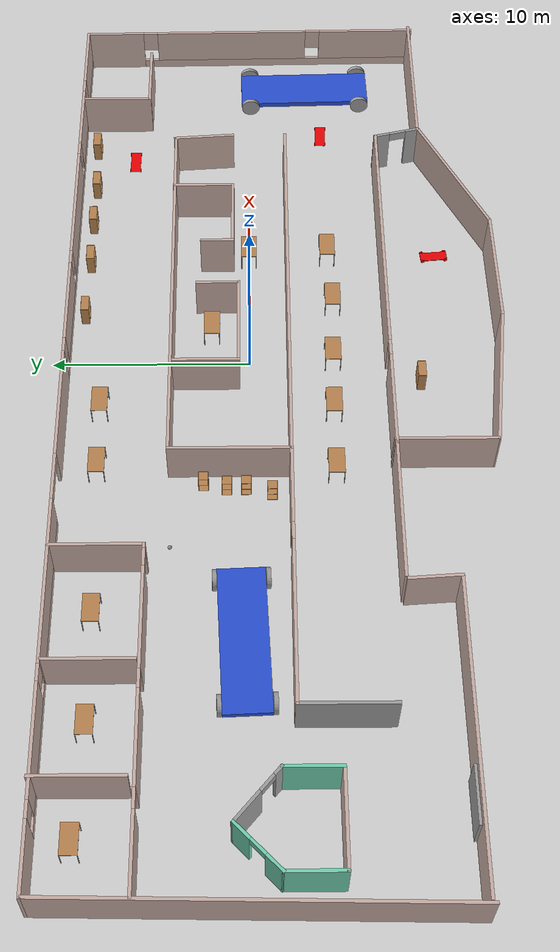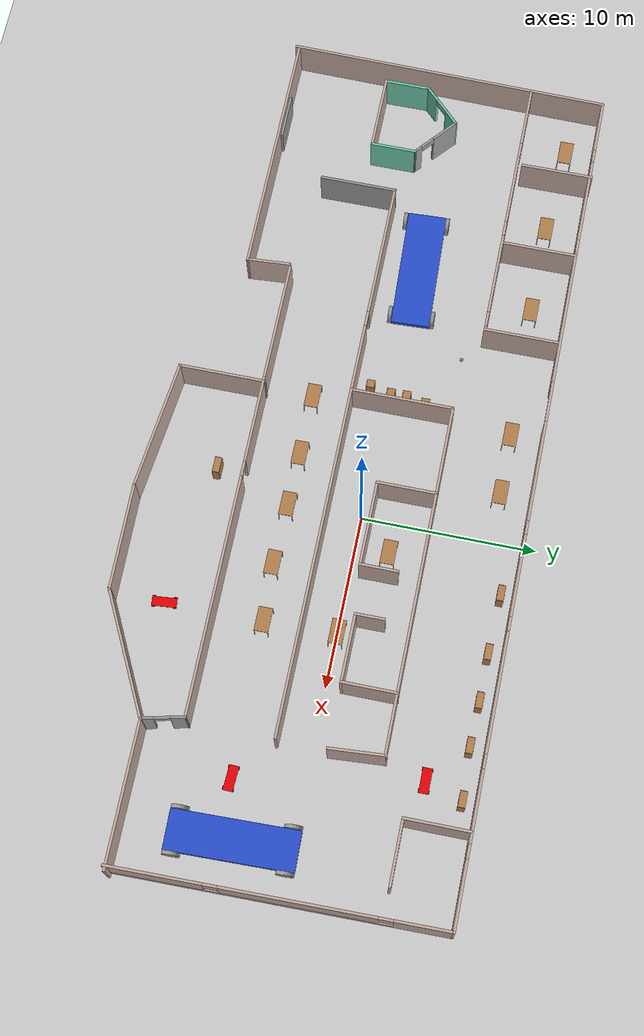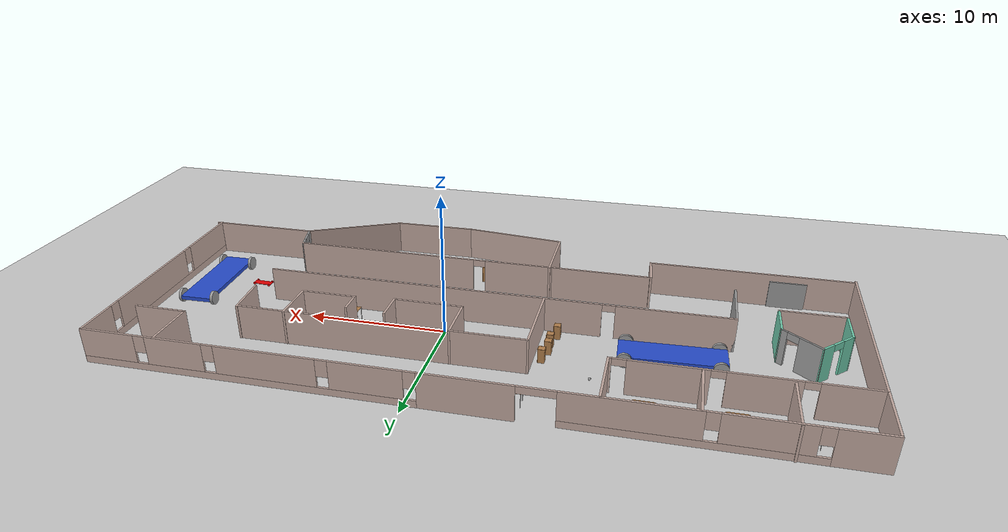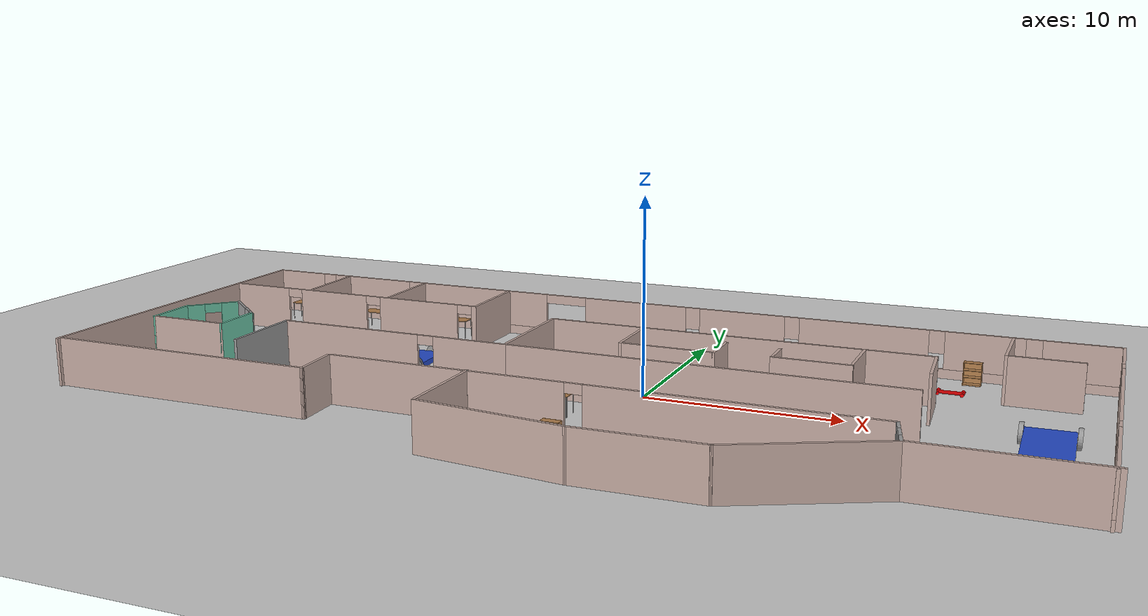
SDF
<sdf version="1.6">
 <world name="default">
  <plugin name="officesim" filename="libofficesim.so"/>
  <light name="sun" type="directional">
   <pose>0 0 10 0 -0 0</pose>
   <diffuse>0.8 0.8 0.8 1</diffuse>
   <specular>0.1 0.1 0.1 1</specular>
   <attenuation>
    <range>1000</range>
    <constant>0.9</constant>
    <linear>0.01</linear>
    <quadratic>0.001</quadratic>
   </attenuation>
   <direction>-0.5 0.5 -1</direction>
  </light>
  <model name="ground_plane">
   <static>1</static>
   <link name="link">
    <collision name="collision">
     <geometry><plane><normal>0 0 1</normal><size>100 100</size></plane></geometry>
     <surface><friction><ode><mu>100</mu><mu2>50</mu2></ode></friction></surface>
    </collision>
    <visual name="visual">
     <cast_shadows>0</cast_shadows>
     <geometry><plane><normal>0 0 1</normal><size>100 100</size></plane></geometry>
     <material>
      <script><uri>file://media/materials/scripts/gazebo.material</uri><name>Gazebo/Grey</name></script>
     </material>
    </visual>
   </link>
  </model>
  <gravity>0 0 -9.8</gravity>
  <magnetic_field>6e-06 2.3e-05 -4.2e-05</magnetic_field>
  <atmosphere type="adiabatic"/>
  <physics name="default_physics" default="0" type="ode">
   <max_step_size>0.001</max_step_size>
   <real_time_factor>1</real_time_factor>
   <real_time_update_rate>1000</real_time_update_rate>
  </physics>
  <scene><ambient>0.4 0.4 0.4 1</ambient><background>0.7 0.7 0.7 1</background><shadows>1</shadows></scene>
  <spherical_coordinates>
   <surface_model>EARTH_WGS84</surface_model>
   <latitude_deg>0</latitude_deg>
   <longitude_deg>0</longitude_deg>
   <elevation>0</elevation>
   <heading_deg>0</heading_deg>
  </spherical_coordinates>
  <model name="officesim">
   <pose>-2.8701 -1.6759 0 0 -0 0</pose>
   <link name="Door_8">
    <collision name="Door_8_Collision">
     <geometry><box><size>2.61208 0.2 2</size></box></geometry>
     <pose>0 0 1 0 -0 0</pose>
    </collision>
    <visual name="Door_8_Visual">
     <pose>0 0 1 0 -0 0</pose>
     <geometry><box><size>2.61208 0.2 2</size></box></geometry>
     <material>
      <script><uri>file://media/materials/scripts/gazebo.material</uri><name>Gazebo/Grey</name></script>
     </material>
    </visual>
    <pose>-20.5074 -7.65643 0 0 -0 0</pose>
   </link>
   <link name="Wall_0">
    <pose>-0.078667 10.8725 0 0 -0 0</pose>
    <visual name="Wall_0_Visual_0">
     <pose>-23.1341 0 1.25 0 -0 0</pose>
     <geometry><box><size>3.23173 0.15 2.5</size></box></geometry>
     <material>
      <script><uri>file://media/materials/scripts/gazebo.material</uri><name>Gazebo/Grey</name></script>
      <ambient>0.760784 0.662745 0.627451 1</ambient>
     </material>
    </visual>
    <collision name="Wall_0_Collision_0">
     <geometry><box><size>3.23173 0.15 2.5</size></box></geometry>
     <pose>-23.1341 0 1.25 0 -0 0</pose>
    </collision>
    <visual name="Wall_0_Visual_1">
     <pose>-0.958275 0 1.25 0 -0 0</pose>
     <geometry><box><size>6.01036 0.15 2.5</size></box></geometry>
     <material>
      <script><uri>file://media/materials/scripts/gazebo.material</uri><name>Gazebo/Grey</name></script>
      <ambient>0.760784 0.662745 0.627451 1</ambient>
     </material>
    </visual>
    <collision name="Wall_0_Collision_1">
     <geometry><box><size>6.01036 0.15 2.5</size></box></geometry>
     <pose>-0.958275 0 1.25 0 -0 0</pose>
    </collision>
    <visual name="Wall_0_Visual_2">
     <pose>-13.96 0 0.25 0 -0 0</pose>
     <geometry><box><size>15.1166 0.15 0.5</size></box></geometry>
     <material>
      <script><uri>file://media/materials/scripts/gazebo.material</uri><name>Gazebo/Grey</name></script>
      <ambient>0.760784 0.662745 0.627451 1</ambient>
     </material>
    </visual>
    <collision name="Wall_0_Collision_2">
     <geometry><box><size>15.1166 0.15 0.5</size></box></geometry>
     <pose>-13.96 0 0.25 0 -0 0</pose>
    </collision>
    <visual name="Wall_0_Visual_3">
     <pose>13.3985 0 0.25 0 -0 0</pose>
     <geometry><box><size>22.7031 0.15 0.5</size></box></geometry>
     <material>
      <script><uri>file://media/materials/scripts/gazebo.material</uri><name>Gazebo/Grey</name></script>
      <ambient>0.760784 0.662745 0.627451 1</ambient>
     </material>
    </visual>
    <collision name="Wall_0_Collision_3">
     <geometry><box><size>22.7031 0.15 0.5</size></box></geometry>
     <pose>13.3985 0 0.25 0 -0 0</pose>
    </collision>
    <visual name="Wall_0_Visual_4">
     <pose>-18.1034 0 1.5 0 -0 0</pose>
     <geometry><box><size>5.22973 0.15 2</size></box></geometry>
     <material>
      <script><uri>file://media/materials/scripts/gazebo.material</uri><name>Gazebo/Grey</name></script>
      <ambient>0.760784 0.662745 0.627451 1</ambient>
     </material>
    </visual>
    <collision name="Wall_0_Collision_4">
     <geometry><box><size>5.22973 0.15 2</size></box></geometry>
     <pose>-18.1034 0 1.5 0 -0 0</pose>
    </collision>
    <visual name="Wall_0_Visual_5">
     <pose>-10.5451 0 1.5 0 -0 0</pose>
     <geometry><box><size>8.28689 0.15 2</size></box></geometry>
     <material>
      <script><uri>file://media/materials/scripts/gazebo.material</uri><name>Gazebo/Grey</name></script>
      <ambient>0.760784 0.662745 0.627451 1</ambient>
     </material>
    </visual>
    <collision name="Wall_0_Collision_5">
     <geometry><box><size>8.28689 0.15 2</size></box></geometry>
     <pose>-10.5451 0 1.5 0 -0 0</pose>
    </collision>
    <visual name="Wall_0_Visual_6">
     <pose>-10.5451 0 1.5 0 -0 0</pose>
     <geometry><box><size>8.28689 0.15 2</size></box></geometry>
     <material>
      <script><uri>file://media/materials/scripts/gazebo.material</uri><name>Gazebo/Grey</name></script>
      <ambient>0.760784 0.662745 0.627451 1</ambient>
     </material>
    </visual>
    <collision name="Wall_0_Collision_6">
     <geometry><box><size>8.28689 0.15 2</size></box></geometry>
     <pose>-10.5451 0 1.5 0 -0 0</pose>
    </collision>
    <visual name="Wall_0_Visual_7">
     <pose>5.24642 0 1.5 0 -0 0</pose>
     <geometry><box><size>4.79904 0.15 2</size></box></geometry>
     <material>
      <script><uri>file://media/materials/scripts/gazebo.material</uri><name>Gazebo/Grey</name></script>
      <ambient>0.760784 0.662745 0.627451 1</ambient>
     </material>
    </visual>
    <collision name="Wall_0_Collision_7">
     <geometry><box><size>4.79904 0.15 2</size></box></geometry>
     <pose>5.24642 0 1.5 0 -0 0</pose>
    </collision>
    <visual name="Wall_0_Visual_8">
     <pose>11.8607 0 1.5 0 -0 0</pose>
     <geometry><box><size>6.82946 0.15 2</size></box></geometry>
     <material>
      <script><uri>file://media/materials/scripts/gazebo.material</uri><name>Gazebo/Grey</name></script>
      <ambient>0.760784 0.662745 0.627451 1</ambient>
     </material>
    </visual>
    <collision name="Wall_0_Collision_8">
     <geometry><box><size>6.82946 0.15 2</size></box></geometry>
     <pose>11.8607 0 1.5 0 -0 0</pose>
    </collision>
    <visual name="Wall_0_Visual_9">
     <pose>18.075 0 1.5 0 -0 0</pose>
     <geometry><box><size>3.99918 0.15 2</size></box></geometry>
     <material>
      <script><uri>file://media/materials/scripts/gazebo.material</uri><name>Gazebo/Grey</name></script>
      <ambient>0.760784 0.662745 0.627451 1</ambient>
     </material>
    </visual>
    <collision name="Wall_0_Collision_9">
     <geometry><box><size>3.99918 0.15 2</size></box></geometry>
     <pose>18.075 0 1.5 0 -0 0</pose>
    </collision>
    <visual name="Wall_0_Visual_10">
     <pose>22.8123 0 1.5 0 -0 0</pose>
     <geometry><box><size>3.87543 0.15 2</size></box></geometry>
     <material>
      <script><uri>file://media/materials/scripts/gazebo.material</uri><name>Gazebo/Grey</name></script>
      <ambient>0.760784 0.662745 0.627451 1</ambient>
     </material>
    </visual>
    <collision name="Wall_0_Collision_10">
     <geometry><box><size>3.87543 0.15 2</size></box></geometry>
     <pose>22.8123 0 1.5 0 -0 0</pose>
    </collision>
    <visual name="Wall_0_Visual_11">
     <pose>-21.1183 0 1.9 0 -0 0</pose>
     <geometry><box><size>0.8 0.15 1.2</size></box></geometry>
     <material>
      <script><uri>file://media/materials/scripts/gazebo.material</uri><name>Gazebo/Grey</name></script>
      <ambient>0.760784 0.662745 0.627451 1</ambient>
     </material>
    </visual>
    <collision name="Wall_0_Collision_11">
     <geometry><box><size>0.8 0.15 1.2</size></box></geometry>
     <pose>-21.1183 0 1.9 0 -0 0</pose>
    </collision>
    <visual name="Wall_0_Visual_12">
     <pose>2.44691 0 1.9 0 -0 0</pose>
     <geometry><box><size>0.8 0.15 1.2</size></box></geometry>
     <material>
      <script><uri>file://media/materials/scripts/gazebo.material</uri><name>Gazebo/Grey</name></script>
      <ambient>0.760784 0.662745 0.627451 1</ambient>
     </material>
    </visual>
    <collision name="Wall_0_Collision_12">
     <geometry><box><size>0.8 0.15 1.2</size></box></geometry>
     <pose>2.44691 0 1.9 0 -0 0</pose>
    </collision>
    <visual name="Wall_0_Visual_13">
     <pose>-15.0885 0 1.9 0 -0 0</pose>
     <geometry><box><size>0.8 0.15 1.2</size></box></geometry>
     <material>
      <script><uri>file://media/materials/scripts/gazebo.material</uri><name>Gazebo/Grey</name></script>
      <ambient>0.760784 0.662745 0.627451 1</ambient>
     </material>
    </visual>
    <collision name="Wall_0_Collision_13">
     <geometry><box><size>0.8 0.15 1.2</size></box></geometry>
     <pose>-15.0885 0 1.9 0 -0 0</pose>
    </collision>
    <visual name="Wall_0_Visual_14">
     <pose>8.04594 0 1.9 0 -0 0</pose>
     <geometry><box><size>0.8 0.15 1.2</size></box></geometry>
     <material>
      <script><uri>file://media/materials/scripts/gazebo.material</uri><name>Gazebo/Grey</name></script>
      <ambient>0.760784 0.662745 0.627451 1</ambient>
     </material>
    </visual>
    <collision name="Wall_0_Collision_14">
     <geometry><box><size>0.8 0.15 1.2</size></box></geometry>
     <pose>8.04594 0 1.9 0 -0 0</pose>
    </collision>
    <visual name="Wall_0_Visual_15">
     <pose>15.6754 0 1.9 0 -0 0</pose>
     <geometry><box><size>0.8 0.15 1.2</size></box></geometry>
     <material>
      <script><uri>file://media/materials/scripts/gazebo.material</uri><name>Gazebo/Grey</name></script>
      <ambient>0.760784 0.662745 0.627451 1</ambient>
     </material>
    </visual>
    <collision name="Wall_0_Collision_15">
     <geometry><box><size>0.8 0.15 1.2</size></box></geometry>
     <pose>15.6754 0 1.9 0 -0 0</pose>
    </collision>
    <visual name="Wall_0_Visual_16">
     <pose>20.4746 0 1.9 0 -0 0</pose>
     <geometry><box><size>0.8 0.15 1.2</size></box></geometry>
     <material>
      <script><uri>file://media/materials/scripts/gazebo.material</uri><name>Gazebo/Grey</name></script>
      <ambient>0.760784 0.662745 0.627451 1</ambient>
     </material>
    </visual>
    <collision name="Wall_0_Collision_16">
     <geometry><box><size>0.8 0.15 1.2</size></box></geometry>
     <pose>20.4746 0 1.9 0 -0 0</pose>
    </collision>
    <visual name="Wall_0_Visual_17">
     <pose>-5.18255 0 2.25 0 -0 0</pose>
     <geometry><box><size>2.4382 0.15 0.5</size></box></geometry>
     <material>
      <script><uri>file://media/materials/scripts/gazebo.material</uri><name>Gazebo/Grey</name></script>
      <ambient>0.760784 0.662745 0.627451 1</ambient>
     </material>
    </visual>
    <collision name="Wall_0_Collision_17">
     <geometry><box><size>2.4382 0.15 0.5</size></box></geometry>
     <pose>-5.18255 0 2.25 0 -0 0</pose>
    </collision>
    <visual name="Wall_0_Visual_18">
     <pose>-5.18255 0 2.25 0 -0 0</pose>
     <geometry><box><size>2.4382 0.15 0.5</size></box></geometry>
     <material>
      <script><uri>file://media/materials/scripts/gazebo.material</uri><name>Gazebo/Grey</name></script>
      <ambient>0.760784 0.662745 0.627451 1</ambient>
     </material>
    </visual>
    <collision name="Wall_0_Collision_18">
     <geometry><box><size>2.4382 0.15 0.5</size></box></geometry>
     <pose>-5.18255 0 2.25 0 -0 0</pose>
    </collision>
   </link>
   <link name="Wall_1">
    <pose>24.7194 1.60331 0 0 0 -1.55743</pose>
    <visual name="Wall_1_Visual_0">
     <pose>-7.70288 0 1.25 0 -0 0</pose>
     <geometry><box><size>3.16131 0.15 2.5</size></box></geometry>
     <material>
      <script><uri>file://media/materials/scripts/gazebo.material</uri><name>Gazebo/Grey</name></script>
      <ambient>0.760784 0.662745 0.627451 1</ambient>
     </material>
    </visual>
    <collision name="Wall_1_Collision_0">
     <geometry><box><size>3.16131 0.15 2.5</size></box></geometry>
     <pose>-7.70288 0 1.25 0 -0 0</pose>
    </collision>
    <visual name="Wall_1_Visual_1">
     <pose>1.58065 0 0.25 0 -0 0</pose>
     <geometry><box><size>15.4058 0.15 0.5</size></box></geometry>
     <material>
      <script><uri>file://media/materials/scripts/gazebo.material</uri><name>Gazebo/Grey</name></script>
      <ambient>0.760784 0.662745 0.627451 1</ambient>
     </material>
    </visual>
    <collision name="Wall_1_Collision_1">
     <geometry><box><size>15.4058 0.15 0.5</size></box></geometry>
     <pose>1.58065 0 0.25 0 -0 0</pose>
    </collision>
    <visual name="Wall_1_Visual_2">
     <pose>-1.07769 0 1.5 0 -0 0</pose>
     <geometry><box><size>8.48906 0.15 2</size></box></geometry>
     <material>
      <script><uri>file://media/materials/scripts/gazebo.material</uri><name>Gazebo/Grey</name></script>
      <ambient>0.760784 0.662745 0.627451 1</ambient>
     </material>
    </visual>
    <collision name="Wall_1_Collision_2">
     <geometry><box><size>8.48906 0.15 2</size></box></geometry>
     <pose>-1.07769 0 1.5 0 -0 0</pose>
    </collision>
    <visual name="Wall_1_Visual_3">
     <pose>6.62518 0 1.5 0 -0 0</pose>
     <geometry><box><size>5.31669 0.15 2</size></box></geometry>
     <material>
      <script><uri>file://media/materials/scripts/gazebo.material</uri><name>Gazebo/Grey</name></script>
      <ambient>0.760784 0.662745 0.627451 1</ambient>
     </material>
    </visual>
    <collision name="Wall_1_Collision_3">
     <geometry><box><size>5.31669 0.15 2</size></box></geometry>
     <pose>6.62518 0 1.5 0 -0 0</pose>
    </collision>
    <visual name="Wall_1_Visual_4">
     <pose>-5.72222 0 1.9 0 -0 0</pose>
     <geometry><box><size>0.8 0.15 1.2</size></box></geometry>
     <material>
      <script><uri>file://media/materials/scripts/gazebo.material</uri><name>Gazebo/Grey</name></script>
      <ambient>0.760784 0.662745 0.627451 1</ambient>
     </material>
    </visual>
    <collision name="Wall_1_Collision_4">
     <geometry><box><size>0.8 0.15 1.2</size></box></geometry>
     <pose>-5.72222 0 1.9 0 -0 0</pose>
    </collision>
    <visual name="Wall_1_Visual_5">
     <pose>3.56684 0 1.9 0 -0 0</pose>
     <geometry><box><size>0.8 0.15 1.2</size></box></geometry>
     <material>
      <script><uri>file://media/materials/scripts/gazebo.material</uri><name>Gazebo/Grey</name></script>
      <ambient>0.760784 0.662745 0.627451 1</ambient>
     </material>
    </visual>
    <collision name="Wall_1_Collision_5">
     <geometry><box><size>0.8 0.15 1.2</size></box></geometry>
     <pose>3.56684 0 1.9 0 -0 0</pose>
    </collision>
   </link>
   <link name="Wall_14">
    <collision name="Wall_14_Collision">
     <geometry><box><size>6.27117 0.15 2.5</size></box></geometry>
     <pose>0 0 1.25 0 -0 0</pose>
    </collision>
    <visual name="Wall_14_Visual">
     <pose>0 0 1.25 0 -0 0</pose>
     <geometry><box><size>6.27117 0.15 2.5</size></box></geometry>
     <material>
      <script><uri>file://media/materials/scripts/gazebo.material</uri><name>Gazebo/Grey</name></script>
      <ambient>0.760784 0.662745 0.627451 1</ambient>
     </material>
    </visual>
    <pose>7.25272 -10.9104 0 0 0 -3.12722</pose>
   </link>
   <link name="Wall_15">
    <collision name="Wall_15_Collision">
     <geometry><box><size>7.67434 0.15 2.5</size></box></geometry>
     <pose>0 0 1.25 0 -0 0</pose>
    </collision>
    <visual name="Wall_15_Visual">
     <pose>0 0 1.25 0 -0 0</pose>
     <geometry><box><size>7.67434 0.15 2.5</size></box></geometry>
     <material>
      <script><uri>file://media/materials/scripts/gazebo.material</uri><name>Gazebo/Grey</name></script>
      <ambient>0.760784 0.662745 0.627451 1</ambient>
     </material>
    </visual>
    <pose>0.454703 -10.5264 0 0 -0 3.02758</pose>
   </link>
   <link name="Wall_16">
    <collision name="Wall_16_Collision">
     <geometry><box><size>5 0.15 2.5</size></box></geometry>
     <pose>0 0 1.25 0 -0 0</pose>
    </collision>
    <visual name="Wall_16_Visual">
     <pose>0 0 1.25 0 -0 0</pose>
     <geometry><box><size>5 0.15 2.5</size></box></geometry>
     <material>
      <script><uri>file://media/materials/scripts/gazebo.material</uri><name>Gazebo/Grey</name></script>
      <ambient>0.760784 0.662745 0.627451 1</ambient>
     </material>
    </visual>
    <pose>-3.28304 -7.61986 0 0 -0 1.5708</pose>
   </link>
   <link name="Wall_17">
    <collision name="Wall_17_Collision">
     <geometry><box><size>0.15 0.15 2.5</size></box></geometry>
     <pose>0 0 1.25 0 -0 0</pose>
    </collision>
    <visual name="Wall_17_Visual">
     <pose>0 0 1.25 0 -0 0</pose>
     <geometry><box><size>0.15 0.15 2.5</size></box></geometry>
     <material>
      <script><uri>file://media/materials/scripts/gazebo.material</uri><name>Gazebo/Grey</name></script>
      <ambient>1 1 1 1</ambient>
     </material>
    </visual>
    <pose>-3.28304 -5.24836 0 0 -0 0</pose>
   </link>
   <link name="Wall_19">
    <collision name="Wall_19_Collision">
     <geometry><box><size>7.63209 0.15 2.5</size></box></geometry>
     <pose>0 0 1.25 0 -0 0</pose>
    </collision>
    <visual name="Wall_19_Visual">
     <pose>0 0 1.25 0 -0 0</pose>
     <geometry><box><size>7.63209 0.15 2.5</size></box></geometry>
     <material>
      <script><uri>file://media/materials/scripts/gazebo.material</uri><name>Gazebo/Grey</name></script>
      <ambient>0.760784 0.662745 0.627451 1</ambient>
     </material>
    </visual>
    <pose>13.6569 -9.18898 0 0 -0 0.464953</pose>
   </link>
   <link name="Wall_20">
    <collision name="Wall_20_Collision">
     <geometry><box><size>8.2824 0.15 2.5</size></box></geometry>
     <pose>0 0 1.25 0 -0 0</pose>
    </collision>
    <visual name="Wall_20_Visual">
     <pose>0 0 1.25 0 -0 0</pose>
     <geometry><box><size>8.2824 0.15 2.5</size></box></geometry>
     <material>
      <script><uri>file://media/materials/scripts/gazebo.material</uri><name>Gazebo/Grey</name></script>
      <ambient>0.760784 0.662745 0.627451 1</ambient>
     </material>
    </visual>
    <pose>21.0135 -7.50165 0 0 -0 0.002439</pose>
   </link>
   <link name="Wall_24">
    <collision name="Wall_24_Collision">
     <geometry><box><size>4.5 0.15 2.5</size></box></geometry>
     <pose>0 0 1.25 0 -0 0</pose>
    </collision>
    <visual name="Wall_24_Visual">
     <pose>0 0 1.25 0 -0 0</pose>
     <geometry><box><size>4.5 0.15 2.5</size></box></geometry>
     <material>
      <script><uri>file://media/materials/scripts/gazebo.material</uri><name>Gazebo/Grey</name></script>
      <ambient>1 1 1 1</ambient>
     </material>
    </visual>
    <pose>-16.6523 -2.4316 0 0 -0 1.5708</pose>
   </link>
   <link name="Wall_25">
    <pose>-10.2093 -0.256602 0 0 -0 0</pose>
    <visual name="Wall_25_Visual_0">
     <pose>-2.49362 0 1.25 0 -0 0</pose>
     <geometry><box><size>8.04875 0.15 2.5</size></box></geometry>
     <material>
      <script><uri>file://media/materials/scripts/gazebo.material</uri><name>Gazebo/Grey</name></script>
      <ambient>0.760784 0.662745 0.627451 1</ambient>
     </material>
    </visual>
    <collision name="Wall_25_Collision_0">
     <geometry><box><size>8.04875 0.15 2.5</size></box></geometry>
     <pose>-2.49362 0 1.25 0 -0 0</pose>
    </collision>
    <visual name="Wall_25_Visual_1">
     <pose>4.47437 0 1.25 0 -0 0</pose>
     <geometry><box><size>4.08725 0.15 2.5</size></box></geometry>
     <material>
      <script><uri>file://media/materials/scripts/gazebo.material</uri><name>Gazebo/Grey</name></script>
      <ambient>0.760784 0.662745 0.627451 1</ambient>
     </material>
    </visual>
    <collision name="Wall_25_Collision_1">
     <geometry><box><size>4.08725 0.15 2.5</size></box></geometry>
     <pose>4.47437 0 1.25 0 -0 0</pose>
    </collision>
    <visual name="Wall_25_Visual_2">
     <pose>1.98075 0 2.25 0 -0 0</pose>
     <geometry><box><size>0.9 0.15 0.5</size></box></geometry>
     <material>
      <script><uri>file://media/materials/scripts/gazebo.material</uri><name>Gazebo/Grey</name></script>
      <ambient>0.760784 0.662745 0.627451 1</ambient>
     </material>
    </visual>
    <collision name="Wall_25_Collision_2">
     <geometry><box><size>0.9 0.15 0.5</size></box></geometry>
     <pose>1.98075 0 2.25 0 -0 0</pose>
    </collision>
   </link>
   <link name="Wall_26">
    <collision name="Wall_26_Collision">
     <geometry><box><size>6 0.15 2.5</size></box></geometry>
     <pose>0 0 1.25 0 -0 0</pose>
    </collision>
    <visual name="Wall_26_Visual">
     <pose>0 0 1.25 0 -0 0</pose>
     <geometry><box><size>6 0.15 2.5</size></box></geometry>
     <material>
      <script><uri>file://media/materials/scripts/gazebo.material</uri><name>Gazebo/Grey</name></script>
      <ambient>0.760784 0.662745 0.627451 1</ambient>
     </material>
    </visual>
    <pose>-3.76628 2.6684 0 0 -0 1.5708</pose>
   </link>
   <link name="Wall_27">
    <collision name="Wall_27_Collision">
     <geometry><box><size>20.1971 0.15 2.5</size></box></geometry>
     <pose>0 0 1.25 0 -0 0</pose>
    </collision>
    <visual name="Wall_27_Visual">
     <pose>0 0 1.25 0 -0 0</pose>
     <geometry><box><size>20.1971 0.15 2.5</size></box></geometry>
     <material>
      <script><uri>file://media/materials/scripts/gazebo.material</uri><name>Gazebo/Grey</name></script>
      <ambient>0.760784 0.662745 0.627451 1</ambient>
     </material>
    </visual>
    <pose>6.31047 5.62015 0 0 -0 0.002669</pose>
   </link>
   <link name="Wall_28">
    <collision name="Wall_28_Collision">
     <geometry><box><size>3.25738 0.15 2.5</size></box></geometry>
     <pose>0 0 1.25 0 -0 0</pose>
    </collision>
    <visual name="Wall_28_Visual">
     <pose>0 0 1.25 0 -0 0</pose>
     <geometry><box><size>3.25738 0.15 2.5</size></box></geometry>
     <material>
      <script><uri>file://media/materials/scripts/gazebo.material</uri><name>Gazebo/Grey</name></script>
      <ambient>0.760784 0.662745 0.627451 1</ambient>
     </material>
    </visual>
    <pose>16.4407 4.1504 0 0 0 -1.50187</pose>
   </link>
   <link name="Wall_3">
    <collision name="Wall_3_Collision">
     <geometry><box><size>18.8892 0.15 2.5</size></box></geometry>
     <pose>0 0 1.25 0 -0 0</pose>
    </collision>
    <visual name="Wall_3_Visual">
     <pose>0 0 1.25 0 -0 0</pose>
     <geometry><box><size>18.8892 0.15 2.5</size></box></geometry>
     <material>
      <script><uri>file://media/materials/scripts/gazebo.material</uri><name>Gazebo/Grey</name></script>
      <ambient>0.760784 0.662745 0.627451 1</ambient>
     </material>
    </visual>
    <pose>-24.9161 1.4428 0 0 -0 1.55346</pose>
   </link>
   <link name="Wall_31">
    <collision name="Wall_31_Collision">
     <geometry><box><size>2.57633 0.15 2.5</size></box></geometry>
     <pose>0 0 1.25 0 -0 0</pose>
    </collision>
    <visual name="Wall_31_Visual">
     <pose>0 0 1.25 0 -0 0</pose>
     <geometry><box><size>2.57633 0.15 2.5</size></box></geometry>
     <material>
      <script><uri>file://media/materials/scripts/gazebo.material</uri><name>Gazebo/Grey</name></script>
      <ambient>0.760784 0.662745 0.627451 1</ambient>
     </material>
    </visual>
    <pose>-10.6483 -6.5544 0 0 -0 1.637</pose>
   </link>
   <link name="Wall_34">
    <collision name="Wall_34_Collision">
     <geometry><box><size>7.25 0.15 2.5</size></box></geometry>
     <pose>0 0 1.25 0 -0 0</pose>
    </collision>
    <visual name="Wall_34_Visual">
     <pose>0 0 1.25 0 -0 0</pose>
     <geometry><box><size>7.25 0.15 2.5</size></box></geometry>
     <material>
      <script><uri>file://media/materials/scripts/gazebo.material</uri><name>Gazebo/Grey</name></script>
      <ambient>0.760784 0.662745 0.627451 1</ambient>
     </material>
    </visual>
    <pose>-7.01681 -5.24881 0 0 -0 3.14159</pose>
   </link>
   <link name="Wall_36">
    <pose>6.47619 -5.22206 0 0 -0 0.00269</pose>
    <visual name="Wall_36_Visual_0">
     <pose>-7.42655 0 1.25 0 -0 0</pose>
     <geometry><box><size>5.18297 0.15 2.5</size></box></geometry>
     <material>
      <script><uri>file://media/materials/scripts/gazebo.material</uri><name>Gazebo/Grey</name></script>
      <ambient>0.760784 0.662745 0.627451 1</ambient>
     </material>
    </visual>
    <collision name="Wall_36_Collision_0">
     <geometry><box><size>5.18297 0.15 2.5</size></box></geometry>
     <pose>-7.42655 0 1.25 0 -0 0</pose>
    </collision>
    <visual name="Wall_36_Visual_1">
     <pose>3.04148 0 1.25 0 -0 0</pose>
     <geometry><box><size>13.9531 0.15 2.5</size></box></geometry>
     <material>
      <script><uri>file://media/materials/scripts/gazebo.material</uri><name>Gazebo/Grey</name></script>
      <ambient>0.760784 0.662745 0.627451 1</ambient>
     </material>
    </visual>
    <collision name="Wall_36_Collision_1">
     <geometry><box><size>13.9531 0.15 2.5</size></box></geometry>
     <pose>3.04148 0 1.25 0 -0 0</pose>
    </collision>
    <visual name="Wall_36_Visual_2">
     <pose>-4.38506 0 2.25 0 -0 0</pose>
     <geometry><box><size>0.9 0.15 0.5</size></box></geometry>
     <material>
      <script><uri>file://media/materials/scripts/gazebo.material</uri><name>Gazebo/Grey</name></script>
      <ambient>0.760784 0.662745 0.627451 1</ambient>
     </material>
    </visual>
    <collision name="Wall_36_Collision_2">
     <geometry><box><size>0.9 0.15 0.5</size></box></geometry>
     <pose>-4.38506 0 2.25 0 -0 0</pose>
    </collision>
   </link>
   <link name="Wall_39">
    <pose>-16.8358 6.52173 0 0 -0 0</pose>
    <visual name="Wall_39_Visual_0">
     <pose>-6.18116 0 1.25 0 -0 0</pose>
     <geometry><box><size>3.63769 0.15 2.5</size></box></geometry>
     <material>
      <script><uri>file://media/materials/scripts/gazebo.material</uri><name>Gazebo/Grey</name></script>
      <ambient>0.760784 0.662745 0.627451 1</ambient>
     </material>
    </visual>
    <collision name="Wall_39_Collision_0">
     <geometry><box><size>3.63769 0.15 2.5</size></box></geometry>
     <pose>-6.18116 0 1.25 0 -0 0</pose>
    </collision>
    <visual name="Wall_39_Visual_1">
     <pose>-1.26394 0 1.25 0 -0 0</pose>
     <geometry><box><size>4.39675 0.15 2.5</size></box></geometry>
     <material>
      <script><uri>file://media/materials/scripts/gazebo.material</uri><name>Gazebo/Grey</name></script>
      <ambient>0.760784 0.662745 0.627451 1</ambient>
     </material>
    </visual>
    <collision name="Wall_39_Collision_1">
     <geometry><box><size>4.39675 0.15 2.5</size></box></geometry>
     <pose>-1.26394 0 1.25 0 -0 0</pose>
    </collision>
    <visual name="Wall_39_Visual_2">
     <pose>4.32707 0 1.25 0 -0 0</pose>
     <geometry><box><size>4.98527 0.15 2.5</size></box></geometry>
     <material>
      <script><uri>file://media/materials/scripts/gazebo.material</uri><name>Gazebo/Grey</name></script>
      <ambient>0.760784 0.662745 0.627451 1</ambient>
     </material>
    </visual>
    <collision name="Wall_39_Collision_2">
     <geometry><box><size>4.98527 0.15 2.5</size></box></geometry>
     <pose>4.32707 0 1.25 0 -0 0</pose>
    </collision>
    <visual name="Wall_39_Visual_3">
     <pose>7.85985 0 1.25 0 -0 0</pose>
     <geometry><box><size>0.280289 0.15 2.5</size></box></geometry>
     <material>
      <script><uri>file://media/materials/scripts/gazebo.material</uri><name>Gazebo/Grey</name></script>
      <ambient>0.760784 0.662745 0.627451 1</ambient>
     </material>
    </visual>
    <collision name="Wall_39_Collision_3">
     <geometry><box><size>0.280289 0.15 2.5</size></box></geometry>
     <pose>7.85985 0 1.25 0 -0 0</pose>
    </collision>
    <visual name="Wall_39_Visual_4">
     <pose>-3.91231 0 2.25 0 -0 0</pose>
     <geometry><box><size>0.9 0.15 0.5</size></box></geometry>
     <material>
      <script><uri>file://media/materials/scripts/gazebo.material</uri><name>Gazebo/Grey</name></script>
      <ambient>0.760784 0.662745 0.627451 1</ambient>
     </material>
    </visual>
    <collision name="Wall_39_Collision_4">
     <geometry><box><size>0.9 0.15 0.5</size></box></geometry>
     <pose>-3.91231 0 2.25 0 -0 0</pose>
    </collision>
    <visual name="Wall_39_Visual_5">
     <pose>1.38444 0 2.25 0 -0 0</pose>
     <geometry><box><size>0.9 0.15 0.5</size></box></geometry>
     <material>
      <script><uri>file://media/materials/scripts/gazebo.material</uri><name>Gazebo/Grey</name></script>
      <ambient>0.760784 0.662745 0.627451 1</ambient>
     </material>
    </visual>
    <collision name="Wall_39_Collision_5">
     <geometry><box><size>0.9 0.15 0.5</size></box></geometry>
     <pose>1.38444 0 2.25 0 -0 0</pose>
    </collision>
    <visual name="Wall_39_Visual_6">
     <pose>7.26971 0 2.25 0 -0 0</pose>
     <geometry><box><size>0.9 0.15 0.5</size></box></geometry>
     <material>
      <script><uri>file://media/materials/scripts/gazebo.material</uri><name>Gazebo/Grey</name></script>
      <ambient>0.760784 0.662745 0.627451 1</ambient>
     </material>
    </visual>
    <collision name="Wall_39_Collision_6">
     <geometry><box><size>0.9 0.15 0.5</size></box></geometry>
     <pose>7.26971 0 2.25 0 -0 0</pose>
    </collision>
   </link>
   <link name="Wall_40">
    <collision name="Wall_40_Collision">
     <geometry><box><size>4.5 0.15 2.5</size></box></geometry>
     <pose>0 0 1.25 0 -0 0</pose>
    </collision>
    <visual name="Wall_40_Visual">
     <pose>0 0 1.25 0 -0 0</pose>
     <geometry><box><size>4.5 0.15 2.5</size></box></geometry>
     <material>
      <script><uri>file://media/materials/scripts/gazebo.material</uri><name>Gazebo/Grey</name></script>
      <ambient>0.760784 0.662745 0.627451 1</ambient>
     </material>
    </visual>
    <pose>-8.9108 8.69674 0 0 -0 1.5708</pose>
   </link>
   <link name="Wall_42">
    <collision name="Wall_42_Collision">
     <geometry><box><size>4.25 0.15 2.5</size></box></geometry>
     <pose>0 0 1.25 0 -0 0</pose>
    </collision>
    <visual name="Wall_42_Visual">
     <pose>0 0 1.25 0 -0 0</pose>
     <geometry><box><size>4.25 0.15 2.5</size></box></geometry>
     <material>
      <script><uri>file://media/materials/scripts/gazebo.material</uri><name>Gazebo/Grey</name></script>
      <ambient>0.760784 0.662745 0.627451 1</ambient>
     </material>
    </visual>
    <pose>-14.5418 8.75193 0 0 0 -1.5708</pose>
   </link>
   <link name="Wall_44">
    <collision name="Wall_44_Collision">
     <geometry><box><size>4.25 0.15 2.5</size></box></geometry>
     <pose>0 0 1.25 0 -0 0</pose>
    </collision>
    <visual name="Wall_44_Visual">
     <pose>0 0 1.25 0 -0 0</pose>
     <geometry><box><size>4.25 0.15 2.5</size></box></geometry>
     <material>
      <script><uri>file://media/materials/scripts/gazebo.material</uri><name>Gazebo/Grey</name></script>
      <ambient>0.760784 0.662745 0.627451 1</ambient>
     </material>
    </visual>
    <pose>-19.7851 8.91244 0 0 0 -1.5708</pose>
   </link>
   <link name="Wall_46">
    <collision name="Wall_46_Collision">
     <geometry><box><size>20.464 0.15 2.5</size></box></geometry>
     <pose>0 0 1.25 0 -0 0</pose>
    </collision>
    <visual name="Wall_46_Visual">
     <pose>0 0 1.25 0 -0 0</pose>
     <geometry><box><size>20.464 0.15 2.5</size></box></geometry>
     <material>
      <script><uri>file://media/materials/scripts/gazebo.material</uri><name>Gazebo/Grey</name></script>
      <ambient>0.760784 0.662745 0.627451 1</ambient>
     </material>
    </visual>
    <pose>6.39072 -0.256602 0 0 -0 0</pose>
   </link>
   <link name="Wall_48">
    <collision name="Wall_48_Collision">
     <geometry><box><size>3.5 0.15 2.5</size></box></geometry>
     <pose>0 0 1.25 0 -0 0</pose>
    </collision>
    <visual name="Wall_48_Visual">
     <pose>0 0 1.25 0 -0 0</pose>
     <geometry><box><size>3.5 0.15 2.5</size></box></geometry>
     <material>
      <script><uri>file://media/materials/scripts/gazebo.material</uri><name>Gazebo/Grey</name></script>
      <ambient>0.760784 0.662745 0.627451 1</ambient>
     </material>
    </visual>
    <pose>1.40192 3.93719 0 0 0 -1.5708</pose>
   </link>
   <link name="Wall_49">
    <collision name="Wall_49_Collision">
     <geometry><box><size>5 0.15 2.5</size></box></geometry>
     <pose>0 0 1.25 0 -0 0</pose>
    </collision>
    <visual name="Wall_49_Visual">
     <pose>0 0 1.25 0 -0 0</pose>
     <geometry><box><size>5 0.15 2.5</size></box></geometry>
     <material>
      <script><uri>file://media/materials/scripts/gazebo.material</uri><name>Gazebo/Grey</name></script>
      <ambient>0.760784 0.662745 0.627451 1</ambient>
     </material>
    </visual>
    <pose>3.82692 2.26219 0 0 -0 0</pose>
   </link>
   <link name="Wall_50">
    <collision name="Wall_50_Collision">
     <geometry><box><size>2.25 0.15 2.5</size></box></geometry>
     <pose>0 0 1.25 0 -0 0</pose>
    </collision>
    <visual name="Wall_50_Visual">
     <pose>0 0 1.25 0 -0 0</pose>
     <geometry><box><size>2.25 0.15 2.5</size></box></geometry>
     <material>
      <script><uri>file://media/materials/scripts/gazebo.material</uri><name>Gazebo/Grey</name></script>
      <ambient>0.760784 0.662745 0.627451 1</ambient>
     </material>
    </visual>
    <pose>6.25192 3.31219 0 0 -0 1.5708</pose>
   </link>
   <link name="Wall_52">
    <collision name="Wall_52_Collision">
     <geometry><box><size>3.25 0.15 2.5</size></box></geometry>
     <pose>0 0 1.25 0 -0 0</pose>
    </collision>
    <visual name="Wall_52_Visual">
     <pose>0 0 1.25 0 -0 0</pose>
     <geometry><box><size>3.25 0.15 2.5</size></box></geometry>
     <material>
      <script><uri>file://media/materials/scripts/gazebo.material</uri><name>Gazebo/Grey</name></script>
      <ambient>0.760784 0.662745 0.627451 1</ambient>
     </material>
    </visual>
    <pose>12.905 4.11569 0 0 0 -1.5708</pose>
   </link>
   <link name="Wall_53">
    <collision name="Wall_53_Collision">
     <geometry><box><size>4 0.15 2.5</size></box></geometry>
     <pose>0 0 1.25 0 -0 0</pose>
    </collision>
    <visual name="Wall_53_Visual">
     <pose>0 0 1.25 0 -0 0</pose>
     <geometry><box><size>4 0.15 2.5</size></box></geometry>
     <material>
      <script><uri>file://media/materials/scripts/gazebo.material</uri><name>Gazebo/Grey</name></script>
      <ambient>0.760784 0.662745 0.627451 1</ambient>
     </material>
    </visual>
    <pose>10.98 2.56569 0 0 -0 3.14159</pose>
   </link>
   <link name="Wall_54">
    <collision name="Wall_54_Collision">
     <geometry><box><size>1.75 0.15 2.5</size></box></geometry>
     <pose>0 0 1.25 0 -0 0</pose>
    </collision>
    <visual name="Wall_54_Visual">
     <pose>0 0 1.25 0 -0 0</pose>
     <geometry><box><size>1.75 0.15 2.5</size></box></geometry>
     <material>
      <script><uri>file://media/materials/scripts/gazebo.material</uri><name>Gazebo/Grey</name></script>
      <ambient>0.760784 0.662745 0.627451 1</ambient>
     </material>
    </visual>
    <pose>9.05496 3.3657 0 0 -0 1.5708</pose>
   </link>
   <link name="Wall_56">
    <collision name="Wall_56_Collision">
     <geometry><box><size>3.75 0.15 2.5</size></box></geometry>
     <pose>0 0 1.25 0 -0 0</pose>
    </collision>
    <visual name="Wall_56_Visual">
     <pose>0 0 1.25 0 -0 0</pose>
     <geometry><box><size>3.75 0.15 2.5</size></box></geometry>
     <material>
      <script><uri>file://media/materials/scripts/gazebo.material</uri><name>Gazebo/Grey</name></script>
      <ambient>0.760784 0.662745 0.627451 1</ambient>
     </material>
    </visual>
    <pose>19.3788 9.00193 0 0 0 -1.5708</pose>
   </link>
   <link name="Wall_57">
    <collision name="Wall_57_Collision">
     <geometry><box><size>3.75 0.15 2.5</size></box></geometry>
     <pose>0 0 1.25 0 -0 0</pose>
    </collision>
    <visual name="Wall_57_Visual">
     <pose>0 0 1.25 0 -0 0</pose>
     <geometry><box><size>3.75 0.15 2.5</size></box></geometry>
     <material>
      <script><uri>file://media/materials/scripts/gazebo.material</uri><name>Gazebo/Grey</name></script>
      <ambient>0.760784 0.662745 0.627451 1</ambient>
     </material>
    </visual>
    <pose>21.1788 7.20194 0 0 -0 0</pose>
   </link>
   <link name="Wall_59">
    <pose>-22.7723 1.44792 0 0 0 -2.35619</pose>
    <visual name="Wall_59_Visual_0">
     <pose>-0.968692 0 1.25 0 -0 0</pose>
     <geometry><box><size>1.06262 0.15 2.5</size></box></geometry>
     <material>
      <script><uri>file://media/materials/scripts/gazebo.material</uri><name>Gazebo/Grey</name></script>
      <ambient>0.435294 0.796078 0.67451 1</ambient>
     </material>
    </visual>
    <collision name="Wall_59_Collision_0">
     <geometry><box><size>1.06262 0.15 2.5</size></box></geometry>
     <pose>-0.968692 0 1.25 0 -0 0</pose>
    </collision>
    <visual name="Wall_59_Visual_1">
     <pose>0.981308 0 1.25 0 -0 0</pose>
     <geometry><box><size>1.03738 0.15 2.5</size></box></geometry>
     <material>
      <script><uri>file://media/materials/scripts/gazebo.material</uri><name>Gazebo/Grey</name></script>
      <ambient>0.435294 0.796078 0.67451 1</ambient>
     </material>
    </visual>
    <collision name="Wall_59_Collision_1">
     <geometry><box><size>1.03738 0.15 2.5</size></box></geometry>
     <pose>0.981308 0 1.25 0 -0 0</pose>
    </collision>
    <visual name="Wall_59_Visual_2">
     <pose>0.012616 0 2.25 0 -0 0</pose>
     <geometry><box><size>0.9 0.15 0.5</size></box></geometry>
     <material>
      <script><uri>file://media/materials/scripts/gazebo.material</uri><name>Gazebo/Grey</name></script>
      <ambient>0.435294 0.796078 0.67451 1</ambient>
     </material>
    </visual>
    <collision name="Wall_59_Collision_2">
     <geometry><box><size>0.9 0.15 0.5</size></box></geometry>
     <pose>0.012616 0 2.25 0 -0 0</pose>
    </collision>
   </link>
   <link name="Wall_60">
    <collision name="Wall_60_Collision">
     <geometry><box><size>2.75 0.15 2.5</size></box></geometry>
     <pose>0 0 1.25 0 -0 0</pose>
    </collision>
    <visual name="Wall_60_Visual">
     <pose>0 0 1.25 0 -0 0</pose>
     <geometry><box><size>2.75 0.15 2.5</size></box></geometry>
     <material>
      <script><uri>file://media/materials/scripts/gazebo.material</uri><name>Gazebo/Grey</name></script>
      <ambient>0.435294 0.796078 0.67451 1</ambient>
     </material>
    </visual>
    <pose>-23.7799 -0.859709 0 0 0 -1.5708</pose>
   </link>
   <link name="Wall_61">
    <collision name="Wall_61_Collision">
     <geometry><box><size>4.5 0.15 2.5</size></box></geometry>
     <pose>0 0 1.25 0 -0 0</pose>
    </collision>
    <visual name="Wall_61_Visual">
     <pose>0 0 1.25 0 -0 0</pose>
     <geometry><box><size>4.5 0.15 2.5</size></box></geometry>
     <material>
      <script><uri>file://media/materials/scripts/gazebo.material</uri><name>Gazebo/Grey</name></script>
      <ambient>0.760784 0.662745 0.627451 1</ambient>
     </material>
    </visual>
    <pose>-21.6049 -2.15971 0 0 -0 0</pose>
   </link>
   <link name="Wall_62">
    <collision name="Wall_62_Collision">
     <geometry><box><size>2.75 0.15 2.5</size></box></geometry>
     <pose>0 0 1.25 0 -0 0</pose>
    </collision>
    <visual name="Wall_62_Visual">
     <pose>0 0 1.25 0 -0 0</pose>
     <geometry><box><size>2.75 0.15 2.5</size></box></geometry>
     <material>
      <script><uri>file://media/materials/scripts/gazebo.material</uri><name>Gazebo/Grey</name></script>
      <ambient>0.435294 0.796078 0.67451 1</ambient>
     </material>
    </visual>
    <pose>-19.4299 -0.859709 0 0 -0 1.5708</pose>
   </link>
   <link name="Wall_63">
    <pose>-20.5973 1.44792 0 0 -0 2.42951</pose>
    <visual name="Wall_63_Visual_0">
     <pose>-1.34197 0 1.25 0 -0 0</pose>
     <geometry><box><size>0.550256 0.15 2.5</size></box></geometry>
     <material>
      <script><uri>file://media/materials/scripts/gazebo.material</uri><name>Gazebo/Grey</name></script>
      <ambient>1 1 1 1</ambient>
     </material>
    </visual>
    <collision name="Wall_63_Collision_0">
     <geometry><box><size>0.550256 0.15 2.5</size></box></geometry>
     <pose>-1.34197 0 1.25 0 -0 0</pose>
    </collision>
    <visual name="Wall_63_Visual_1">
     <pose>0.725128 0 1.25 0 -0 0</pose>
     <geometry><box><size>1.78394 0.15 2.5</size></box></geometry>
     <material>
      <script><uri>file://media/materials/scripts/gazebo.material</uri><name>Gazebo/Grey</name></script>
      <ambient>1 1 1 1</ambient>
     </material>
    </visual>
    <collision name="Wall_63_Collision_1">
     <geometry><box><size>1.78394 0.15 2.5</size></box></geometry>
     <pose>0.725128 0 1.25 0 -0 0</pose>
    </collision>
    <visual name="Wall_63_Visual_2">
     <pose>-0.616844 0 2.25 0 -0 0</pose>
     <geometry><box><size>0.9 0.15 0.5</size></box></geometry>
     <material>
      <script><uri>file://media/materials/scripts/gazebo.material</uri><name>Gazebo/Grey</name></script>
      <ambient>1 1 1 1</ambient>
     </material>
    </visual>
    <collision name="Wall_63_Collision_2">
     <geometry><box><size>0.9 0.15 0.5</size></box></geometry>
     <pose>-0.616844 0 2.25 0 -0 0</pose>
    </collision>
   </link>
   <link name="Wall_67">
    <pose>16.6832 -6.35344 0 0 0 -1.34663</pose>
    <visual name="Wall_67_Visual_0">
     <pose>-0.830971 0 1.25 0 -0 0</pose>
     <geometry><box><size>0.863758 0.15 2.5</size></box></geometry>
     <material>
      <script><uri>file://media/materials/scripts/gazebo.material</uri><name>Gazebo/Grey</name></script>
      <ambient>1 1 1 1</ambient>
     </material>
    </visual>
    <collision name="Wall_67_Collision_0">
     <geometry><box><size>0.863758 0.15 2.5</size></box></geometry>
     <pose>-0.830971 0 1.25 0 -0 0</pose>
    </collision>
    <visual name="Wall_67_Visual_1">
     <pose>0.881879 0 1.25 0 -0 0</pose>
     <geometry><box><size>0.761942 0.15 2.5</size></box></geometry>
     <material>
      <script><uri>file://media/materials/scripts/gazebo.material</uri><name>Gazebo/Grey</name></script>
      <ambient>1 1 1 1</ambient>
     </material>
    </visual>
    <collision name="Wall_67_Collision_1">
     <geometry><box><size>0.761942 0.15 2.5</size></box></geometry>
     <pose>0.881879 0 1.25 0 -0 0</pose>
    </collision>
    <visual name="Wall_67_Visual_2">
     <pose>0.050908 0 2.25 0 -0 0</pose>
     <geometry><box><size>0.9 0.15 0.5</size></box></geometry>
     <material>
      <script><uri>file://media/materials/scripts/gazebo.material</uri><name>Gazebo/Grey</name></script>
      <ambient>1 1 1 1</ambient>
     </material>
    </visual>
    <collision name="Wall_67_Collision_2">
     <geometry><box><size>0.9 0.15 0.5</size></box></geometry>
     <pose>0.050908 0 2.25 0 -0 0</pose>
    </collision>
   </link>
   <link name="Wall_8">
    <collision name="Wall_8_Collision">
     <geometry><box><size>14.5 0.15 2.5</size></box></geometry>
     <pose>0 0 1.25 0 -0 0</pose>
    </collision>
    <visual name="Wall_8_Visual">
     <pose>0 0 1.25 0 -0 0</pose>
     <geometry><box><size>14.5 0.15 2.5</size></box></geometry>
     <material>
      <script><uri>file://media/materials/scripts/gazebo.material</uri><name>Gazebo/Grey</name></script>
      <ambient>0.760784 0.662745 0.627451 1</ambient>
     </material>
    </visual>
    <pose>-17.7431 -7.76491 0 0 -0 0</pose>
   </link>
   <static>1</static>
  </model>
  <model name="big_cart_0">
   <link name="link_0">
    <inertial>
     <mass>4.6866</mass>
     <inertia><ixx>2.0216</ixx><ixy>0</ixy><ixz>0</ixz><iyy>20.0752</iyy><iyz>0</iyz><izz>22.0311</izz></inertia>
    </inertial>
    <visual name="visual">
     <geometry><box><size>7.16364 2.25661 0.28988</size></box></geometry>
     <material>
      <lighting>1</lighting>
      <script><uri>file://media/materials/scripts/gazebo.material</uri><name>Gazebo/Blue</name></script>
      <ambient>0.9 0.002 0 1</ambient>
      <diffuse>0.9 0.002 0.01 0.9</diffuse>
      <specular>0.01 0.01 0.01 1</specular>
      <emissive>0 0 0 1</emissive>
      <shader type="vertex"><normal_map>__default__</normal_map></shader>
     </material>
    </visual>
    <visual name="ModelPreview_0::link_0::visual_1">
     <geometry><box><size>7.16364 2.25661 0.28988</size></box></geometry>
     <material>
      <lighting>1</lighting>
      <script><uri>file://media/materials/scripts/gazebo.material</uri><name>Gazebo/Blue</name></script>
      <ambient>0.09 0.09 0.6 0.7</ambient>
      <diffuse>0.9 0.9 0.9 0.9</diffuse>
      <specular>0.01 0.01 0.01 1</specular>
      <emissive>0 0 0 1</emissive>
      <shader type="vertex"><normal_map>__default__</normal_map></shader>
     </material>
    </visual>
    <collision name="collision">
     <geometry><box><size>7.16364 2.25661 0.28988</size></box></geometry>
     <surface>
      <friction>
       <ode><mu>1</mu><mu2>1</mu2><fdir1>0 0 0</fdir1><slip1>0</slip1><slip2>0</slip2></ode>
       <torsional>
        <coefficient>1</coefficient>
        <patch_radius>0</patch_radius>
        <surface_radius>0</surface_radius>
        <use_patch_radius>1</use_patch_radius>
        <ode><slip>0</slip></ode>
       </torsional>
      </friction>
      <bounce><restitution_coefficient>0</restitution_coefficient><threshold>1e+06</threshold></bounce>
      <contact>
       <collide_without_contact>0</collide_without_contact>
       <collide_without_contact_bitmask>1</collide_without_contact_bitmask>
       <collide_bitmask>1</collide_bitmask>
       <ode>
        <soft_cfm>0</soft_cfm>
        <soft_erp>0.2</soft_erp>
        <kp>1e+13</kp>
        <kd>1</kd>
        <max_vel>0.01</max_vel>
        <min_depth>0</min_depth>
       </ode>
       <bullet>
        <split_impulse>1</split_impulse>
        <split_impulse_penetration_threshold>-0.01</split_impulse_penetration_threshold>
        <soft_cfm>0</soft_cfm>
        <soft_erp>0.2</soft_erp>
        <kp>1e+13</kp>
        <kd>1</kd>
       </bullet>
      </contact>
     </surface>
    </collision>
   </link>
   <link name="link_1_clone_clone_clone">
    <pose>-3.08182 1.24423 0 -1.59621 0 0</pose>
    <inertial>
     <mass>0.206504</mass>
     <inertia>
      <ixx>0.0136404</ixx>
      <ixy>0</ixy>
      <ixz>0</ixz>
      <iyy>0.0136404</iyy>
      <iyz>0</iyz>
      <izz>0.0258131</izz>
     </inertia>
    </inertial>
    <visual name="visual">
     <geometry><cylinder><radius>0.5</radius><length>0.206502</length></cylinder></geometry>
     <material>
      <lighting>1</lighting>
      <script><uri>file://media/materials/scripts/gazebo.material</uri><name>Gazebo/Grey</name></script>
      <ambient>0.5 0.5 0.5 1</ambient>
      <diffuse>0.9 0.9 0.9 1</diffuse>
      <specular>0.01 0.01 0.01 1</specular>
      <emissive>0 0 0 1</emissive>
      <shader type="vertex"><normal_map>__default__</normal_map></shader>
     </material>
    </visual>
    <collision name="collision">
     <geometry><cylinder><radius>0.5</radius><length>0.206502</length></cylinder></geometry>
     <surface>
      <friction>
       <ode><mu>1</mu><mu2>1</mu2><fdir1>0 0 0</fdir1><slip1>0</slip1><slip2>0</slip2></ode>
       <torsional>
        <coefficient>1</coefficient>
        <patch_radius>0</patch_radius>
        <surface_radius>0</surface_radius>
        <use_patch_radius>1</use_patch_radius>
        <ode><slip>0</slip></ode>
       </torsional>
      </friction>
      <bounce><restitution_coefficient>0</restitution_coefficient><threshold>1e+06</threshold></bounce>
      <contact>
       <collide_without_contact>0</collide_without_contact>
       <collide_without_contact_bitmask>1</collide_without_contact_bitmask>
       <collide_bitmask>1</collide_bitmask>
       <ode>
        <soft_cfm>0</soft_cfm>
        <soft_erp>0.2</soft_erp>
        <kp>1e+13</kp>
        <kd>1</kd>
        <max_vel>0.01</max_vel>
        <min_depth>0</min_depth>
       </ode>
       <bullet>
        <split_impulse>1</split_impulse>
        <split_impulse_penetration_threshold>-0.01</split_impulse_penetration_threshold>
        <soft_cfm>0</soft_cfm>
        <soft_erp>0.2</soft_erp>
        <kp>1e+13</kp>
        <kd>1</kd>
       </bullet>
      </contact>
     </surface>
    </collision>
   </link>
   <link name="link_1_clone_clone_clone_1">
    <pose>3.08182 -1.24423 0 -1.59621 0 0</pose>
    <inertial>
     <mass>0.206504</mass>
     <inertia>
      <ixx>0.0136404</ixx>
      <ixy>0</ixy>
      <ixz>0</ixz>
      <iyy>0.0136404</iyy>
      <iyz>0</iyz>
      <izz>0.0258131</izz>
     </inertia>
    </inertial>
    <visual name="visual">
     <geometry><cylinder><radius>0.5</radius><length>0.206502</length></cylinder></geometry>
     <material>
      <lighting>1</lighting>
      <script><uri>file://media/materials/scripts/gazebo.material</uri><name>Gazebo/Grey</name></script>
      <ambient>0.5 0.5 0.5 1</ambient>
      <diffuse>0.9 0.9 0.9 1</diffuse>
      <specular>0.01 0.01 0.01 1</specular>
      <emissive>0 0 0 1</emissive>
      <shader type="vertex"><normal_map>__default__</normal_map></shader>
     </material>
    </visual>
    <collision name="collision">
     <geometry><cylinder><radius>0.5</radius><length>0.206502</length></cylinder></geometry>
     <surface>
      <friction>
       <ode><mu>1</mu><mu2>1</mu2><fdir1>0 0 0</fdir1><slip1>0</slip1><slip2>0</slip2></ode>
       <torsional>
        <coefficient>1</coefficient>
        <patch_radius>0</patch_radius>
        <surface_radius>0</surface_radius>
        <use_patch_radius>1</use_patch_radius>
        <ode><slip>0</slip></ode>
       </torsional>
      </friction>
      <bounce><restitution_coefficient>0</restitution_coefficient><threshold>1e+06</threshold></bounce>
      <contact>
       <collide_without_contact>0</collide_without_contact>
       <collide_without_contact_bitmask>1</collide_without_contact_bitmask>
       <collide_bitmask>1</collide_bitmask>
       <ode>
        <soft_cfm>0</soft_cfm>
        <soft_erp>0.2</soft_erp>
        <kp>1e+13</kp>
        <kd>1</kd>
        <max_vel>0.01</max_vel>
        <min_depth>0</min_depth>
       </ode>
       <bullet>
        <split_impulse>1</split_impulse>
        <split_impulse_penetration_threshold>-0.01</split_impulse_penetration_threshold>
        <soft_cfm>0</soft_cfm>
        <soft_erp>0.2</soft_erp>
        <kp>1e+13</kp>
        <kd>1</kd>
       </bullet>
      </contact>
     </surface>
    </collision>
   </link>
   <link name="link_1_clone_clone_clone_1_clone">
    <pose>3.08182 1.24423 0 -1.59621 0 0</pose>
    <inertial>
     <mass>0.206504</mass>
     <inertia>
      <ixx>0.0136404</ixx>
      <ixy>0</ixy>
      <ixz>0</ixz>
      <iyy>0.0136404</iyy>
      <iyz>0</iyz>
      <izz>0.0258131</izz>
     </inertia>
    </inertial>
    <visual name="visual">
     <geometry><cylinder><radius>0.5</radius><length>0.206502</length></cylinder></geometry>
     <material>
      <lighting>1</lighting>
      <script><uri>file://media/materials/scripts/gazebo.material</uri><name>Gazebo/Grey</name></script>
      <ambient>0.5 0.5 0.5 1</ambient>
      <diffuse>0.9 0.9 0.9 1</diffuse>
      <specular>0.01 0.01 0.01 1</specular>
      <emissive>0 0 0 1</emissive>
      <shader type="vertex"><normal_map>__default__</normal_map></shader>
     </material>
    </visual>
    <collision name="collision">
     <geometry><cylinder><radius>0.5</radius><length>0.206502</length></cylinder></geometry>
     <surface>
      <friction>
       <ode><mu>1</mu><mu2>1</mu2><fdir1>0 0 0</fdir1><slip1>0</slip1><slip2>0</slip2></ode>
       <torsional>
        <coefficient>1</coefficient>
        <patch_radius>0</patch_radius>
        <surface_radius>0</surface_radius>
        <use_patch_radius>1</use_patch_radius>
        <ode><slip>0</slip></ode>
       </torsional>
      </friction>
      <bounce><restitution_coefficient>0</restitution_coefficient><threshold>1e+06</threshold></bounce>
      <contact>
       <collide_without_contact>0</collide_without_contact>
       <collide_without_contact_bitmask>1</collide_without_contact_bitmask>
       <collide_bitmask>1</collide_bitmask>
       <ode>
        <soft_cfm>0</soft_cfm>
        <soft_erp>0.2</soft_erp>
        <kp>1e+13</kp>
        <kd>1</kd>
        <max_vel>0.01</max_vel>
        <min_depth>0</min_depth>
       </ode>
       <bullet>
        <split_impulse>1</split_impulse>
        <split_impulse_penetration_threshold>-0.01</split_impulse_penetration_threshold>
        <soft_cfm>0</soft_cfm>
        <soft_erp>0.2</soft_erp>
        <kp>1e+13</kp>
        <kd>1</kd>
       </bullet>
      </contact>
     </surface>
    </collision>
   </link>
   <link name="link_1_clone_clone_clone_clone">
    <pose>-3.08182 -1.24423 0 -1.59621 0 0</pose>
    <inertial>
     <mass>0.206504</mass>
     <inertia>
      <ixx>0.0136404</ixx>
      <ixy>0</ixy>
      <ixz>0</ixz>
      <iyy>0.0136404</iyy>
      <iyz>0</iyz>
      <izz>0.0258131</izz>
     </inertia>
    </inertial>
    <visual name="visual">
     <geometry><cylinder><radius>0.5</radius><length>0.206502</length></cylinder></geometry>
     <material>
      <lighting>1</lighting>
      <script><uri>file://media/materials/scripts/gazebo.material</uri><name>Gazebo/Grey</name></script>
      <ambient>0.5 0.5 0.5 1</ambient>
      <diffuse>0.9 0.9 0.9 1</diffuse>
      <specular>0.01 0.01 0.01 1</specular>
      <emissive>0 0 0 1</emissive>
      <shader type="vertex"><normal_map>__default__</normal_map></shader>
     </material>
    </visual>
    <collision name="collision">
     <geometry><cylinder><radius>0.5</radius><length>0.206502</length></cylinder></geometry>
     <surface>
      <friction>
       <ode><mu>1</mu><mu2>1</mu2><fdir1>0 0 0</fdir1><slip1>0</slip1><slip2>0</slip2></ode>
       <torsional>
        <coefficient>1</coefficient>
        <patch_radius>0</patch_radius>
        <surface_radius>0</surface_radius>
        <use_patch_radius>1</use_patch_radius>
        <ode><slip>0</slip></ode>
       </torsional>
      </friction>
      <bounce><restitution_coefficient>0</restitution_coefficient><threshold>1e+06</threshold></bounce>
      <contact>
       <collide_without_contact>0</collide_without_contact>
       <collide_without_contact_bitmask>1</collide_without_contact_bitmask>
       <collide_bitmask>1</collide_bitmask>
       <ode>
        <soft_cfm>0</soft_cfm>
        <soft_erp>0.2</soft_erp>
        <kp>1e+13</kp>
        <kd>1</kd>
        <max_vel>0.01</max_vel>
        <min_depth>0</min_depth>
       </ode>
       <bullet>
        <split_impulse>1</split_impulse>
        <split_impulse_penetration_threshold>-0.01</split_impulse_penetration_threshold>
        <soft_cfm>0</soft_cfm>
        <soft_erp>0.2</soft_erp>
        <kp>1e+13</kp>
        <kd>1</kd>
       </bullet>
      </contact>
     </surface>
    </collision>
   </link>
   <joint name="link_0_JOINT_4" type="revolute">
    <parent>link_0</parent>
    <child>link_1_clone_clone_clone</child>
    <axis>
     <xyz>0 0 1</xyz>
     <use_parent_model_frame>0</use_parent_model_frame>
     <limit>
      <lower>-1.79769e+308</lower>
      <upper>1.79769e+308</upper>
      <effort>-1</effort>
      <velocity>-1</velocity>
     </limit>
     <dynamics>
      <spring_reference>0</spring_reference>
      <spring_stiffness>0</spring_stiffness>
      <damping>0</damping>
     </dynamics>
    </axis>
    <physics>
     <ode><limit><cfm>0</cfm><erp>0.2</erp></limit><suspension><cfm>0</cfm><erp>0.2</erp></suspension></ode>
    </physics>
   </joint>
   <joint name="link_0_JOINT_6" type="revolute">
    <parent>link_0</parent>
    <child>link_1_clone_clone_clone_1</child>
    <axis>
     <xyz>0 0 1</xyz>
     <use_parent_model_frame>0</use_parent_model_frame>
     <limit>
      <lower>-1.79769e+308</lower>
      <upper>1.79769e+308</upper>
      <effort>-1</effort>
      <velocity>-1</velocity>
     </limit>
     <dynamics>
      <spring_reference>0</spring_reference>
      <spring_stiffness>0</spring_stiffness>
      <damping>0</damping>
     </dynamics>
    </axis>
    <physics>
     <ode><limit><cfm>0</cfm><erp>0.2</erp></limit><suspension><cfm>0</cfm><erp>0.2</erp></suspension></ode>
    </physics>
   </joint>
   <joint name="link_0_JOINT_7" type="revolute">
    <parent>link_0</parent>
    <child>link_1_clone_clone_clone_1_clone</child>
    <axis>
     <xyz>0 0 1</xyz>
     <use_parent_model_frame>0</use_parent_model_frame>
     <limit>
      <lower>-1.79769e+308</lower>
      <upper>1.79769e+308</upper>
      <effort>-1</effort>
      <velocity>-1</velocity>
     </limit>
     <dynamics>
      <spring_reference>0</spring_reference>
      <spring_stiffness>0</spring_stiffness>
      <damping>0</damping>
     </dynamics>
    </axis>
    <physics>
     <ode><limit><cfm>0</cfm><erp>0.2</erp></limit><suspension><cfm>0</cfm><erp>0.2</erp></suspension></ode>
    </physics>
   </joint>
   <joint name="link_0_JOINT_8" type="revolute">
    <parent>link_0</parent>
    <child>link_1_clone_clone_clone_clone</child>
    <axis>
     <xyz>0 0 1</xyz>
     <use_parent_model_frame>0</use_parent_model_frame>
     <limit>
      <lower>-1.79769e+308</lower>
      <upper>1.79769e+308</upper>
      <effort>-1</effort>
      <velocity>-1</velocity>
     </limit>
     <dynamics>
      <spring_reference>0</spring_reference>
      <spring_stiffness>0</spring_stiffness>
      <damping>0</damping>
     </dynamics>
    </axis>
    <physics>
     <ode><limit><cfm>0</cfm><erp>0.2</erp></limit><suspension><cfm>0</cfm><erp>0.2</erp></suspension></ode>
    </physics>
   </joint>
   <static>0</static>
   <pose>19.1572 -3.14724 0.502458 -3e-06 -0 -1.54506</pose>
  </model>
  <model name="big_cart_0_clone">
   <link name="link_0">
    <inertial>
     <mass>4.6866</mass>
     <inertia><ixx>2.0216</ixx><ixy>0</ixy><ixz>0</ixz><iyy>20.0752</iyy><iyz>0</iyz><izz>22.0311</izz></inertia>
    </inertial>
    <visual name="visual">
     <geometry><box><size>7.16364 2.25661 0.28988</size></box></geometry>
     <material>
      <lighting>1</lighting>
      <script><uri>file://media/materials/scripts/gazebo.material</uri><name>Gazebo/Blue</name></script>
      <ambient>0.9 0.002 0 1</ambient>
      <diffuse>0.9 0.002 0.01 0.9</diffuse>
      <specular>0.01 0.01 0.01 1</specular>
      <emissive>0 0 0 1</emissive>
      <shader type="vertex"><normal_map>__default__</normal_map></shader>
     </material>
    </visual>
    <visual name="ModelPreview_0::link_0::visual_1">
     <geometry><box><size>7.16364 2.25661 0.28988</size></box></geometry>
     <material>
      <lighting>1</lighting>
      <script><uri>file://media/materials/scripts/gazebo.material</uri><name>Gazebo/Blue</name></script>
      <ambient>0.09 0.09 0.6 0.7</ambient>
      <diffuse>0.9 0.9 0.9 0.9</diffuse>
      <specular>0.01 0.01 0.01 1</specular>
      <emissive>0 0 0 1</emissive>
      <shader type="vertex"><normal_map>__default__</normal_map></shader>
     </material>
    </visual>
    <collision name="collision">
     <geometry><box><size>7.16364 2.25661 0.28988</size></box></geometry>
     <surface>
      <friction>
       <ode><mu>1</mu><mu2>1</mu2><fdir1>0 0 0</fdir1><slip1>0</slip1><slip2>0</slip2></ode>
       <torsional>
        <coefficient>1</coefficient>
        <patch_radius>0</patch_radius>
        <surface_radius>0</surface_radius>
        <use_patch_radius>1</use_patch_radius>
        <ode><slip>0</slip></ode>
       </torsional>
      </friction>
      <bounce><restitution_coefficient>0</restitution_coefficient><threshold>1e+06</threshold></bounce>
      <contact>
       <collide_without_contact>0</collide_without_contact>
       <collide_without_contact_bitmask>1</collide_without_contact_bitmask>
       <collide_bitmask>1</collide_bitmask>
       <ode>
        <soft_cfm>0</soft_cfm>
        <soft_erp>0.2</soft_erp>
        <kp>1e+13</kp>
        <kd>1</kd>
        <max_vel>0.01</max_vel>
        <min_depth>0</min_depth>
       </ode>
       <bullet>
        <split_impulse>1</split_impulse>
        <split_impulse_penetration_threshold>-0.01</split_impulse_penetration_threshold>
        <soft_cfm>0</soft_cfm>
        <soft_erp>0.2</soft_erp>
        <kp>1e+13</kp>
        <kd>1</kd>
       </bullet>
      </contact>
     </surface>
    </collision>
   </link>
   <link name="link_1_clone_clone_clone">
    <pose>-3.08182 1.24423 0 -1.59621 0 0</pose>
    <inertial>
     <mass>0.206504</mass>
     <inertia>
      <ixx>0.0136404</ixx>
      <ixy>0</ixy>
      <ixz>0</ixz>
      <iyy>0.0136404</iyy>
      <iyz>0</iyz>
      <izz>0.0258131</izz>
     </inertia>
    </inertial>
    <visual name="visual">
     <geometry><cylinder><radius>0.5</radius><length>0.206502</length></cylinder></geometry>
     <material>
      <lighting>1</lighting>
      <script><uri>file://media/materials/scripts/gazebo.material</uri><name>Gazebo/Grey</name></script>
      <ambient>0.5 0.5 0.5 1</ambient>
      <diffuse>0.9 0.9 0.9 1</diffuse>
      <specular>0.01 0.01 0.01 1</specular>
      <emissive>0 0 0 1</emissive>
      <shader type="vertex"><normal_map>__default__</normal_map></shader>
     </material>
    </visual>
    <collision name="collision">
     <geometry><cylinder><radius>0.5</radius><length>0.206502</length></cylinder></geometry>
     <surface>
      <friction>
       <ode><mu>1</mu><mu2>1</mu2><fdir1>0 0 0</fdir1><slip1>0</slip1><slip2>0</slip2></ode>
       <torsional>
        <coefficient>1</coefficient>
        <patch_radius>0</patch_radius>
        <surface_radius>0</surface_radius>
        <use_patch_radius>1</use_patch_radius>
        <ode><slip>0</slip></ode>
       </torsional>
      </friction>
      <bounce><restitution_coefficient>0</restitution_coefficient><threshold>1e+06</threshold></bounce>
      <contact>
       <collide_without_contact>0</collide_without_contact>
       <collide_without_contact_bitmask>1</collide_without_contact_bitmask>
       <collide_bitmask>1</collide_bitmask>
       <ode>
        <soft_cfm>0</soft_cfm>
        <soft_erp>0.2</soft_erp>
        <kp>1e+13</kp>
        <kd>1</kd>
        <max_vel>0.01</max_vel>
        <min_depth>0</min_depth>
       </ode>
       <bullet>
        <split_impulse>1</split_impulse>
        <split_impulse_penetration_threshold>-0.01</split_impulse_penetration_threshold>
        <soft_cfm>0</soft_cfm>
        <soft_erp>0.2</soft_erp>
        <kp>1e+13</kp>
        <kd>1</kd>
       </bullet>
      </contact>
     </surface>
    </collision>
   </link>
   <link name="link_1_clone_clone_clone_1">
    <pose>3.08182 -1.24423 0 -1.59621 0 0</pose>
    <inertial>
     <mass>0.206504</mass>
     <inertia>
      <ixx>0.0136404</ixx>
      <ixy>0</ixy>
      <ixz>0</ixz>
      <iyy>0.0136404</iyy>
      <iyz>0</iyz>
      <izz>0.0258131</izz>
     </inertia>
    </inertial>
    <visual name="visual">
     <geometry><cylinder><radius>0.5</radius><length>0.206502</length></cylinder></geometry>
     <material>
      <lighting>1</lighting>
      <script><uri>file://media/materials/scripts/gazebo.material</uri><name>Gazebo/Grey</name></script>
      <ambient>0.5 0.5 0.5 1</ambient>
      <diffuse>0.9 0.9 0.9 1</diffuse>
      <specular>0.01 0.01 0.01 1</specular>
      <emissive>0 0 0 1</emissive>
      <shader type="vertex"><normal_map>__default__</normal_map></shader>
     </material>
    </visual>
    <collision name="collision">
     <geometry><cylinder><radius>0.5</radius><length>0.206502</length></cylinder></geometry>
     <surface>
      <friction>
       <ode><mu>1</mu><mu2>1</mu2><fdir1>0 0 0</fdir1><slip1>0</slip1><slip2>0</slip2></ode>
       <torsional>
        <coefficient>1</coefficient>
        <patch_radius>0</patch_radius>
        <surface_radius>0</surface_radius>
        <use_patch_radius>1</use_patch_radius>
        <ode><slip>0</slip></ode>
       </torsional>
      </friction>
      <bounce><restitution_coefficient>0</restitution_coefficient><threshold>1e+06</threshold></bounce>
      <contact>
       <collide_without_contact>0</collide_without_contact>
       <collide_without_contact_bitmask>1</collide_without_contact_bitmask>
       <collide_bitmask>1</collide_bitmask>
       <ode>
        <soft_cfm>0</soft_cfm>
        <soft_erp>0.2</soft_erp>
        <kp>1e+13</kp>
        <kd>1</kd>
        <max_vel>0.01</max_vel>
        <min_depth>0</min_depth>
       </ode>
       <bullet>
        <split_impulse>1</split_impulse>
        <split_impulse_penetration_threshold>-0.01</split_impulse_penetration_threshold>
        <soft_cfm>0</soft_cfm>
        <soft_erp>0.2</soft_erp>
        <kp>1e+13</kp>
        <kd>1</kd>
       </bullet>
      </contact>
     </surface>
    </collision>
   </link>
   <link name="link_1_clone_clone_clone_1_clone">
    <pose>3.08182 1.24423 0 -1.59621 0 0</pose>
    <inertial>
     <mass>0.206504</mass>
     <inertia>
      <ixx>0.0136404</ixx>
      <ixy>0</ixy>
      <ixz>0</ixz>
      <iyy>0.0136404</iyy>
      <iyz>0</iyz>
      <izz>0.0258131</izz>
     </inertia>
    </inertial>
    <visual name="visual">
     <geometry><cylinder><radius>0.5</radius><length>0.206502</length></cylinder></geometry>
     <material>
      <lighting>1</lighting>
      <script><uri>file://media/materials/scripts/gazebo.material</uri><name>Gazebo/Grey</name></script>
      <ambient>0.5 0.5 0.5 1</ambient>
      <diffuse>0.9 0.9 0.9 1</diffuse>
      <specular>0.01 0.01 0.01 1</specular>
      <emissive>0 0 0 1</emissive>
      <shader type="vertex"><normal_map>__default__</normal_map></shader>
     </material>
    </visual>
    <collision name="collision">
     <geometry><cylinder><radius>0.5</radius><length>0.206502</length></cylinder></geometry>
     <surface>
      <friction>
       <ode><mu>1</mu><mu2>1</mu2><fdir1>0 0 0</fdir1><slip1>0</slip1><slip2>0</slip2></ode>
       <torsional>
        <coefficient>1</coefficient>
        <patch_radius>0</patch_radius>
        <surface_radius>0</surface_radius>
        <use_patch_radius>1</use_patch_radius>
        <ode><slip>0</slip></ode>
       </torsional>
      </friction>
      <bounce><restitution_coefficient>0</restitution_coefficient><threshold>1e+06</threshold></bounce>
      <contact>
       <collide_without_contact>0</collide_without_contact>
       <collide_without_contact_bitmask>1</collide_without_contact_bitmask>
       <collide_bitmask>1</collide_bitmask>
       <ode>
        <soft_cfm>0</soft_cfm>
        <soft_erp>0.2</soft_erp>
        <kp>1e+13</kp>
        <kd>1</kd>
        <max_vel>0.01</max_vel>
        <min_depth>0</min_depth>
       </ode>
       <bullet>
        <split_impulse>1</split_impulse>
        <split_impulse_penetration_threshold>-0.01</split_impulse_penetration_threshold>
        <soft_cfm>0</soft_cfm>
        <soft_erp>0.2</soft_erp>
        <kp>1e+13</kp>
        <kd>1</kd>
       </bullet>
      </contact>
     </surface>
    </collision>
   </link>
   <link name="link_1_clone_clone_clone_clone">
    <pose>-3.08182 -1.24423 0 -1.59621 0 0</pose>
    <inertial>
     <mass>0.206504</mass>
     <inertia>
      <ixx>0.0136404</ixx>
      <ixy>0</ixy>
      <ixz>0</ixz>
      <iyy>0.0136404</iyy>
      <iyz>0</iyz>
      <izz>0.0258131</izz>
     </inertia>
    </inertial>
    <visual name="visual">
     <geometry><cylinder><radius>0.5</radius><length>0.206502</length></cylinder></geometry>
     <material>
      <lighting>1</lighting>
      <script><uri>file://media/materials/scripts/gazebo.material</uri><name>Gazebo/Grey</name></script>
      <ambient>0.5 0.5 0.5 1</ambient>
      <diffuse>0.9 0.9 0.9 1</diffuse>
      <specular>0.01 0.01 0.01 1</specular>
      <emissive>0 0 0 1</emissive>
      <shader type="vertex"><normal_map>__default__</normal_map></shader>
     </material>
    </visual>
    <collision name="collision">
     <geometry><cylinder><radius>0.5</radius><length>0.206502</length></cylinder></geometry>
     <surface>
      <friction>
       <ode><mu>1</mu><mu2>1</mu2><fdir1>0 0 0</fdir1><slip1>0</slip1><slip2>0</slip2></ode>
       <torsional>
        <coefficient>1</coefficient>
        <patch_radius>0</patch_radius>
        <surface_radius>0</surface_radius>
        <use_patch_radius>1</use_patch_radius>
        <ode><slip>0</slip></ode>
       </torsional>
      </friction>
      <bounce><restitution_coefficient>0</restitution_coefficient><threshold>1e+06</threshold></bounce>
      <contact>
       <collide_without_contact>0</collide_without_contact>
       <collide_without_contact_bitmask>1</collide_without_contact_bitmask>
       <collide_bitmask>1</collide_bitmask>
       <ode>
        <soft_cfm>0</soft_cfm>
        <soft_erp>0.2</soft_erp>
        <kp>1e+13</kp>
        <kd>1</kd>
        <max_vel>0.01</max_vel>
        <min_depth>0</min_depth>
       </ode>
       <bullet>
        <split_impulse>1</split_impulse>
        <split_impulse_penetration_threshold>-0.01</split_impulse_penetration_threshold>
        <soft_cfm>0</soft_cfm>
        <soft_erp>0.2</soft_erp>
        <kp>1e+13</kp>
        <kd>1</kd>
       </bullet>
      </contact>
     </surface>
    </collision>
   </link>
   <joint name="link_0_JOINT_4" type="revolute">
    <parent>link_0</parent>
    <child>link_1_clone_clone_clone</child>
    <axis>
     <xyz>0 0 1</xyz>
     <use_parent_model_frame>0</use_parent_model_frame>
     <limit>
      <lower>-1.79769e+308</lower>
      <upper>1.79769e+308</upper>
      <effort>-1</effort>
      <velocity>-1</velocity>
     </limit>
     <dynamics>
      <spring_reference>0</spring_reference>
      <spring_stiffness>0</spring_stiffness>
      <damping>0</damping>
     </dynamics>
    </axis>
    <physics>
     <ode><limit><cfm>0</cfm><erp>0.2</erp></limit><suspension><cfm>0</cfm><erp>0.2</erp></suspension></ode>
    </physics>
   </joint>
   <joint name="link_0_JOINT_6" type="revolute">
    <parent>link_0</parent>
    <child>link_1_clone_clone_clone_1</child>
    <axis>
     <xyz>0 0 1</xyz>
     <use_parent_model_frame>0</use_parent_model_frame>
     <limit>
      <lower>-1.79769e+308</lower>
      <upper>1.79769e+308</upper>
      <effort>-1</effort>
      <velocity>-1</velocity>
     </limit>
     <dynamics>
      <spring_reference>0</spring_reference>
      <spring_stiffness>0</spring_stiffness>
      <damping>0</damping>
     </dynamics>
    </axis>
    <physics>
     <ode><limit><cfm>0</cfm><erp>0.2</erp></limit><suspension><cfm>0</cfm><erp>0.2</erp></suspension></ode>
    </physics>
   </joint>
   <joint name="link_0_JOINT_7" type="revolute">
    <parent>link_0</parent>
    <child>link_1_clone_clone_clone_1_clone</child>
    <axis>
     <xyz>0 0 1</xyz>
     <use_parent_model_frame>0</use_parent_model_frame>
     <limit>
      <lower>-1.79769e+308</lower>
      <upper>1.79769e+308</upper>
      <effort>-1</effort>
      <velocity>-1</velocity>
     </limit>
     <dynamics>
      <spring_reference>0</spring_reference>
      <spring_stiffness>0</spring_stiffness>
      <damping>0</damping>
     </dynamics>
    </axis>
    <physics>
     <ode><limit><cfm>0</cfm><erp>0.2</erp></limit><suspension><cfm>0</cfm><erp>0.2</erp></suspension></ode>
    </physics>
   </joint>
   <joint name="link_0_JOINT_8" type="revolute">
    <parent>link_0</parent>
    <child>link_1_clone_clone_clone_clone</child>
    <axis>
     <xyz>0 0 1</xyz>
     <use_parent_model_frame>0</use_parent_model_frame>
     <limit>
      <lower>-1.79769e+308</lower>
      <upper>1.79769e+308</upper>
      <effort>-1</effort>
      <velocity>-1</velocity>
     </limit>
     <dynamics>
      <spring_reference>0</spring_reference>
      <spring_stiffness>0</spring_stiffness>
      <damping>0</damping>
     </dynamics>
    </axis>
    <physics>
     <ode><limit><cfm>0</cfm><erp>0.2</erp></limit><suspension><cfm>0</cfm><erp>0.2</erp></suspension></ode>
    </physics>
   </joint>
   <static>0</static>
   <pose>-15.627 0.320338 0.502451 8e-06 -0 -3.09924</pose>
  </model>
  <model name="cart_0">
   <link name="link_0">
    <pose>0.002043 -1e-06 0 0 -0 0</pose>
    <inertial>
     <mass>0.0253075</mass>
     <inertia>
      <ixx>0.00062948</ixx>
      <ixy>0</ixy>
      <ixz>0</ixz>
      <iyy>0.00421325</iyy>
      <iyz>0</iyz>
      <izz>0.00483818</izz>
     </inertia>
    </inertial>
    <visual name="visual">
     <geometry><box><size>1.41306 0.545344 0.032853</size></box></geometry>
     <material>
      <lighting>1</lighting>
      <script><uri>file://media/materials/scripts/gazebo.material</uri><name>Gazebo/Grey</name></script>
      <ambient>0.9 0.002 0 1</ambient>
      <diffuse>0.9 0.002 0.01 0.9</diffuse>
      <specular>0.01 0.01 0.01 1</specular>
      <emissive>0 0 0 1</emissive>
      <shader type="vertex"><normal_map>__default__</normal_map></shader>
     </material>
    </visual>
    <collision name="collision">
     <geometry><box><size>1.41306 0.545344 0.032853</size></box></geometry>
     <surface>
      <friction>
       <ode><mu>1</mu><mu2>1</mu2><fdir1>0 0 0</fdir1><slip1>0</slip1><slip2>0</slip2></ode>
       <torsional>
        <coefficient>1</coefficient>
        <patch_radius>0</patch_radius>
        <surface_radius>0</surface_radius>
        <use_patch_radius>1</use_patch_radius>
        <ode><slip>0</slip></ode>
       </torsional>
      </friction>
      <bounce><restitution_coefficient>0</restitution_coefficient><threshold>1e+06</threshold></bounce>
      <contact>
       <collide_without_contact>0</collide_without_contact>
       <collide_without_contact_bitmask>1</collide_without_contact_bitmask>
       <collide_bitmask>1</collide_bitmask>
       <ode>
        <soft_cfm>0</soft_cfm>
        <soft_erp>0.2</soft_erp>
        <kp>1e+13</kp>
        <kd>1</kd>
        <max_vel>0.01</max_vel>
        <min_depth>0</min_depth>
       </ode>
       <bullet>
        <split_impulse>1</split_impulse>
        <split_impulse_penetration_threshold>-0.01</split_impulse_penetration_threshold>
        <soft_cfm>0</soft_cfm>
        <soft_erp>0.2</soft_erp>
        <kp>1e+13</kp>
        <kd>1</kd>
       </bullet>
      </contact>
     </surface>
    </collision>
   </link>
   <link name="link_1">
    <pose>0.598738 -0.289052 0 -1.55276 0 0</pose>
    <inertial>
     <mass>0.00115815</mass>
     <inertia>
      <ixx>2.95396e-06</ixx>
      <ixy>0</ixy>
      <ixz>0</ixz>
      <iyy>2.95396e-06</iyy>
      <iyz>0</iyz>
      <izz>5.7496e-06</izz>
     </inertia>
    </inertial>
    <visual name="visual">
     <geometry><cylinder><radius>0.0996172</radius><length>0.0291706</length></cylinder></geometry>
     <material>
      <lighting>1</lighting>
      <script><uri>file://media/materials/scripts/gazebo.material</uri><name>Gazebo/Grey</name></script>
      <ambient>0.9 0.002 0 1</ambient>
      <diffuse>0.9 0.002 0.01 0.9</diffuse>
      <specular>0.01 0.01 0.01 1</specular>
      <emissive>0 0 0 1</emissive>
      <shader type="vertex"><normal_map>__default__</normal_map></shader>
     </material>
    </visual>
    <collision name="collision">
     <geometry><cylinder><radius>0.099617</radius><length>0.029171</length></cylinder></geometry>
     <surface>
      <friction>
       <ode><mu>1</mu><mu2>1</mu2><fdir1>0 0 0</fdir1><slip1>0</slip1><slip2>0</slip2></ode>
       <torsional>
        <coefficient>1</coefficient>
        <patch_radius>0</patch_radius>
        <surface_radius>0</surface_radius>
        <use_patch_radius>1</use_patch_radius>
        <ode><slip>0</slip></ode>
       </torsional>
      </friction>
      <bounce><restitution_coefficient>0</restitution_coefficient><threshold>1e+06</threshold></bounce>
      <contact>
       <collide_without_contact>0</collide_without_contact>
       <collide_without_contact_bitmask>1</collide_without_contact_bitmask>
       <collide_bitmask>1</collide_bitmask>
       <ode>
        <soft_cfm>0</soft_cfm>
        <soft_erp>0.2</soft_erp>
        <kp>1e+13</kp>
        <kd>1</kd>
        <max_vel>0.01</max_vel>
        <min_depth>0</min_depth>
       </ode>
       <bullet>
        <split_impulse>1</split_impulse>
        <split_impulse_penetration_threshold>-0.01</split_impulse_penetration_threshold>
        <soft_cfm>0</soft_cfm>
        <soft_erp>0.2</soft_erp>
        <kp>1e+13</kp>
        <kd>1</kd>
       </bullet>
      </contact>
     </surface>
    </collision>
   </link>
   <link name="link_1_clone">
    <pose>-0.604867 0.289051 0 -1.55276 0 0</pose>
    <inertial>
     <mass>0.00115815</mass>
     <inertia>
      <ixx>2.95396e-06</ixx>
      <ixy>0</ixy>
      <ixz>0</ixz>
      <iyy>2.95396e-06</iyy>
      <iyz>0</iyz>
      <izz>5.7496e-06</izz>
     </inertia>
    </inertial>
    <visual name="visual">
     <geometry><cylinder><radius>0.0996172</radius><length>0.0291706</length></cylinder></geometry>
     <material>
      <lighting>1</lighting>
      <script><uri>file://media/materials/scripts/gazebo.material</uri><name>Gazebo/Grey</name></script>
      <ambient>0.9 0.002 0 1</ambient>
      <diffuse>0.9 0.002 0.01 0.9</diffuse>
      <specular>0.01 0.01 0.01 1</specular>
      <emissive>0 0 0 1</emissive>
      <shader type="vertex"><normal_map>__default__</normal_map></shader>
     </material>
    </visual>
    <collision name="collision">
     <geometry><cylinder><radius>0.099617</radius><length>0.029171</length></cylinder></geometry>
     <surface>
      <friction>
       <ode><mu>1</mu><mu2>1</mu2><fdir1>0 0 0</fdir1><slip1>0</slip1><slip2>0</slip2></ode>
       <torsional>
        <coefficient>1</coefficient>
        <patch_radius>0</patch_radius>
        <surface_radius>0</surface_radius>
        <use_patch_radius>1</use_patch_radius>
        <ode><slip>0</slip></ode>
       </torsional>
      </friction>
      <bounce><restitution_coefficient>0</restitution_coefficient><threshold>1e+06</threshold></bounce>
      <contact>
       <collide_without_contact>0</collide_without_contact>
       <collide_without_contact_bitmask>1</collide_without_contact_bitmask>
       <collide_bitmask>1</collide_bitmask>
       <ode>
        <soft_cfm>0</soft_cfm>
        <soft_erp>0.2</soft_erp>
        <kp>1e+13</kp>
        <kd>1</kd>
        <max_vel>0.01</max_vel>
        <min_depth>0</min_depth>
       </ode>
       <bullet>
        <split_impulse>1</split_impulse>
        <split_impulse_penetration_threshold>-0.01</split_impulse_penetration_threshold>
        <soft_cfm>0</soft_cfm>
        <soft_erp>0.2</soft_erp>
        <kp>1e+13</kp>
        <kd>1</kd>
       </bullet>
      </contact>
     </surface>
    </collision>
   </link>
   <link name="link_1_clone_0">
    <pose>-0.604867 -0.289052 0 -1.55276 0 0</pose>
    <inertial>
     <mass>0.00115815</mass>
     <inertia>
      <ixx>2.95396e-06</ixx>
      <ixy>0</ixy>
      <ixz>0</ixz>
      <iyy>2.95396e-06</iyy>
      <iyz>0</iyz>
      <izz>5.7496e-06</izz>
     </inertia>
    </inertial>
    <visual name="visual">
     <geometry><cylinder><radius>0.0996172</radius><length>0.0291706</length></cylinder></geometry>
     <material>
      <lighting>1</lighting>
      <script><uri>file://media/materials/scripts/gazebo.material</uri><name>Gazebo/Grey</name></script>
      <ambient>0.9 0.002 0 1</ambient>
      <diffuse>0.9 0.002 0.01 0.9</diffuse>
      <specular>0.01 0.01 0.01 1</specular>
      <emissive>0 0 0 1</emissive>
      <shader type="vertex"><normal_map>__default__</normal_map></shader>
     </material>
    </visual>
    <collision name="collision">
     <geometry><cylinder><radius>0.099617</radius><length>0.029171</length></cylinder></geometry>
     <surface>
      <friction>
       <ode><mu>1</mu><mu2>1</mu2><fdir1>0 0 0</fdir1><slip1>0</slip1><slip2>0</slip2></ode>
       <torsional>
        <coefficient>1</coefficient>
        <patch_radius>0</patch_radius>
        <surface_radius>0</surface_radius>
        <use_patch_radius>1</use_patch_radius>
        <ode><slip>0</slip></ode>
       </torsional>
      </friction>
      <bounce><restitution_coefficient>0</restitution_coefficient><threshold>1e+06</threshold></bounce>
      <contact>
       <collide_without_contact>0</collide_without_contact>
       <collide_without_contact_bitmask>1</collide_without_contact_bitmask>
       <collide_bitmask>1</collide_bitmask>
       <ode>
        <soft_cfm>0</soft_cfm>
        <soft_erp>0.2</soft_erp>
        <kp>1e+13</kp>
        <kd>1</kd>
        <max_vel>0.01</max_vel>
        <min_depth>0</min_depth>
       </ode>
       <bullet>
        <split_impulse>1</split_impulse>
        <split_impulse_penetration_threshold>-0.01</split_impulse_penetration_threshold>
        <soft_cfm>0</soft_cfm>
        <soft_erp>0.2</soft_erp>
        <kp>1e+13</kp>
        <kd>1</kd>
       </bullet>
      </contact>
     </surface>
    </collision>
   </link>
   <link name="link_1_clone_1">
    <pose>0.608953 0.289051 0 -1.55276 0 0</pose>
    <inertial>
     <mass>0.00115815</mass>
     <inertia>
      <ixx>2.95396e-06</ixx>
      <ixy>0</ixy>
      <ixz>0</ixz>
      <iyy>2.95396e-06</iyy>
      <iyz>0</iyz>
      <izz>5.7496e-06</izz>
     </inertia>
    </inertial>
    <visual name="visual">
     <geometry><cylinder><radius>0.0996172</radius><length>0.0291706</length></cylinder></geometry>
     <material>
      <lighting>1</lighting>
      <script><uri>file://media/materials/scripts/gazebo.material</uri><name>Gazebo/Grey</name></script>
      <ambient>0.9 0.002 0 1</ambient>
      <diffuse>0.9 0.002 0.01 0.9</diffuse>
      <specular>0.01 0.01 0.01 1</specular>
      <emissive>0 0 0 1</emissive>
      <shader type="vertex"><normal_map>__default__</normal_map></shader>
     </material>
    </visual>
    <collision name="collision">
     <geometry><cylinder><radius>0.099617</radius><length>0.029171</length></cylinder></geometry>
     <surface>
      <friction>
       <ode><mu>1</mu><mu2>1</mu2><fdir1>0 0 0</fdir1><slip1>0</slip1><slip2>0</slip2></ode>
       <torsional>
        <coefficient>1</coefficient>
        <patch_radius>0</patch_radius>
        <surface_radius>0</surface_radius>
        <use_patch_radius>1</use_patch_radius>
        <ode><slip>0</slip></ode>
       </torsional>
      </friction>
      <bounce><restitution_coefficient>0</restitution_coefficient><threshold>1e+06</threshold></bounce>
      <contact>
       <collide_without_contact>0</collide_without_contact>
       <collide_without_contact_bitmask>1</collide_without_contact_bitmask>
       <collide_bitmask>1</collide_bitmask>
       <ode>
        <soft_cfm>0</soft_cfm>
        <soft_erp>0.2</soft_erp>
        <kp>1e+13</kp>
        <kd>1</kd>
        <max_vel>0.01</max_vel>
        <min_depth>0</min_depth>
       </ode>
       <bullet>
        <split_impulse>1</split_impulse>
        <split_impulse_penetration_threshold>-0.01</split_impulse_penetration_threshold>
        <soft_cfm>0</soft_cfm>
        <soft_erp>0.2</soft_erp>
        <kp>1e+13</kp>
        <kd>1</kd>
       </bullet>
      </contact>
     </surface>
    </collision>
   </link>
   <joint name="link_0_JOINT_0" type="revolute">
    <parent>link_0</parent>
    <child>link_1</child>
    <axis>
     <xyz>0 0 1</xyz>
     <use_parent_model_frame>0</use_parent_model_frame>
     <limit>
      <lower>-1.79769e+308</lower>
      <upper>1.79769e+308</upper>
      <effort>-1</effort>
      <velocity>-1</velocity>
     </limit>
     <dynamics>
      <spring_reference>0</spring_reference>
      <spring_stiffness>0</spring_stiffness>
      <damping>0</damping>
     </dynamics>
    </axis>
    <physics>
     <ode><limit><cfm>0</cfm><erp>0.2</erp></limit><suspension><cfm>0</cfm><erp>0.2</erp></suspension></ode>
    </physics>
   </joint>
   <joint name="link_0_JOINT_1" type="revolute">
    <parent>link_0</parent>
    <child>link_1_clone_1</child>
    <axis>
     <xyz>0 0 1</xyz>
     <use_parent_model_frame>0</use_parent_model_frame>
     <limit>
      <lower>-1.79769e+308</lower>
      <upper>1.79769e+308</upper>
      <effort>-1</effort>
      <velocity>-1</velocity>
     </limit>
     <dynamics>
      <spring_reference>0</spring_reference>
      <spring_stiffness>0</spring_stiffness>
      <damping>0</damping>
     </dynamics>
    </axis>
    <physics>
     <ode><limit><cfm>0</cfm><erp>0.2</erp></limit><suspension><cfm>0</cfm><erp>0.2</erp></suspension></ode>
    </physics>
   </joint>
   <joint name="link_0_JOINT_2" type="revolute">
    <parent>link_0</parent>
    <child>link_1_clone_0</child>
    <axis>
     <xyz>0 0 1</xyz>
     <use_parent_model_frame>0</use_parent_model_frame>
     <limit>
      <lower>-1.79769e+308</lower>
      <upper>1.79769e+308</upper>
      <effort>-1</effort>
      <velocity>-1</velocity>
     </limit>
     <dynamics>
      <spring_reference>0</spring_reference>
      <spring_stiffness>0</spring_stiffness>
      <damping>0</damping>
     </dynamics>
    </axis>
    <physics>
     <ode><limit><cfm>0</cfm><erp>0.2</erp></limit><suspension><cfm>0</cfm><erp>0.2</erp></suspension></ode>
    </physics>
   </joint>
   <joint name="link_0_JOINT_3" type="revolute">
    <parent>link_0</parent>
    <child>link_1_clone</child>
    <axis>
     <xyz>0 0 1</xyz>
     <use_parent_model_frame>0</use_parent_model_frame>
     <limit>
      <lower>-1.79769e+308</lower>
      <upper>1.79769e+308</upper>
      <effort>-1</effort>
      <velocity>-1</velocity>
     </limit>
     <dynamics>
      <spring_reference>0</spring_reference>
      <spring_stiffness>0</spring_stiffness>
      <damping>0</damping>
     </dynamics>
    </axis>
    <physics>
     <ode><limit><cfm>0</cfm><erp>0.2</erp></limit><suspension><cfm>0</cfm><erp>0.2</erp></suspension></ode>
    </physics>
   </joint>
   <static>0</static>
   <pose>13.9219 6.32362 0.099859 0 8e-06 0.001737</pose>
  </model>
  <model name="cart_1">
   <link name="link_0">
    <pose>0.002043 -1e-06 0 0 -0 0</pose>
    <inertial>
     <mass>0.0253075</mass>
     <inertia>
      <ixx>0.00062948</ixx>
      <ixy>0</ixy>
      <ixz>0</ixz>
      <iyy>0.00421325</iyy>
      <iyz>0</iyz>
      <izz>0.00483818</izz>
     </inertia>
    </inertial>
    <visual name="visual">
     <geometry><box><size>1.41306 0.545344 0.032853</size></box></geometry>
     <material>
      <lighting>1</lighting>
      <script><uri>file://media/materials/scripts/gazebo.material</uri><name>Gazebo/Grey</name></script>
      <ambient>0.9 0.002 0 1</ambient>
      <diffuse>0.9 0.002 0.01 0.9</diffuse>
      <specular>0.01 0.01 0.01 1</specular>
      <emissive>0 0 0 1</emissive>
      <shader type="vertex"><normal_map>__default__</normal_map></shader>
     </material>
    </visual>
    <collision name="collision">
     <geometry><box><size>1.41306 0.545344 0.032853</size></box></geometry>
     <surface>
      <friction>
       <ode><mu>1</mu><mu2>1</mu2><fdir1>0 0 0</fdir1><slip1>0</slip1><slip2>0</slip2></ode>
       <torsional>
        <coefficient>1</coefficient>
        <patch_radius>0</patch_radius>
        <surface_radius>0</surface_radius>
        <use_patch_radius>1</use_patch_radius>
        <ode><slip>0</slip></ode>
       </torsional>
      </friction>
      <bounce><restitution_coefficient>0</restitution_coefficient><threshold>1e+06</threshold></bounce>
      <contact>
       <collide_without_contact>0</collide_without_contact>
       <collide_without_contact_bitmask>1</collide_without_contact_bitmask>
       <collide_bitmask>1</collide_bitmask>
       <ode>
        <soft_cfm>0</soft_cfm>
        <soft_erp>0.2</soft_erp>
        <kp>1e+13</kp>
        <kd>1</kd>
        <max_vel>0.01</max_vel>
        <min_depth>0</min_depth>
       </ode>
       <bullet>
        <split_impulse>1</split_impulse>
        <split_impulse_penetration_threshold>-0.01</split_impulse_penetration_threshold>
        <soft_cfm>0</soft_cfm>
        <soft_erp>0.2</soft_erp>
        <kp>1e+13</kp>
        <kd>1</kd>
       </bullet>
      </contact>
     </surface>
    </collision>
   </link>
   <link name="link_1">
    <pose>0.598738 -0.289052 0 -1.55276 0 0</pose>
    <inertial>
     <mass>0.00115815</mass>
     <inertia>
      <ixx>2.95396e-06</ixx>
      <ixy>0</ixy>
      <ixz>0</ixz>
      <iyy>2.95396e-06</iyy>
      <iyz>0</iyz>
      <izz>5.7496e-06</izz>
     </inertia>
    </inertial>
    <visual name="visual">
     <geometry><cylinder><radius>0.0996172</radius><length>0.0291706</length></cylinder></geometry>
     <material>
      <lighting>1</lighting>
      <script><uri>file://media/materials/scripts/gazebo.material</uri><name>Gazebo/Grey</name></script>
      <ambient>0.9 0.002 0 1</ambient>
      <diffuse>0.9 0.002 0.01 0.9</diffuse>
      <specular>0.01 0.01 0.01 1</specular>
      <emissive>0 0 0 1</emissive>
      <shader type="vertex"><normal_map>__default__</normal_map></shader>
     </material>
    </visual>
    <collision name="collision">
     <geometry><cylinder><radius>0.099617</radius><length>0.029171</length></cylinder></geometry>
     <surface>
      <friction>
       <ode><mu>1</mu><mu2>1</mu2><fdir1>0 0 0</fdir1><slip1>0</slip1><slip2>0</slip2></ode>
       <torsional>
        <coefficient>1</coefficient>
        <patch_radius>0</patch_radius>
        <surface_radius>0</surface_radius>
        <use_patch_radius>1</use_patch_radius>
        <ode><slip>0</slip></ode>
       </torsional>
      </friction>
      <bounce><restitution_coefficient>0</restitution_coefficient><threshold>1e+06</threshold></bounce>
      <contact>
       <collide_without_contact>0</collide_without_contact>
       <collide_without_contact_bitmask>1</collide_without_contact_bitmask>
       <collide_bitmask>1</collide_bitmask>
       <ode>
        <soft_cfm>0</soft_cfm>
        <soft_erp>0.2</soft_erp>
        <kp>1e+13</kp>
        <kd>1</kd>
        <max_vel>0.01</max_vel>
        <min_depth>0</min_depth>
       </ode>
       <bullet>
        <split_impulse>1</split_impulse>
        <split_impulse_penetration_threshold>-0.01</split_impulse_penetration_threshold>
        <soft_cfm>0</soft_cfm>
        <soft_erp>0.2</soft_erp>
        <kp>1e+13</kp>
        <kd>1</kd>
       </bullet>
      </contact>
     </surface>
    </collision>
   </link>
   <link name="link_1_clone">
    <pose>-0.604867 0.289051 0 -1.55276 0 0</pose>
    <inertial>
     <mass>0.00115815</mass>
     <inertia>
      <ixx>2.95396e-06</ixx>
      <ixy>0</ixy>
      <ixz>0</ixz>
      <iyy>2.95396e-06</iyy>
      <iyz>0</iyz>
      <izz>5.7496e-06</izz>
     </inertia>
    </inertial>
    <visual name="visual">
     <geometry><cylinder><radius>0.0996172</radius><length>0.0291706</length></cylinder></geometry>
     <material>
      <lighting>1</lighting>
      <script><uri>file://media/materials/scripts/gazebo.material</uri><name>Gazebo/Grey</name></script>
      <ambient>0.9 0.002 0 1</ambient>
      <diffuse>0.9 0.002 0.01 0.9</diffuse>
      <specular>0.01 0.01 0.01 1</specular>
      <emissive>0 0 0 1</emissive>
      <shader type="vertex"><normal_map>__default__</normal_map></shader>
     </material>
    </visual>
    <collision name="collision">
     <geometry><cylinder><radius>0.099617</radius><length>0.029171</length></cylinder></geometry>
     <surface>
      <friction>
       <ode><mu>1</mu><mu2>1</mu2><fdir1>0 0 0</fdir1><slip1>0</slip1><slip2>0</slip2></ode>
       <torsional>
        <coefficient>1</coefficient>
        <patch_radius>0</patch_radius>
        <surface_radius>0</surface_radius>
        <use_patch_radius>1</use_patch_radius>
        <ode><slip>0</slip></ode>
       </torsional>
      </friction>
      <bounce><restitution_coefficient>0</restitution_coefficient><threshold>1e+06</threshold></bounce>
      <contact>
       <collide_without_contact>0</collide_without_contact>
       <collide_without_contact_bitmask>1</collide_without_contact_bitmask>
       <collide_bitmask>1</collide_bitmask>
       <ode>
        <soft_cfm>0</soft_cfm>
        <soft_erp>0.2</soft_erp>
        <kp>1e+13</kp>
        <kd>1</kd>
        <max_vel>0.01</max_vel>
        <min_depth>0</min_depth>
       </ode>
       <bullet>
        <split_impulse>1</split_impulse>
        <split_impulse_penetration_threshold>-0.01</split_impulse_penetration_threshold>
        <soft_cfm>0</soft_cfm>
        <soft_erp>0.2</soft_erp>
        <kp>1e+13</kp>
        <kd>1</kd>
       </bullet>
      </contact>
     </surface>
    </collision>
   </link>
   <link name="link_1_clone_0">
    <pose>-0.604867 -0.289052 0 -1.55276 0 0</pose>
    <inertial>
     <mass>0.00115815</mass>
     <inertia>
      <ixx>2.95396e-06</ixx>
      <ixy>0</ixy>
      <ixz>0</ixz>
      <iyy>2.95396e-06</iyy>
      <iyz>0</iyz>
      <izz>5.7496e-06</izz>
     </inertia>
    </inertial>
    <visual name="visual">
     <geometry><cylinder><radius>0.0996172</radius><length>0.0291706</length></cylinder></geometry>
     <material>
      <lighting>1</lighting>
      <script><uri>file://media/materials/scripts/gazebo.material</uri><name>Gazebo/Grey</name></script>
      <ambient>0.9 0.002 0 1</ambient>
      <diffuse>0.9 0.002 0.01 0.9</diffuse>
      <specular>0.01 0.01 0.01 1</specular>
      <emissive>0 0 0 1</emissive>
      <shader type="vertex"><normal_map>__default__</normal_map></shader>
     </material>
    </visual>
    <collision name="collision">
     <geometry><cylinder><radius>0.099617</radius><length>0.029171</length></cylinder></geometry>
     <surface>
      <friction>
       <ode><mu>1</mu><mu2>1</mu2><fdir1>0 0 0</fdir1><slip1>0</slip1><slip2>0</slip2></ode>
       <torsional>
        <coefficient>1</coefficient>
        <patch_radius>0</patch_radius>
        <surface_radius>0</surface_radius>
        <use_patch_radius>1</use_patch_radius>
        <ode><slip>0</slip></ode>
       </torsional>
      </friction>
      <bounce><restitution_coefficient>0</restitution_coefficient><threshold>1e+06</threshold></bounce>
      <contact>
       <collide_without_contact>0</collide_without_contact>
       <collide_without_contact_bitmask>1</collide_without_contact_bitmask>
       <collide_bitmask>1</collide_bitmask>
       <ode>
        <soft_cfm>0</soft_cfm>
        <soft_erp>0.2</soft_erp>
        <kp>1e+13</kp>
        <kd>1</kd>
        <max_vel>0.01</max_vel>
        <min_depth>0</min_depth>
       </ode>
       <bullet>
        <split_impulse>1</split_impulse>
        <split_impulse_penetration_threshold>-0.01</split_impulse_penetration_threshold>
        <soft_cfm>0</soft_cfm>
        <soft_erp>0.2</soft_erp>
        <kp>1e+13</kp>
        <kd>1</kd>
       </bullet>
      </contact>
     </surface>
    </collision>
   </link>
   <link name="link_1_clone_1">
    <pose>0.608953 0.289051 0 -1.55276 0 0</pose>
    <inertial>
     <mass>0.00115815</mass>
     <inertia>
      <ixx>2.95396e-06</ixx>
      <ixy>0</ixy>
      <ixz>0</ixz>
      <iyy>2.95396e-06</iyy>
      <iyz>0</iyz>
      <izz>5.7496e-06</izz>
     </inertia>
    </inertial>
    <visual name="visual">
     <geometry><cylinder><radius>0.0996172</radius><length>0.0291706</length></cylinder></geometry>
     <material>
      <lighting>1</lighting>
      <script><uri>file://media/materials/scripts/gazebo.material</uri><name>Gazebo/Grey</name></script>
      <ambient>0.9 0.002 0 1</ambient>
      <diffuse>0.9 0.002 0.01 0.9</diffuse>
      <specular>0.01 0.01 0.01 1</specular>
      <emissive>0 0 0 1</emissive>
      <shader type="vertex"><normal_map>__default__</normal_map></shader>
     </material>
    </visual>
    <collision name="collision">
     <geometry><cylinder><radius>0.099617</radius><length>0.029171</length></cylinder></geometry>
     <surface>
      <friction>
       <ode><mu>1</mu><mu2>1</mu2><fdir1>0 0 0</fdir1><slip1>0</slip1><slip2>0</slip2></ode>
       <torsional>
        <coefficient>1</coefficient>
        <patch_radius>0</patch_radius>
        <surface_radius>0</surface_radius>
        <use_patch_radius>1</use_patch_radius>
        <ode><slip>0</slip></ode>
       </torsional>
      </friction>
      <bounce><restitution_coefficient>0</restitution_coefficient><threshold>1e+06</threshold></bounce>
      <contact>
       <collide_without_contact>0</collide_without_contact>
       <collide_without_contact_bitmask>1</collide_without_contact_bitmask>
       <collide_bitmask>1</collide_bitmask>
       <ode>
        <soft_cfm>0</soft_cfm>
        <soft_erp>0.2</soft_erp>
        <kp>1e+13</kp>
        <kd>1</kd>
        <max_vel>0.01</max_vel>
        <min_depth>0</min_depth>
       </ode>
       <bullet>
        <split_impulse>1</split_impulse>
        <split_impulse_penetration_threshold>-0.01</split_impulse_penetration_threshold>
        <soft_cfm>0</soft_cfm>
        <soft_erp>0.2</soft_erp>
        <kp>1e+13</kp>
        <kd>1</kd>
       </bullet>
      </contact>
     </surface>
    </collision>
   </link>
   <joint name="link_0_JOINT_0" type="revolute">
    <parent>link_0</parent>
    <child>link_1</child>
    <axis>
     <xyz>0 0 1</xyz>
     <use_parent_model_frame>0</use_parent_model_frame>
     <limit>
      <lower>-1.79769e+308</lower>
      <upper>1.79769e+308</upper>
      <effort>-1</effort>
      <velocity>-1</velocity>
     </limit>
     <dynamics>
      <spring_reference>0</spring_reference>
      <spring_stiffness>0</spring_stiffness>
      <damping>0</damping>
     </dynamics>
    </axis>
    <physics>
     <ode><limit><cfm>0</cfm><erp>0.2</erp></limit><suspension><cfm>0</cfm><erp>0.2</erp></suspension></ode>
    </physics>
   </joint>
   <joint name="link_0_JOINT_1" type="revolute">
    <parent>link_0</parent>
    <child>link_1_clone_1</child>
    <axis>
     <xyz>0 0 1</xyz>
     <use_parent_model_frame>0</use_parent_model_frame>
     <limit>
      <lower>-1.79769e+308</lower>
      <upper>1.79769e+308</upper>
      <effort>-1</effort>
      <velocity>-1</velocity>
     </limit>
     <dynamics>
      <spring_reference>0</spring_reference>
      <spring_stiffness>0</spring_stiffness>
      <damping>0</damping>
     </dynamics>
    </axis>
    <physics>
     <ode><limit><cfm>0</cfm><erp>0.2</erp></limit><suspension><cfm>0</cfm><erp>0.2</erp></suspension></ode>
    </physics>
   </joint>
   <joint name="link_0_JOINT_2" type="revolute">
    <parent>link_0</parent>
    <child>link_1_clone_0</child>
    <axis>
     <xyz>0 0 1</xyz>
     <use_parent_model_frame>0</use_parent_model_frame>
     <limit>
      <lower>-1.79769e+308</lower>
      <upper>1.79769e+308</upper>
      <effort>-1</effort>
      <velocity>-1</velocity>
     </limit>
     <dynamics>
      <spring_reference>0</spring_reference>
      <spring_stiffness>0</spring_stiffness>
      <damping>0</damping>
     </dynamics>
    </axis>
    <physics>
     <ode><limit><cfm>0</cfm><erp>0.2</erp></limit><suspension><cfm>0</cfm><erp>0.2</erp></suspension></ode>
    </physics>
   </joint>
   <joint name="link_0_JOINT_3" type="revolute">
    <parent>link_0</parent>
    <child>link_1_clone</child>
    <axis>
     <xyz>0 0 1</xyz>
     <use_parent_model_frame>0</use_parent_model_frame>
     <limit>
      <lower>-1.79769e+308</lower>
      <upper>1.79769e+308</upper>
      <effort>-1</effort>
      <velocity>-1</velocity>
     </limit>
     <dynamics>
      <spring_reference>0</spring_reference>
      <spring_stiffness>0</spring_stiffness>
      <damping>0</damping>
     </dynamics>
    </axis>
    <physics>
     <ode><limit><cfm>0</cfm><erp>0.2</erp></limit><suspension><cfm>0</cfm><erp>0.2</erp></suspension></ode>
    </physics>
   </joint>
   <static>0</static>
   <pose>15.8608 -3.98737 0.099863 -1e-06 -0 -0.045651</pose>
  </model>
  <model name="cart_2">
   <link name="link_0">
    <pose>0.002043 -1e-06 0 0 -0 0</pose>
    <inertial>
     <mass>0.0253075</mass>
     <inertia>
      <ixx>0.00062948</ixx>
      <ixy>0</ixy>
      <ixz>0</ixz>
      <iyy>0.00421325</iyy>
      <iyz>0</iyz>
      <izz>0.00483818</izz>
     </inertia>
    </inertial>
    <visual name="visual">
     <geometry><box><size>1.41306 0.545344 0.032853</size></box></geometry>
     <material>
      <lighting>1</lighting>
      <script><uri>file://media/materials/scripts/gazebo.material</uri><name>Gazebo/Grey</name></script>
      <ambient>0.9 0.002 0 1</ambient>
      <diffuse>0.9 0.002 0.01 0.9</diffuse>
      <specular>0.01 0.01 0.01 1</specular>
      <emissive>0 0 0 1</emissive>
      <shader type="vertex"><normal_map>__default__</normal_map></shader>
     </material>
    </visual>
    <collision name="collision">
     <geometry><box><size>1.41306 0.545344 0.032853</size></box></geometry>
     <surface>
      <friction>
       <ode><mu>1</mu><mu2>1</mu2><fdir1>0 0 0</fdir1><slip1>0</slip1><slip2>0</slip2></ode>
       <torsional>
        <coefficient>1</coefficient>
        <patch_radius>0</patch_radius>
        <surface_radius>0</surface_radius>
        <use_patch_radius>1</use_patch_radius>
        <ode><slip>0</slip></ode>
       </torsional>
      </friction>
      <bounce><restitution_coefficient>0</restitution_coefficient><threshold>1e+06</threshold></bounce>
      <contact>
       <collide_without_contact>0</collide_without_contact>
       <collide_without_contact_bitmask>1</collide_without_contact_bitmask>
       <collide_bitmask>1</collide_bitmask>
       <ode>
        <soft_cfm>0</soft_cfm>
        <soft_erp>0.2</soft_erp>
        <kp>1e+13</kp>
        <kd>1</kd>
        <max_vel>0.01</max_vel>
        <min_depth>0</min_depth>
       </ode>
       <bullet>
        <split_impulse>1</split_impulse>
        <split_impulse_penetration_threshold>-0.01</split_impulse_penetration_threshold>
        <soft_cfm>0</soft_cfm>
        <soft_erp>0.2</soft_erp>
        <kp>1e+13</kp>
        <kd>1</kd>
       </bullet>
      </contact>
     </surface>
    </collision>
   </link>
   <link name="link_1">
    <pose>0.598738 -0.289052 0 -1.55276 0 0</pose>
    <inertial>
     <mass>0.00115815</mass>
     <inertia>
      <ixx>2.95396e-06</ixx>
      <ixy>0</ixy>
      <ixz>0</ixz>
      <iyy>2.95396e-06</iyy>
      <iyz>0</iyz>
      <izz>5.7496e-06</izz>
     </inertia>
    </inertial>
    <visual name="visual">
     <geometry><cylinder><radius>0.0996172</radius><length>0.0291706</length></cylinder></geometry>
     <material>
      <lighting>1</lighting>
      <script><uri>file://media/materials/scripts/gazebo.material</uri><name>Gazebo/Grey</name></script>
      <ambient>0.9 0.002 0 1</ambient>
      <diffuse>0.9 0.002 0.01 0.9</diffuse>
      <specular>0.01 0.01 0.01 1</specular>
      <emissive>0 0 0 1</emissive>
      <shader type="vertex"><normal_map>__default__</normal_map></shader>
     </material>
    </visual>
    <collision name="collision">
     <geometry><cylinder><radius>0.099617</radius><length>0.029171</length></cylinder></geometry>
     <surface>
      <friction>
       <ode><mu>1</mu><mu2>1</mu2><fdir1>0 0 0</fdir1><slip1>0</slip1><slip2>0</slip2></ode>
       <torsional>
        <coefficient>1</coefficient>
        <patch_radius>0</patch_radius>
        <surface_radius>0</surface_radius>
        <use_patch_radius>1</use_patch_radius>
        <ode><slip>0</slip></ode>
       </torsional>
      </friction>
      <bounce><restitution_coefficient>0</restitution_coefficient><threshold>1e+06</threshold></bounce>
      <contact>
       <collide_without_contact>0</collide_without_contact>
       <collide_without_contact_bitmask>1</collide_without_contact_bitmask>
       <collide_bitmask>1</collide_bitmask>
       <ode>
        <soft_cfm>0</soft_cfm>
        <soft_erp>0.2</soft_erp>
        <kp>1e+13</kp>
        <kd>1</kd>
        <max_vel>0.01</max_vel>
        <min_depth>0</min_depth>
       </ode>
       <bullet>
        <split_impulse>1</split_impulse>
        <split_impulse_penetration_threshold>-0.01</split_impulse_penetration_threshold>
        <soft_cfm>0</soft_cfm>
        <soft_erp>0.2</soft_erp>
        <kp>1e+13</kp>
        <kd>1</kd>
       </bullet>
      </contact>
     </surface>
    </collision>
   </link>
   <link name="link_1_clone">
    <pose>-0.604867 0.289051 0 -1.55276 0 0</pose>
    <inertial>
     <mass>0.00115815</mass>
     <inertia>
      <ixx>2.95396e-06</ixx>
      <ixy>0</ixy>
      <ixz>0</ixz>
      <iyy>2.95396e-06</iyy>
      <iyz>0</iyz>
      <izz>5.7496e-06</izz>
     </inertia>
    </inertial>
    <visual name="visual">
     <geometry><cylinder><radius>0.0996172</radius><length>0.0291706</length></cylinder></geometry>
     <material>
      <lighting>1</lighting>
      <script><uri>file://media/materials/scripts/gazebo.material</uri><name>Gazebo/Grey</name></script>
      <ambient>0.9 0.002 0 1</ambient>
      <diffuse>0.9 0.002 0.01 0.9</diffuse>
      <specular>0.01 0.01 0.01 1</specular>
      <emissive>0 0 0 1</emissive>
      <shader type="vertex"><normal_map>__default__</normal_map></shader>
     </material>
    </visual>
    <collision name="collision">
     <geometry><cylinder><radius>0.099617</radius><length>0.029171</length></cylinder></geometry>
     <surface>
      <friction>
       <ode><mu>1</mu><mu2>1</mu2><fdir1>0 0 0</fdir1><slip1>0</slip1><slip2>0</slip2></ode>
       <torsional>
        <coefficient>1</coefficient>
        <patch_radius>0</patch_radius>
        <surface_radius>0</surface_radius>
        <use_patch_radius>1</use_patch_radius>
        <ode><slip>0</slip></ode>
       </torsional>
      </friction>
      <bounce><restitution_coefficient>0</restitution_coefficient><threshold>1e+06</threshold></bounce>
      <contact>
       <collide_without_contact>0</collide_without_contact>
       <collide_without_contact_bitmask>1</collide_without_contact_bitmask>
       <collide_bitmask>1</collide_bitmask>
       <ode>
        <soft_cfm>0</soft_cfm>
        <soft_erp>0.2</soft_erp>
        <kp>1e+13</kp>
        <kd>1</kd>
        <max_vel>0.01</max_vel>
        <min_depth>0</min_depth>
       </ode>
       <bullet>
        <split_impulse>1</split_impulse>
        <split_impulse_penetration_threshold>-0.01</split_impulse_penetration_threshold>
        <soft_cfm>0</soft_cfm>
        <soft_erp>0.2</soft_erp>
        <kp>1e+13</kp>
        <kd>1</kd>
       </bullet>
      </contact>
     </surface>
    </collision>
   </link>
   <link name="link_1_clone_0">
    <pose>-0.604867 -0.289052 0 -1.55276 0 0</pose>
    <inertial>
     <mass>0.00115815</mass>
     <inertia>
      <ixx>2.95396e-06</ixx>
      <ixy>0</ixy>
      <ixz>0</ixz>
      <iyy>2.95396e-06</iyy>
      <iyz>0</iyz>
      <izz>5.7496e-06</izz>
     </inertia>
    </inertial>
    <visual name="visual">
     <geometry><cylinder><radius>0.0996172</radius><length>0.0291706</length></cylinder></geometry>
     <material>
      <lighting>1</lighting>
      <script><uri>file://media/materials/scripts/gazebo.material</uri><name>Gazebo/Grey</name></script>
      <ambient>0.9 0.002 0 1</ambient>
      <diffuse>0.9 0.002 0.01 0.9</diffuse>
      <specular>0.01 0.01 0.01 1</specular>
      <emissive>0 0 0 1</emissive>
      <shader type="vertex"><normal_map>__default__</normal_map></shader>
     </material>
    </visual>
    <collision name="collision">
     <geometry><cylinder><radius>0.099617</radius><length>0.029171</length></cylinder></geometry>
     <surface>
      <friction>
       <ode><mu>1</mu><mu2>1</mu2><fdir1>0 0 0</fdir1><slip1>0</slip1><slip2>0</slip2></ode>
       <torsional>
        <coefficient>1</coefficient>
        <patch_radius>0</patch_radius>
        <surface_radius>0</surface_radius>
        <use_patch_radius>1</use_patch_radius>
        <ode><slip>0</slip></ode>
       </torsional>
      </friction>
      <bounce><restitution_coefficient>0</restitution_coefficient><threshold>1e+06</threshold></bounce>
      <contact>
       <collide_without_contact>0</collide_without_contact>
       <collide_without_contact_bitmask>1</collide_without_contact_bitmask>
       <collide_bitmask>1</collide_bitmask>
       <ode>
        <soft_cfm>0</soft_cfm>
        <soft_erp>0.2</soft_erp>
        <kp>1e+13</kp>
        <kd>1</kd>
        <max_vel>0.01</max_vel>
        <min_depth>0</min_depth>
       </ode>
       <bullet>
        <split_impulse>1</split_impulse>
        <split_impulse_penetration_threshold>-0.01</split_impulse_penetration_threshold>
        <soft_cfm>0</soft_cfm>
        <soft_erp>0.2</soft_erp>
        <kp>1e+13</kp>
        <kd>1</kd>
       </bullet>
      </contact>
     </surface>
    </collision>
   </link>
   <link name="link_1_clone_1">
    <pose>0.608953 0.289051 0 -1.55276 0 0</pose>
    <inertial>
     <mass>0.00115815</mass>
     <inertia>
      <ixx>2.95396e-06</ixx>
      <ixy>0</ixy>
      <ixz>0</ixz>
      <iyy>2.95396e-06</iyy>
      <iyz>0</iyz>
      <izz>5.7496e-06</izz>
     </inertia>
    </inertial>
    <visual name="visual">
     <geometry><cylinder><radius>0.0996172</radius><length>0.0291706</length></cylinder></geometry>
     <material>
      <lighting>1</lighting>
      <script><uri>file://media/materials/scripts/gazebo.material</uri><name>Gazebo/Grey</name></script>
      <ambient>0.9 0.002 0 1</ambient>
      <diffuse>0.9 0.002 0.01 0.9</diffuse>
      <specular>0.01 0.01 0.01 1</specular>
      <emissive>0 0 0 1</emissive>
      <shader type="vertex"><normal_map>__default__</normal_map></shader>
     </material>
    </visual>
    <collision name="collision">
     <geometry><cylinder><radius>0.099617</radius><length>0.029171</length></cylinder></geometry>
     <surface>
      <friction>
       <ode><mu>1</mu><mu2>1</mu2><fdir1>0 0 0</fdir1><slip1>0</slip1><slip2>0</slip2></ode>
       <torsional>
        <coefficient>1</coefficient>
        <patch_radius>0</patch_radius>
        <surface_radius>0</surface_radius>
        <use_patch_radius>1</use_patch_radius>
        <ode><slip>0</slip></ode>
       </torsional>
      </friction>
      <bounce><restitution_coefficient>0</restitution_coefficient><threshold>1e+06</threshold></bounce>
      <contact>
       <collide_without_contact>0</collide_without_contact>
       <collide_without_contact_bitmask>1</collide_without_contact_bitmask>
       <collide_bitmask>1</collide_bitmask>
       <ode>
        <soft_cfm>0</soft_cfm>
        <soft_erp>0.2</soft_erp>
        <kp>1e+13</kp>
        <kd>1</kd>
        <max_vel>0.01</max_vel>
        <min_depth>0</min_depth>
       </ode>
       <bullet>
        <split_impulse>1</split_impulse>
        <split_impulse_penetration_threshold>-0.01</split_impulse_penetration_threshold>
        <soft_cfm>0</soft_cfm>
        <soft_erp>0.2</soft_erp>
        <kp>1e+13</kp>
        <kd>1</kd>
       </bullet>
      </contact>
     </surface>
    </collision>
   </link>
   <joint name="link_0_JOINT_0" type="revolute">
    <parent>link_0</parent>
    <child>link_1</child>
    <axis>
     <xyz>0 0 1</xyz>
     <use_parent_model_frame>0</use_parent_model_frame>
     <limit>
      <lower>-1.79769e+308</lower>
      <upper>1.79769e+308</upper>
      <effort>-1</effort>
      <velocity>-1</velocity>
     </limit>
     <dynamics>
      <spring_reference>0</spring_reference>
      <spring_stiffness>0</spring_stiffness>
      <damping>0</damping>
     </dynamics>
    </axis>
    <physics>
     <ode><limit><cfm>0</cfm><erp>0.2</erp></limit><suspension><cfm>0</cfm><erp>0.2</erp></suspension></ode>
    </physics>
   </joint>
   <joint name="link_0_JOINT_1" type="revolute">
    <parent>link_0</parent>
    <child>link_1_clone_1</child>
    <axis>
     <xyz>0 0 1</xyz>
     <use_parent_model_frame>0</use_parent_model_frame>
     <limit>
      <lower>-1.79769e+308</lower>
      <upper>1.79769e+308</upper>
      <effort>-1</effort>
      <velocity>-1</velocity>
     </limit>
     <dynamics>
      <spring_reference>0</spring_reference>
      <spring_stiffness>0</spring_stiffness>
      <damping>0</damping>
     </dynamics>
    </axis>
    <physics>
     <ode><limit><cfm>0</cfm><erp>0.2</erp></limit><suspension><cfm>0</cfm><erp>0.2</erp></suspension></ode>
    </physics>
   </joint>
   <joint name="link_0_JOINT_2" type="revolute">
    <parent>link_0</parent>
    <child>link_1_clone_0</child>
    <axis>
     <xyz>0 0 1</xyz>
     <use_parent_model_frame>0</use_parent_model_frame>
     <limit>
      <lower>-1.79769e+308</lower>
      <upper>1.79769e+308</upper>
      <effort>-1</effort>
      <velocity>-1</velocity>
     </limit>
     <dynamics>
      <spring_reference>0</spring_reference>
      <spring_stiffness>0</spring_stiffness>
      <damping>0</damping>
     </dynamics>
    </axis>
    <physics>
     <ode><limit><cfm>0</cfm><erp>0.2</erp></limit><suspension><cfm>0</cfm><erp>0.2</erp></suspension></ode>
    </physics>
   </joint>
   <joint name="link_0_JOINT_3" type="revolute">
    <parent>link_0</parent>
    <child>link_1_clone</child>
    <axis>
     <xyz>0 0 1</xyz>
     <use_parent_model_frame>0</use_parent_model_frame>
     <limit>
      <lower>-1.79769e+308</lower>
      <upper>1.79769e+308</upper>
      <effort>-1</effort>
      <velocity>-1</velocity>
     </limit>
     <dynamics>
      <spring_reference>0</spring_reference>
      <spring_stiffness>0</spring_stiffness>
      <damping>0</damping>
     </dynamics>
    </axis>
    <physics>
     <ode><limit><cfm>0</cfm><erp>0.2</erp></limit><suspension><cfm>0</cfm><erp>0.2</erp></suspension></ode>
    </physics>
   </joint>
   <static>0</static>
   <pose>6.99332 -9.78018 0.099853 3.14156 -0 -1.48266</pose>
  </model>
  <model name="bookshelf">
   <static>1</static>
   <link name="link">
    <inertial><mass>1</mass></inertial>
    <collision name="back">
     <pose>0 0.005 0.6 0 -0 0</pose>
     <geometry><box><size>0.9 0.01 1.2</size></box></geometry>
    </collision>
    <visual name="visual1">
     <pose>0 0.005 0.6 0 -0 0</pose>
     <geometry><box><size>0.9 0.01 1.2</size></box></geometry>
     <material>
      <script><uri>file://media/materials/scripts/gazebo.material</uri><name>Gazebo/Wood</name></script>
     </material>
    </visual>
    <collision name="left_side">
     <pose>0.45 -0.195 0.6 0 -0 0</pose>
     <geometry><box><size>0.02 0.4 1.2</size></box></geometry>
    </collision>
    <visual name="visual2">
     <pose>0.45 -0.195 0.6 0 -0 0</pose>
     <geometry><box><size>0.02 0.4 1.2</size></box></geometry>
     <material>
      <script><uri>file://media/materials/scripts/gazebo.material</uri><name>Gazebo/Wood</name></script>
     </material>
    </visual>
    <collision name="right_side">
     <pose>-0.45 -0.195 0.6 0 -0 0</pose>
     <geometry><box><size>0.02 0.4 1.2</size></box></geometry>
    </collision>
    <visual name="visual3">
     <pose>-0.45 -0.195 0.6 0 -0 0</pose>
     <geometry><box><size>0.02 0.4 1.2</size></box></geometry>
     <material>
      <script><uri>file://media/materials/scripts/gazebo.material</uri><name>Gazebo/Wood</name></script>
     </material>
    </visual>
    <collision name="bottom">
     <pose>0 -0.195 0.03 0 -0 0</pose>
     <geometry><box><size>0.88 0.4 0.06</size></box></geometry>
    </collision>
    <visual name="visual4">
     <pose>0 -0.195 0.03 0 -0 0</pose>
     <geometry><box><size>0.88 0.4 0.06</size></box></geometry>
     <material>
      <script><uri>file://media/materials/scripts/gazebo.material</uri><name>Gazebo/Wood</name></script>
     </material>
    </visual>
    <collision name="top">
     <pose>0 -0.195 1.19 0 -0 0</pose>
     <geometry><box><size>0.88 0.4 0.02</size></box></geometry>
    </collision>
    <visual name="visual5">
     <pose>0 -0.195 1.19 0 -0 0</pose>
     <geometry><box><size>0.88 0.4 0.02</size></box></geometry>
     <material>
      <script><uri>file://media/materials/scripts/gazebo.material</uri><name>Gazebo/Wood</name></script>
     </material>
    </visual>
    <collision name="low_shelf">
     <pose>0 -0.195 0.43 0 -0 0</pose>
     <geometry><box><size>0.88 0.4 0.02</size></box></geometry>
    </collision>
    <visual name="visual6">
     <pose>0 -0.195 0.43 0 -0 0</pose>
     <geometry><box><size>0.88 0.4 0.02</size></box></geometry>
     <material>
      <script><uri>file://media/materials/scripts/gazebo.material</uri><name>Gazebo/Wood</name></script>
     </material>
    </visual>
    <collision name="high_shelf">
     <pose>0 -0.195 0.8 0 -0 0</pose>
     <geometry><box><size>0.88 0.4 0.02</size></box></geometry>
    </collision>
    <visual name="visual7">
     <pose>0 -0.195 0.8 0 -0 0</pose>
     <geometry><box><size>0.88 0.4 0.02</size></box></geometry>
     <material>
      <script><uri>file://media/materials/scripts/gazebo.material</uri><name>Gazebo/Wood</name></script>
     </material>
    </visual>
   </link>
   <pose>14.697 8.63776 0 0 -0 0</pose>
  </model>
  <model name="bookshelf_clone">
   <static>1</static>
   <link name="link">
    <inertial><mass>1</mass></inertial>
    <collision name="back">
     <pose>0 0.005 0.6 0 -0 0</pose>
     <geometry><box><size>0.9 0.01 1.2</size></box></geometry>
    </collision>
    <visual name="visual1">
     <pose>0 0.005 0.6 0 -0 0</pose>
     <geometry><box><size>0.9 0.01 1.2</size></box></geometry>
     <material>
      <script><uri>file://media/materials/scripts/gazebo.material</uri><name>Gazebo/Wood</name></script>
     </material>
    </visual>
    <collision name="left_side">
     <pose>0.45 -0.195 0.6 0 -0 0</pose>
     <geometry><box><size>0.02 0.4 1.2</size></box></geometry>
    </collision>
    <visual name="visual2">
     <pose>0.45 -0.195 0.6 0 -0 0</pose>
     <geometry><box><size>0.02 0.4 1.2</size></box></geometry>
     <material>
      <script><uri>file://media/materials/scripts/gazebo.material</uri><name>Gazebo/Wood</name></script>
     </material>
    </visual>
    <collision name="right_side">
     <pose>-0.45 -0.195 0.6 0 -0 0</pose>
     <geometry><box><size>0.02 0.4 1.2</size></box></geometry>
    </collision>
    <visual name="visual3">
     <pose>-0.45 -0.195 0.6 0 -0 0</pose>
     <geometry><box><size>0.02 0.4 1.2</size></box></geometry>
     <material>
      <script><uri>file://media/materials/scripts/gazebo.material</uri><name>Gazebo/Wood</name></script>
     </material>
    </visual>
    <collision name="bottom">
     <pose>0 -0.195 0.03 0 -0 0</pose>
     <geometry><box><size>0.88 0.4 0.06</size></box></geometry>
    </collision>
    <visual name="visual4">
     <pose>0 -0.195 0.03 0 -0 0</pose>
     <geometry><box><size>0.88 0.4 0.06</size></box></geometry>
     <material>
      <script><uri>file://media/materials/scripts/gazebo.material</uri><name>Gazebo/Wood</name></script>
     </material>
    </visual>
    <collision name="top">
     <pose>0 -0.195 1.19 0 -0 0</pose>
     <geometry><box><size>0.88 0.4 0.02</size></box></geometry>
    </collision>
    <visual name="visual5">
     <pose>0 -0.195 1.19 0 -0 0</pose>
     <geometry><box><size>0.88 0.4 0.02</size></box></geometry>
     <material>
      <script><uri>file://media/materials/scripts/gazebo.material</uri><name>Gazebo/Wood</name></script>
     </material>
    </visual>
    <collision name="low_shelf">
     <pose>0 -0.195 0.43 0 -0 0</pose>
     <geometry><box><size>0.88 0.4 0.02</size></box></geometry>
    </collision>
    <visual name="visual6">
     <pose>0 -0.195 0.43 0 -0 0</pose>
     <geometry><box><size>0.88 0.4 0.02</size></box></geometry>
     <material>
      <script><uri>file://media/materials/scripts/gazebo.material</uri><name>Gazebo/Wood</name></script>
     </material>
    </visual>
    <collision name="high_shelf">
     <pose>0 -0.195 0.8 0 -0 0</pose>
     <geometry><box><size>0.88 0.4 0.02</size></box></geometry>
    </collision>
    <visual name="visual7">
     <pose>0 -0.195 0.8 0 -0 0</pose>
     <geometry><box><size>0.88 0.4 0.02</size></box></geometry>
     <material>
      <script><uri>file://media/materials/scripts/gazebo.material</uri><name>Gazebo/Wood</name></script>
     </material>
    </visual>
   </link>
   <pose>11.7736 8.51427 0 0 -0 0</pose>
  </model>
  <model name="bookshelf_clone_0">
   <static>1</static>
   <link name="link">
    <inertial><mass>1</mass></inertial>
    <collision name="back">
     <pose>0 0.005 0.6 0 -0 0</pose>
     <geometry><box><size>0.9 0.01 1.2</size></box></geometry>
    </collision>
    <visual name="visual1">
     <pose>0 0.005 0.6 0 -0 0</pose>
     <geometry><box><size>0.9 0.01 1.2</size></box></geometry>
     <material>
      <script><uri>file://media/materials/scripts/gazebo.material</uri><name>Gazebo/Wood</name></script>
     </material>
    </visual>
    <collision name="left_side">
     <pose>0.45 -0.195 0.6 0 -0 0</pose>
     <geometry><box><size>0.02 0.4 1.2</size></box></geometry>
    </collision>
    <visual name="visual2">
     <pose>0.45 -0.195 0.6 0 -0 0</pose>
     <geometry><box><size>0.02 0.4 1.2</size></box></geometry>
     <material>
      <script><uri>file://media/materials/scripts/gazebo.material</uri><name>Gazebo/Wood</name></script>
     </material>
    </visual>
    <collision name="right_side">
     <pose>-0.45 -0.195 0.6 0 -0 0</pose>
     <geometry><box><size>0.02 0.4 1.2</size></box></geometry>
    </collision>
    <visual name="visual3">
     <pose>-0.45 -0.195 0.6 0 -0 0</pose>
     <geometry><box><size>0.02 0.4 1.2</size></box></geometry>
     <material>
      <script><uri>file://media/materials/scripts/gazebo.material</uri><name>Gazebo/Wood</name></script>
     </material>
    </visual>
    <collision name="bottom">
     <pose>0 -0.195 0.03 0 -0 0</pose>
     <geometry><box><size>0.88 0.4 0.06</size></box></geometry>
    </collision>
    <visual name="visual4">
     <pose>0 -0.195 0.03 0 -0 0</pose>
     <geometry><box><size>0.88 0.4 0.06</size></box></geometry>
     <material>
      <script><uri>file://media/materials/scripts/gazebo.material</uri><name>Gazebo/Wood</name></script>
     </material>
    </visual>
    <collision name="top">
     <pose>0 -0.195 1.19 0 -0 0</pose>
     <geometry><box><size>0.88 0.4 0.02</size></box></geometry>
    </collision>
    <visual name="visual5">
     <pose>0 -0.195 1.19 0 -0 0</pose>
     <geometry><box><size>0.88 0.4 0.02</size></box></geometry>
     <material>
      <script><uri>file://media/materials/scripts/gazebo.material</uri><name>Gazebo/Wood</name></script>
     </material>
    </visual>
    <collision name="low_shelf">
     <pose>0 -0.195 0.43 0 -0 0</pose>
     <geometry><box><size>0.88 0.4 0.02</size></box></geometry>
    </collision>
    <visual name="visual6">
     <pose>0 -0.195 0.43 0 -0 0</pose>
     <geometry><box><size>0.88 0.4 0.02</size></box></geometry>
     <material>
      <script><uri>file://media/materials/scripts/gazebo.material</uri><name>Gazebo/Wood</name></script>
     </material>
    </visual>
    <collision name="high_shelf">
     <pose>0 -0.195 0.8 0 -0 0</pose>
     <geometry><box><size>0.88 0.4 0.02</size></box></geometry>
    </collision>
    <visual name="visual7">
     <pose>0 -0.195 0.8 0 -0 0</pose>
     <geometry><box><size>0.88 0.4 0.02</size></box></geometry>
     <material>
      <script><uri>file://media/materials/scripts/gazebo.material</uri><name>Gazebo/Wood</name></script>
     </material>
    </visual>
   </link>
   <pose>9.23803 8.57949 0 0 -0 0</pose>
  </model>
  <model name="bookshelf_clone_0_clone">
   <static>1</static>
   <link name="link">
    <inertial><mass>1</mass></inertial>
    <collision name="back">
     <pose>0 0.005 0.6 0 -0 0</pose>
     <geometry><box><size>0.9 0.01 1.2</size></box></geometry>
    </collision>
    <visual name="visual1">
     <pose>0 0.005 0.6 0 -0 0</pose>
     <geometry><box><size>0.9 0.01 1.2</size></box></geometry>
     <material>
      <script><uri>file://media/materials/scripts/gazebo.material</uri><name>Gazebo/Wood</name></script>
     </material>
    </visual>
    <collision name="left_side">
     <pose>0.45 -0.195 0.6 0 -0 0</pose>
     <geometry><box><size>0.02 0.4 1.2</size></box></geometry>
    </collision>
    <visual name="visual2">
     <pose>0.45 -0.195 0.6 0 -0 0</pose>
     <geometry><box><size>0.02 0.4 1.2</size></box></geometry>
     <material>
      <script><uri>file://media/materials/scripts/gazebo.material</uri><name>Gazebo/Wood</name></script>
     </material>
    </visual>
    <collision name="right_side">
     <pose>-0.45 -0.195 0.6 0 -0 0</pose>
     <geometry><box><size>0.02 0.4 1.2</size></box></geometry>
    </collision>
    <visual name="visual3">
     <pose>-0.45 -0.195 0.6 0 -0 0</pose>
     <geometry><box><size>0.02 0.4 1.2</size></box></geometry>
     <material>
      <script><uri>file://media/materials/scripts/gazebo.material</uri><name>Gazebo/Wood</name></script>
     </material>
    </visual>
    <collision name="bottom">
     <pose>0 -0.195 0.03 0 -0 0</pose>
     <geometry><box><size>0.88 0.4 0.06</size></box></geometry>
    </collision>
    <visual name="visual4">
     <pose>0 -0.195 0.03 0 -0 0</pose>
     <geometry><box><size>0.88 0.4 0.06</size></box></geometry>
     <material>
      <script><uri>file://media/materials/scripts/gazebo.material</uri><name>Gazebo/Wood</name></script>
     </material>
    </visual>
    <collision name="top">
     <pose>0 -0.195 1.19 0 -0 0</pose>
     <geometry><box><size>0.88 0.4 0.02</size></box></geometry>
    </collision>
    <visual name="visual5">
     <pose>0 -0.195 1.19 0 -0 0</pose>
     <geometry><box><size>0.88 0.4 0.02</size></box></geometry>
     <material>
      <script><uri>file://media/materials/scripts/gazebo.material</uri><name>Gazebo/Wood</name></script>
     </material>
    </visual>
    <collision name="low_shelf">
     <pose>0 -0.195 0.43 0 -0 0</pose>
     <geometry><box><size>0.88 0.4 0.02</size></box></geometry>
    </collision>
    <visual name="visual6">
     <pose>0 -0.195 0.43 0 -0 0</pose>
     <geometry><box><size>0.88 0.4 0.02</size></box></geometry>
     <material>
      <script><uri>file://media/materials/scripts/gazebo.material</uri><name>Gazebo/Wood</name></script>
     </material>
    </visual>
    <collision name="high_shelf">
     <pose>0 -0.195 0.8 0 -0 0</pose>
     <geometry><box><size>0.88 0.4 0.02</size></box></geometry>
    </collision>
    <visual name="visual7">
     <pose>0 -0.195 0.8 0 -0 0</pose>
     <geometry><box><size>0.88 0.4 0.02</size></box></geometry>
     <material>
      <script><uri>file://media/materials/scripts/gazebo.material</uri><name>Gazebo/Wood</name></script>
     </material>
    </visual>
   </link>
   <pose>6.50515 8.57234 0 0 -0 0</pose>
  </model>
  <model name="bookshelf_clone_0_clone_0">
   <static>1</static>
   <link name="link">
    <inertial><mass>1</mass></inertial>
    <collision name="back">
     <pose>0 0.005 0.6 0 -0 0</pose>
     <geometry><box><size>0.9 0.01 1.2</size></box></geometry>
    </collision>
    <visual name="visual1">
     <pose>0 0.005 0.6 0 -0 0</pose>
     <geometry><box><size>0.9 0.01 1.2</size></box></geometry>
     <material>
      <script><uri>file://media/materials/scripts/gazebo.material</uri><name>Gazebo/Wood</name></script>
     </material>
    </visual>
    <collision name="left_side">
     <pose>0.45 -0.195 0.6 0 -0 0</pose>
     <geometry><box><size>0.02 0.4 1.2</size></box></geometry>
    </collision>
    <visual name="visual2">
     <pose>0.45 -0.195 0.6 0 -0 0</pose>
     <geometry><box><size>0.02 0.4 1.2</size></box></geometry>
     <material>
      <script><uri>file://media/materials/scripts/gazebo.material</uri><name>Gazebo/Wood</name></script>
     </material>
    </visual>
    <collision name="right_side">
     <pose>-0.45 -0.195 0.6 0 -0 0</pose>
     <geometry><box><size>0.02 0.4 1.2</size></box></geometry>
    </collision>
    <visual name="visual3">
     <pose>-0.45 -0.195 0.6 0 -0 0</pose>
     <geometry><box><size>0.02 0.4 1.2</size></box></geometry>
     <material>
      <script><uri>file://media/materials/scripts/gazebo.material</uri><name>Gazebo/Wood</name></script>
     </material>
    </visual>
    <collision name="bottom">
     <pose>0 -0.195 0.03 0 -0 0</pose>
     <geometry><box><size>0.88 0.4 0.06</size></box></geometry>
    </collision>
    <visual name="visual4">
     <pose>0 -0.195 0.03 0 -0 0</pose>
     <geometry><box><size>0.88 0.4 0.06</size></box></geometry>
     <material>
      <script><uri>file://media/materials/scripts/gazebo.material</uri><name>Gazebo/Wood</name></script>
     </material>
    </visual>
    <collision name="top">
     <pose>0 -0.195 1.19 0 -0 0</pose>
     <geometry><box><size>0.88 0.4 0.02</size></box></geometry>
    </collision>
    <visual name="visual5">
     <pose>0 -0.195 1.19 0 -0 0</pose>
     <geometry><box><size>0.88 0.4 0.02</size></box></geometry>
     <material>
      <script><uri>file://media/materials/scripts/gazebo.material</uri><name>Gazebo/Wood</name></script>
     </material>
    </visual>
    <collision name="low_shelf">
     <pose>0 -0.195 0.43 0 -0 0</pose>
     <geometry><box><size>0.88 0.4 0.02</size></box></geometry>
    </collision>
    <visual name="visual6">
     <pose>0 -0.195 0.43 0 -0 0</pose>
     <geometry><box><size>0.88 0.4 0.02</size></box></geometry>
     <material>
      <script><uri>file://media/materials/scripts/gazebo.material</uri><name>Gazebo/Wood</name></script>
     </material>
    </visual>
    <collision name="high_shelf">
     <pose>0 -0.195 0.8 0 -0 0</pose>
     <geometry><box><size>0.88 0.4 0.02</size></box></geometry>
    </collision>
    <visual name="visual7">
     <pose>0 -0.195 0.8 0 -0 0</pose>
     <geometry><box><size>0.88 0.4 0.02</size></box></geometry>
     <material>
      <script><uri>file://media/materials/scripts/gazebo.material</uri><name>Gazebo/Wood</name></script>
     </material>
    </visual>
   </link>
   <pose>3.09075 8.67269 0 0 -0 0</pose>
  </model>
  <model name="bookshelf_clone_0_clone_1">
   <static>1</static>
   <link name="link">
    <inertial><mass>1</mass></inertial>
    <collision name="back">
     <pose>0 0.005 0.6 0 -0 0</pose>
     <geometry><box><size>0.9 0.01 1.2</size></box></geometry>
    </collision>
    <visual name="visual1">
     <pose>0 0.005 0.6 0 -0 0</pose>
     <geometry><box><size>0.9 0.01 1.2</size></box></geometry>
     <material>
      <script><uri>file://media/materials/scripts/gazebo.material</uri><name>Gazebo/Wood</name></script>
     </material>
    </visual>
    <collision name="left_side">
     <pose>0.45 -0.195 0.6 0 -0 0</pose>
     <geometry><box><size>0.02 0.4 1.2</size></box></geometry>
    </collision>
    <visual name="visual2">
     <pose>0.45 -0.195 0.6 0 -0 0</pose>
     <geometry><box><size>0.02 0.4 1.2</size></box></geometry>
     <material>
      <script><uri>file://media/materials/scripts/gazebo.material</uri><name>Gazebo/Wood</name></script>
     </material>
    </visual>
    <collision name="right_side">
     <pose>-0.45 -0.195 0.6 0 -0 0</pose>
     <geometry><box><size>0.02 0.4 1.2</size></box></geometry>
    </collision>
    <visual name="visual3">
     <pose>-0.45 -0.195 0.6 0 -0 0</pose>
     <geometry><box><size>0.02 0.4 1.2</size></box></geometry>
     <material>
      <script><uri>file://media/materials/scripts/gazebo.material</uri><name>Gazebo/Wood</name></script>
     </material>
    </visual>
    <collision name="bottom">
     <pose>0 -0.195 0.03 0 -0 0</pose>
     <geometry><box><size>0.88 0.4 0.06</size></box></geometry>
    </collision>
    <visual name="visual4">
     <pose>0 -0.195 0.03 0 -0 0</pose>
     <geometry><box><size>0.88 0.4 0.06</size></box></geometry>
     <material>
      <script><uri>file://media/materials/scripts/gazebo.material</uri><name>Gazebo/Wood</name></script>
     </material>
    </visual>
    <collision name="top">
     <pose>0 -0.195 1.19 0 -0 0</pose>
     <geometry><box><size>0.88 0.4 0.02</size></box></geometry>
    </collision>
    <visual name="visual5">
     <pose>0 -0.195 1.19 0 -0 0</pose>
     <geometry><box><size>0.88 0.4 0.02</size></box></geometry>
     <material>
      <script><uri>file://media/materials/scripts/gazebo.material</uri><name>Gazebo/Wood</name></script>
     </material>
    </visual>
    <collision name="low_shelf">
     <pose>0 -0.195 0.43 0 -0 0</pose>
     <geometry><box><size>0.88 0.4 0.02</size></box></geometry>
    </collision>
    <visual name="visual6">
     <pose>0 -0.195 0.43 0 -0 0</pose>
     <geometry><box><size>0.88 0.4 0.02</size></box></geometry>
     <material>
      <script><uri>file://media/materials/scripts/gazebo.material</uri><name>Gazebo/Wood</name></script>
     </material>
    </visual>
    <collision name="high_shelf">
     <pose>0 -0.195 0.8 0 -0 0</pose>
     <geometry><box><size>0.88 0.4 0.02</size></box></geometry>
    </collision>
    <visual name="visual7">
     <pose>0 -0.195 0.8 0 -0 0</pose>
     <geometry><box><size>0.88 0.4 0.02</size></box></geometry>
     <material>
      <script><uri>file://media/materials/scripts/gazebo.material</uri><name>Gazebo/Wood</name></script>
     </material>
    </visual>
   </link>
   <pose>-1.14587 -8.36458 0 0 -0 0</pose>
  </model>
  <model name="cabinet">
   <static>1</static>
   <link name="cabinet_bottom_plate">
    <inertial>
     <pose>0 0 -1 0 -0 0</pose>
     <inertia><ixx>2.05</ixx><ixy>0</ixy><ixz>0</ixz><iyy>2.05</iyy><iyz>0</iyz><izz>2.05</izz></inertia>
     <mass>25</mass>
    </inertial>
    <collision name="cabinet_bottom_plate_geom">
     <pose>0 0 0.01 0 -0 0</pose>
     <geometry><box><size>0.45 0.45 0.02</size></box></geometry>
    </collision>
    <visual name="cabinet_bottom_plate_geom_visual">
     <pose>0 0 0.01 0 -0 0</pose>
     <geometry><box><size>0.45 0.45 0.02</size></box></geometry>
     <material>
      <script><uri>file://media/materials/scripts/gazebo.material</uri><name>Gazebo/Wood</name></script>
     </material>
    </visual>
    <collision name="cabinet_bottom_plate_geom_cabinet_back_plate">
     <pose>0.235 0 0.51 0 -0 0</pose>
     <geometry><box><size>0.02 0.45 1.02</size></box></geometry>
    </collision>
    <visual name="cabinet_bottom_plate_geom_cabinet_back_plate_visual">
     <pose>0.235 0 0.51 0 -0 0</pose>
     <geometry><box><size>0.02 0.45 1.02</size></box></geometry>
     <material>
      <script><uri>file://media/materials/scripts/gazebo.material</uri><name>Gazebo/Wood</name></script>
     </material>
    </visual>
    <collision name="cabinet_bottom_plate_geom_cabinet_left_plate">
     <pose>0 0.235 0.51 0 -0 0</pose>
     <geometry><box><size>0.45 0.02 1.02</size></box></geometry>
    </collision>
    <visual name="cabinet_bottom_plate_geom_cabinet_left_plate_visual">
     <pose>0 0.235 0.51 0 -0 0</pose>
     <geometry><box><size>0.45 0.02 1.02</size></box></geometry>
     <material>
      <script><uri>file://media/materials/scripts/gazebo.material</uri><name>Gazebo/Wood</name></script>
     </material>
    </visual>
    <collision name="cabinet_bottom_plate_geom_cabinet_middle_plate">
     <pose>0 0 0.51 0 -0 0</pose>
     <geometry><box><size>0.45 0.45 0.02</size></box></geometry>
    </collision>
    <visual name="cabinet_bottom_plate_geom_cabinet_middle_plate_visual">
     <pose>0 0 0.51 0 -0 0</pose>
     <geometry><box><size>0.45 0.45 0.02</size></box></geometry>
     <material>
      <script><uri>file://media/materials/scripts/gazebo.material</uri><name>Gazebo/Wood</name></script>
     </material>
    </visual>
    <collision name="cabinet_bottom_plate_geom_cabinet_right_plate">
     <pose>0 -0.235 0.51 0 -0 0</pose>
     <geometry><box><size>0.45 0.02 1.02</size></box></geometry>
    </collision>
    <visual name="cabinet_bottom_plate_geom_cabinet_right_plate_visual">
     <pose>0 -0.235 0.51 0 -0 0</pose>
     <geometry><box><size>0.45 0.02 1.02</size></box></geometry>
     <material>
      <script><uri>file://media/materials/scripts/gazebo.material</uri><name>Gazebo/Wood</name></script>
     </material>
    </visual>
    <collision name="cabinet_bottom_plate_geom_cabinet_top_plate">
     <pose>0 0 1.01 0 -0 0</pose>
     <geometry><box><size>0.45 0.45 0.02</size></box></geometry>
    </collision>
    <visual name="cabinet_bottom_plate_geom_cabinet_top_plate_visual">
     <pose>0 0 1.01 0 -0 0</pose>
     <geometry><box><size>0.45 0.45 0.02</size></box></geometry>
     <material>
      <script><uri>file://media/materials/scripts/gazebo.material</uri><name>Gazebo/Wood</name></script>
     </material>
    </visual>
   </link>
   <pose>-7.78993 -1.02412 0 0 -0 0</pose>
  </model>
  <model name="cabinet_clone">
   <static>1</static>
   <link name="cabinet_bottom_plate">
    <inertial>
     <pose>0 0 -1 0 -0 0</pose>
     <inertia><ixx>2.05</ixx><ixy>0</ixy><ixz>0</ixz><iyy>2.05</iyy><iyz>0</iyz><izz>2.05</izz></inertia>
     <mass>25</mass>
    </inertial>
    <collision name="cabinet_bottom_plate_geom">
     <pose>0 0 0.01 0 -0 0</pose>
     <geometry><box><size>0.45 0.45 0.02</size></box></geometry>
    </collision>
    <visual name="cabinet_bottom_plate_geom_visual">
     <pose>0 0 0.01 0 -0 0</pose>
     <geometry><box><size>0.45 0.45 0.02</size></box></geometry>
     <material>
      <script><uri>file://media/materials/scripts/gazebo.material</uri><name>Gazebo/Wood</name></script>
     </material>
    </visual>
    <collision name="cabinet_bottom_plate_geom_cabinet_back_plate">
     <pose>0.235 0 0.51 0 -0 0</pose>
     <geometry><box><size>0.02 0.45 1.02</size></box></geometry>
    </collision>
    <visual name="cabinet_bottom_plate_geom_cabinet_back_plate_visual">
     <pose>0.235 0 0.51 0 -0 0</pose>
     <geometry><box><size>0.02 0.45 1.02</size></box></geometry>
     <material>
      <script><uri>file://media/materials/scripts/gazebo.material</uri><name>Gazebo/Wood</name></script>
     </material>
    </visual>
    <collision name="cabinet_bottom_plate_geom_cabinet_left_plate">
     <pose>0 0.235 0.51 0 -0 0</pose>
     <geometry><box><size>0.45 0.02 1.02</size></box></geometry>
    </collision>
    <visual name="cabinet_bottom_plate_geom_cabinet_left_plate_visual">
     <pose>0 0.235 0.51 0 -0 0</pose>
     <geometry><box><size>0.45 0.02 1.02</size></box></geometry>
     <material>
      <script><uri>file://media/materials/scripts/gazebo.material</uri><name>Gazebo/Wood</name></script>
     </material>
    </visual>
    <collision name="cabinet_bottom_plate_geom_cabinet_middle_plate">
     <pose>0 0 0.51 0 -0 0</pose>
     <geometry><box><size>0.45 0.45 0.02</size></box></geometry>
    </collision>
    <visual name="cabinet_bottom_plate_geom_cabinet_middle_plate_visual">
     <pose>0 0 0.51 0 -0 0</pose>
     <geometry><box><size>0.45 0.45 0.02</size></box></geometry>
     <material>
      <script><uri>file://media/materials/scripts/gazebo.material</uri><name>Gazebo/Wood</name></script>
     </material>
    </visual>
    <collision name="cabinet_bottom_plate_geom_cabinet_right_plate">
     <pose>0 -0.235 0.51 0 -0 0</pose>
     <geometry><box><size>0.45 0.02 1.02</size></box></geometry>
    </collision>
    <visual name="cabinet_bottom_plate_geom_cabinet_right_plate_visual">
     <pose>0 -0.235 0.51 0 -0 0</pose>
     <geometry><box><size>0.45 0.02 1.02</size></box></geometry>
     <material>
      <script><uri>file://media/materials/scripts/gazebo.material</uri><name>Gazebo/Wood</name></script>
     </material>
    </visual>
    <collision name="cabinet_bottom_plate_geom_cabinet_top_plate">
     <pose>0 0 1.01 0 -0 0</pose>
     <geometry><box><size>0.45 0.45 0.02</size></box></geometry>
    </collision>
    <visual name="cabinet_bottom_plate_geom_cabinet_top_plate_visual">
     <pose>0 0 1.01 0 -0 0</pose>
     <geometry><box><size>0.45 0.45 0.02</size></box></geometry>
     <material>
      <script><uri>file://media/materials/scripts/gazebo.material</uri><name>Gazebo/Wood</name></script>
     </material>
    </visual>
   </link>
   <pose>-7.50049 0.219063 0 0 -0 0</pose>
  </model>
  <model name="cabinet_clone_0">
   <static>1</static>
   <link name="cabinet_bottom_plate">
    <inertial>
     <pose>0 0 -1 0 -0 0</pose>
     <inertia><ixx>2.05</ixx><ixy>0</ixy><ixz>0</ixz><iyy>2.05</iyy><iyz>0</iyz><izz>2.05</izz></inertia>
     <mass>25</mass>
    </inertial>
    <collision name="cabinet_bottom_plate_geom">
     <pose>0 0 0.01 0 -0 0</pose>
     <geometry><box><size>0.45 0.45 0.02</size></box></geometry>
    </collision>
    <visual name="cabinet_bottom_plate_geom_visual">
     <pose>0 0 0.01 0 -0 0</pose>
     <geometry><box><size>0.45 0.45 0.02</size></box></geometry>
     <material>
      <script><uri>file://media/materials/scripts/gazebo.material</uri><name>Gazebo/Wood</name></script>
     </material>
    </visual>
    <collision name="cabinet_bottom_plate_geom_cabinet_back_plate">
     <pose>0.235 0 0.51 0 -0 0</pose>
     <geometry><box><size>0.02 0.45 1.02</size></box></geometry>
    </collision>
    <visual name="cabinet_bottom_plate_geom_cabinet_back_plate_visual">
     <pose>0.235 0 0.51 0 -0 0</pose>
     <geometry><box><size>0.02 0.45 1.02</size></box></geometry>
     <material>
      <script><uri>file://media/materials/scripts/gazebo.material</uri><name>Gazebo/Wood</name></script>
     </material>
    </visual>
    <collision name="cabinet_bottom_plate_geom_cabinet_left_plate">
     <pose>0 0.235 0.51 0 -0 0</pose>
     <geometry><box><size>0.45 0.02 1.02</size></box></geometry>
    </collision>
    <visual name="cabinet_bottom_plate_geom_cabinet_left_plate_visual">
     <pose>0 0.235 0.51 0 -0 0</pose>
     <geometry><box><size>0.45 0.02 1.02</size></box></geometry>
     <material>
      <script><uri>file://media/materials/scripts/gazebo.material</uri><name>Gazebo/Wood</name></script>
     </material>
    </visual>
    <collision name="cabinet_bottom_plate_geom_cabinet_middle_plate">
     <pose>0 0 0.51 0 -0 0</pose>
     <geometry><box><size>0.45 0.45 0.02</size></box></geometry>
    </collision>
    <visual name="cabinet_bottom_plate_geom_cabinet_middle_plate_visual">
     <pose>0 0 0.51 0 -0 0</pose>
     <geometry><box><size>0.45 0.45 0.02</size></box></geometry>
     <material>
      <script><uri>file://media/materials/scripts/gazebo.material</uri><name>Gazebo/Wood</name></script>
     </material>
    </visual>
    <collision name="cabinet_bottom_plate_geom_cabinet_right_plate">
     <pose>0 -0.235 0.51 0 -0 0</pose>
     <geometry><box><size>0.45 0.02 1.02</size></box></geometry>
    </collision>
    <visual name="cabinet_bottom_plate_geom_cabinet_right_plate_visual">
     <pose>0 -0.235 0.51 0 -0 0</pose>
     <geometry><box><size>0.45 0.02 1.02</size></box></geometry>
     <material>
      <script><uri>file://media/materials/scripts/gazebo.material</uri><name>Gazebo/Wood</name></script>
     </material>
    </visual>
    <collision name="cabinet_bottom_plate_geom_cabinet_top_plate">
     <pose>0 0 1.01 0 -0 0</pose>
     <geometry><box><size>0.45 0.45 0.02</size></box></geometry>
    </collision>
    <visual name="cabinet_bottom_plate_geom_cabinet_top_plate_visual">
     <pose>0 0 1.01 0 -0 0</pose>
     <geometry><box><size>0.45 0.45 0.02</size></box></geometry>
     <material>
      <script><uri>file://media/materials/scripts/gazebo.material</uri><name>Gazebo/Wood</name></script>
     </material>
    </visual>
   </link>
   <pose>-7.52207 1.14039 0 0 -0 0</pose>
  </model>
  <model name="cabinet_clone_1">
   <static>1</static>
   <link name="cabinet_bottom_plate">
    <inertial>
     <pose>0 0 -1 0 -0 0</pose>
     <inertia><ixx>2.05</ixx><ixy>0</ixy><ixz>0</ixz><iyy>2.05</iyy><iyz>0</iyz><izz>2.05</izz></inertia>
     <mass>25</mass>
    </inertial>
    <collision name="cabinet_bottom_plate_geom">
     <pose>0 0 0.01 0 -0 0</pose>
     <geometry><box><size>0.45 0.45 0.02</size></box></geometry>
    </collision>
    <visual name="cabinet_bottom_plate_geom_visual">
     <pose>0 0 0.01 0 -0 0</pose>
     <geometry><box><size>0.45 0.45 0.02</size></box></geometry>
     <material>
      <script><uri>file://media/materials/scripts/gazebo.material</uri><name>Gazebo/Wood</name></script>
     </material>
    </visual>
    <collision name="cabinet_bottom_plate_geom_cabinet_back_plate">
     <pose>0.235 0 0.51 0 -0 0</pose>
     <geometry><box><size>0.02 0.45 1.02</size></box></geometry>
    </collision>
    <visual name="cabinet_bottom_plate_geom_cabinet_back_plate_visual">
     <pose>0.235 0 0.51 0 -0 0</pose>
     <geometry><box><size>0.02 0.45 1.02</size></box></geometry>
     <material>
      <script><uri>file://media/materials/scripts/gazebo.material</uri><name>Gazebo/Wood</name></script>
     </material>
    </visual>
    <collision name="cabinet_bottom_plate_geom_cabinet_left_plate">
     <pose>0 0.235 0.51 0 -0 0</pose>
     <geometry><box><size>0.45 0.02 1.02</size></box></geometry>
    </collision>
    <visual name="cabinet_bottom_plate_geom_cabinet_left_plate_visual">
     <pose>0 0.235 0.51 0 -0 0</pose>
     <geometry><box><size>0.45 0.02 1.02</size></box></geometry>
     <material>
      <script><uri>file://media/materials/scripts/gazebo.material</uri><name>Gazebo/Wood</name></script>
     </material>
    </visual>
    <collision name="cabinet_bottom_plate_geom_cabinet_middle_plate">
     <pose>0 0 0.51 0 -0 0</pose>
     <geometry><box><size>0.45 0.45 0.02</size></box></geometry>
    </collision>
    <visual name="cabinet_bottom_plate_geom_cabinet_middle_plate_visual">
     <pose>0 0 0.51 0 -0 0</pose>
     <geometry><box><size>0.45 0.45 0.02</size></box></geometry>
     <material>
      <script><uri>file://media/materials/scripts/gazebo.material</uri><name>Gazebo/Wood</name></script>
     </material>
    </visual>
    <collision name="cabinet_bottom_plate_geom_cabinet_right_plate">
     <pose>0 -0.235 0.51 0 -0 0</pose>
     <geometry><box><size>0.45 0.02 1.02</size></box></geometry>
    </collision>
    <visual name="cabinet_bottom_plate_geom_cabinet_right_plate_visual">
     <pose>0 -0.235 0.51 0 -0 0</pose>
     <geometry><box><size>0.45 0.02 1.02</size></box></geometry>
     <material>
      <script><uri>file://media/materials/scripts/gazebo.material</uri><name>Gazebo/Wood</name></script>
     </material>
    </visual>
    <collision name="cabinet_bottom_plate_geom_cabinet_top_plate">
     <pose>0 0 1.01 0 -0 0</pose>
     <geometry><box><size>0.45 0.45 0.02</size></box></geometry>
    </collision>
    <visual name="cabinet_bottom_plate_geom_cabinet_top_plate_visual">
     <pose>0 0 1.01 0 -0 0</pose>
     <geometry><box><size>0.45 0.45 0.02</size></box></geometry>
     <material>
      <script><uri>file://media/materials/scripts/gazebo.material</uri><name>Gazebo/Wood</name></script>
     </material>
    </visual>
   </link>
   <pose>-7.27509 2.26742 0 0 -0 0</pose>
  </model>
  <model name="table">
   <static>0</static>
   <link name="link">
    <collision name="surface">
     <pose>0 0 1 0 -0 0</pose>
     <geometry><box><size>1.5 0.8 0.03</size></box></geometry>
     <surface><friction><ode><mu>0.6</mu><mu2>0.6</mu2></ode></friction></surface>
    </collision>
    <visual name="visual1">
     <pose>0 0 1 0 -0 0</pose>
     <geometry><box><size>1.4 0.8 0.04</size></box></geometry>
     <material>
      <script><uri>file://media/materials/scripts/gazebo.material</uri><name>Gazebo/Wood</name></script>
     </material>
    </visual>
    <collision name="front_left_leg">
     <pose>0.68 0.38 0.5 0 -0 0</pose>
     <geometry><cylinder><radius>0.02</radius><length>1</length></cylinder></geometry>
    </collision>
    <visual name="front_left_leg">
     <pose>0.68 0.38 0.5 0 -0 0</pose>
     <geometry><cylinder><radius>0.02</radius><length>1</length></cylinder></geometry>
     <material>
      <script><uri>file://media/materials/scripts/gazebo.material</uri><name>Gazebo/Grey</name></script>
     </material>
    </visual>
    <collision name="front_right_leg">
     <pose>0.68 -0.38 0.5 0 -0 0</pose>
     <geometry><cylinder><radius>0.02</radius><length>1</length></cylinder></geometry>
    </collision>
    <visual name="front_right_leg">
     <pose>0.68 -0.38 0.5 0 -0 0</pose>
     <geometry><cylinder><radius>0.02</radius><length>1</length></cylinder></geometry>
     <material>
      <script><uri>file://media/materials/scripts/gazebo.material</uri><name>Gazebo/Grey</name></script>
     </material>
    </visual>
    <collision name="back_right_leg">
     <pose>-0.68 -0.38 0.5 0 -0 0</pose>
     <geometry><cylinder><radius>0.02</radius><length>1</length></cylinder></geometry>
    </collision>
    <visual name="back_right_leg">
     <pose>-0.68 -0.38 0.5 0 -0 0</pose>
     <geometry><cylinder><radius>0.02</radius><length>1</length></cylinder></geometry>
     <material>
      <script><uri>file://media/materials/scripts/gazebo.material</uri><name>Gazebo/Grey</name></script>
     </material>
    </visual>
    <collision name="back_left_leg">
     <pose>-0.68 0.38 0.5 0 -0 0</pose>
     <geometry><cylinder><radius>0.02</radius><length>1</length></cylinder></geometry>
    </collision>
    <visual name="back_left_leg">
     <pose>-0.68 0.38 0.5 0 -0 0</pose>
     <geometry><cylinder><radius>0.02</radius><length>1</length></cylinder></geometry>
     <material>
      <script><uri>file://media/materials/scripts/gazebo.material</uri><name>Gazebo/Grey</name></script>
     </material>
    </visual>
    <inertial>
     <inertia><ixx>1</ixx><ixy>0</ixy><ixz>0</ixz><iyy>1</iyy><iyz>0</iyz><izz>1</izz></inertia>
     <mass>1</mass>
    </inertial>
   </link>
   <pose>7.10855 -4.07529 -1e-06 0 1e-06 0</pose>
  </model>
  <model name="table_clone">
   <static>0</static>
   <link name="link">
    <collision name="surface">
     <pose>0 0 1 0 -0 0</pose>
     <geometry><box><size>1.5 0.8 0.03</size></box></geometry>
     <surface><friction><ode><mu>0.6</mu><mu2>0.6</mu2></ode></friction></surface>
    </collision>
    <visual name="visual1">
     <pose>0 0 1 0 -0 0</pose>
     <geometry><box><size>1.4 0.8 0.04</size></box></geometry>
     <material>
      <script><uri>file://media/materials/scripts/gazebo.material</uri><name>Gazebo/Wood</name></script>
     </material>
    </visual>
    <collision name="front_left_leg">
     <pose>0.68 0.38 0.5 0 -0 0</pose>
     <geometry><cylinder><radius>0.02</radius><length>1</length></cylinder></geometry>
    </collision>
    <visual name="front_left_leg">
     <pose>0.68 0.38 0.5 0 -0 0</pose>
     <geometry><cylinder><radius>0.02</radius><length>1</length></cylinder></geometry>
     <material>
      <script><uri>file://media/materials/scripts/gazebo.material</uri><name>Gazebo/Grey</name></script>
     </material>
    </visual>
    <collision name="front_right_leg">
     <pose>0.68 -0.38 0.5 0 -0 0</pose>
     <geometry><cylinder><radius>0.02</radius><length>1</length></cylinder></geometry>
    </collision>
    <visual name="front_right_leg">
     <pose>0.68 -0.38 0.5 0 -0 0</pose>
     <geometry><cylinder><radius>0.02</radius><length>1</length></cylinder></geometry>
     <material>
      <script><uri>file://media/materials/scripts/gazebo.material</uri><name>Gazebo/Grey</name></script>
     </material>
    </visual>
    <collision name="back_right_leg">
     <pose>-0.68 -0.38 0.5 0 -0 0</pose>
     <geometry><cylinder><radius>0.02</radius><length>1</length></cylinder></geometry>
    </collision>
    <visual name="back_right_leg">
     <pose>-0.68 -0.38 0.5 0 -0 0</pose>
     <geometry><cylinder><radius>0.02</radius><length>1</length></cylinder></geometry>
     <material>
      <script><uri>file://media/materials/scripts/gazebo.material</uri><name>Gazebo/Grey</name></script>
     </material>
    </visual>
    <collision name="back_left_leg">
     <pose>-0.68 0.38 0.5 0 -0 0</pose>
     <geometry><cylinder><radius>0.02</radius><length>1</length></cylinder></geometry>
    </collision>
    <visual name="back_left_leg">
     <pose>-0.68 0.38 0.5 0 -0 0</pose>
     <geometry><cylinder><radius>0.02</radius><length>1</length></cylinder></geometry>
     <material>
      <script><uri>file://media/materials/scripts/gazebo.material</uri><name>Gazebo/Grey</name></script>
     </material>
    </visual>
    <inertial>
     <inertia><ixx>1</ixx><ixy>0</ixy><ixz>0</ixz><iyy>1</iyy><iyz>0</iyz><izz>1</izz></inertia>
     <mass>1</mass>
    </inertial>
   </link>
   <pose>3.7892 -4.26409 -1e-06 0 1e-06 0</pose>
  </model>
  <model name="table_clone_0">
   <static>0</static>
   <link name="link">
    <collision name="surface">
     <pose>0 0 1 0 -0 0</pose>
     <geometry><box><size>1.5 0.8 0.03</size></box></geometry>
     <surface><friction><ode><mu>0.6</mu><mu2>0.6</mu2></ode></friction></surface>
    </collision>
    <visual name="visual1">
     <pose>0 0 1 0 -0 0</pose>
     <geometry><box><size>1.4 0.8 0.04</size></box></geometry>
     <material>
      <script><uri>file://media/materials/scripts/gazebo.material</uri><name>Gazebo/Wood</name></script>
     </material>
    </visual>
    <collision name="front_left_leg">
     <pose>0.68 0.38 0.5 0 -0 0</pose>
     <geometry><cylinder><radius>0.02</radius><length>1</length></cylinder></geometry>
    </collision>
    <visual name="front_left_leg">
     <pose>0.68 0.38 0.5 0 -0 0</pose>
     <geometry><cylinder><radius>0.02</radius><length>1</length></cylinder></geometry>
     <material>
      <script><uri>file://media/materials/scripts/gazebo.material</uri><name>Gazebo/Grey</name></script>
     </material>
    </visual>
    <collision name="front_right_leg">
     <pose>0.68 -0.38 0.5 0 -0 0</pose>
     <geometry><cylinder><radius>0.02</radius><length>1</length></cylinder></geometry>
    </collision>
    <visual name="front_right_leg">
     <pose>0.68 -0.38 0.5 0 -0 0</pose>
     <geometry><cylinder><radius>0.02</radius><length>1</length></cylinder></geometry>
     <material>
      <script><uri>file://media/materials/scripts/gazebo.material</uri><name>Gazebo/Grey</name></script>
     </material>
    </visual>
    <collision name="back_right_leg">
     <pose>-0.68 -0.38 0.5 0 -0 0</pose>
     <geometry><cylinder><radius>0.02</radius><length>1</length></cylinder></geometry>
    </collision>
    <visual name="back_right_leg">
     <pose>-0.68 -0.38 0.5 0 -0 0</pose>
     <geometry><cylinder><radius>0.02</radius><length>1</length></cylinder></geometry>
     <material>
      <script><uri>file://media/materials/scripts/gazebo.material</uri><name>Gazebo/Grey</name></script>
     </material>
    </visual>
    <collision name="back_left_leg">
     <pose>-0.68 0.38 0.5 0 -0 0</pose>
     <geometry><cylinder><radius>0.02</radius><length>1</length></cylinder></geometry>
    </collision>
    <visual name="back_left_leg">
     <pose>-0.68 0.38 0.5 0 -0 0</pose>
     <geometry><cylinder><radius>0.02</radius><length>1</length></cylinder></geometry>
     <material>
      <script><uri>file://media/materials/scripts/gazebo.material</uri><name>Gazebo/Grey</name></script>
     </material>
    </visual>
    <inertial>
     <inertia><ixx>1</ixx><ixy>0</ixy><ixz>0</ixz><iyy>1</iyy><iyz>0</iyz><izz>1</izz></inertia>
     <mass>1</mass>
    </inertial>
   </link>
   <pose>0.272044 -4.17291 -1e-06 0 1e-06 0</pose>
  </model>
  <model name="table_clone_1">
   <static>0</static>
   <link name="link">
    <collision name="surface">
     <pose>0 0 1 0 -0 0</pose>
     <geometry><box><size>1.5 0.8 0.03</size></box></geometry>
     <surface><friction><ode><mu>0.6</mu><mu2>0.6</mu2></ode></friction></surface>
    </collision>
    <visual name="visual1">
     <pose>0 0 1 0 -0 0</pose>
     <geometry><box><size>1.4 0.8 0.04</size></box></geometry>
     <material>
      <script><uri>file://media/materials/scripts/gazebo.material</uri><name>Gazebo/Wood</name></script>
     </material>
    </visual>
    <collision name="front_left_leg">
     <pose>0.68 0.38 0.5 0 -0 0</pose>
     <geometry><cylinder><radius>0.02</radius><length>1</length></cylinder></geometry>
    </collision>
    <visual name="front_left_leg">
     <pose>0.68 0.38 0.5 0 -0 0</pose>
     <geometry><cylinder><radius>0.02</radius><length>1</length></cylinder></geometry>
     <material>
      <script><uri>file://media/materials/scripts/gazebo.material</uri><name>Gazebo/Grey</name></script>
     </material>
    </visual>
    <collision name="front_right_leg">
     <pose>0.68 -0.38 0.5 0 -0 0</pose>
     <geometry><cylinder><radius>0.02</radius><length>1</length></cylinder></geometry>
    </collision>
    <visual name="front_right_leg">
     <pose>0.68 -0.38 0.5 0 -0 0</pose>
     <geometry><cylinder><radius>0.02</radius><length>1</length></cylinder></geometry>
     <material>
      <script><uri>file://media/materials/scripts/gazebo.material</uri><name>Gazebo/Grey</name></script>
     </material>
    </visual>
    <collision name="back_right_leg">
     <pose>-0.68 -0.38 0.5 0 -0 0</pose>
     <geometry><cylinder><radius>0.02</radius><length>1</length></cylinder></geometry>
    </collision>
    <visual name="back_right_leg">
     <pose>-0.68 -0.38 0.5 0 -0 0</pose>
     <geometry><cylinder><radius>0.02</radius><length>1</length></cylinder></geometry>
     <material>
      <script><uri>file://media/materials/scripts/gazebo.material</uri><name>Gazebo/Grey</name></script>
     </material>
    </visual>
    <collision name="back_left_leg">
     <pose>-0.68 0.38 0.5 0 -0 0</pose>
     <geometry><cylinder><radius>0.02</radius><length>1</length></cylinder></geometry>
    </collision>
    <visual name="back_left_leg">
     <pose>-0.68 0.38 0.5 0 -0 0</pose>
     <geometry><cylinder><radius>0.02</radius><length>1</length></cylinder></geometry>
     <material>
      <script><uri>file://media/materials/scripts/gazebo.material</uri><name>Gazebo/Grey</name></script>
     </material>
    </visual>
    <inertial>
     <inertia><ixx>1</ixx><ixy>0</ixy><ixz>0</ixz><iyy>1</iyy><iyz>0</iyz><izz>1</izz></inertia>
     <mass>1</mass>
    </inertial>
   </link>
   <pose>-2.84539 -4.13016 -1e-06 0 1e-06 0</pose>
  </model>
  <model name="table_clone_2">
   <static>0</static>
   <link name="link">
    <collision name="surface">
     <pose>0 0 1 0 -0 0</pose>
     <geometry><box><size>1.5 0.8 0.03</size></box></geometry>
     <surface><friction><ode><mu>0.6</mu><mu2>0.6</mu2></ode></friction></surface>
    </collision>
    <visual name="visual1">
     <pose>0 0 1 0 -0 0</pose>
     <geometry><box><size>1.4 0.8 0.04</size></box></geometry>
     <material>
      <script><uri>file://media/materials/scripts/gazebo.material</uri><name>Gazebo/Wood</name></script>
     </material>
    </visual>
    <collision name="front_left_leg">
     <pose>0.68 0.38 0.5 0 -0 0</pose>
     <geometry><cylinder><radius>0.02</radius><length>1</length></cylinder></geometry>
    </collision>
    <visual name="front_left_leg">
     <pose>0.68 0.38 0.5 0 -0 0</pose>
     <geometry><cylinder><radius>0.02</radius><length>1</length></cylinder></geometry>
     <material>
      <script><uri>file://media/materials/scripts/gazebo.material</uri><name>Gazebo/Grey</name></script>
     </material>
    </visual>
    <collision name="front_right_leg">
     <pose>0.68 -0.38 0.5 0 -0 0</pose>
     <geometry><cylinder><radius>0.02</radius><length>1</length></cylinder></geometry>
    </collision>
    <visual name="front_right_leg">
     <pose>0.68 -0.38 0.5 0 -0 0</pose>
     <geometry><cylinder><radius>0.02</radius><length>1</length></cylinder></geometry>
     <material>
      <script><uri>file://media/materials/scripts/gazebo.material</uri><name>Gazebo/Grey</name></script>
     </material>
    </visual>
    <collision name="back_right_leg">
     <pose>-0.68 -0.38 0.5 0 -0 0</pose>
     <geometry><cylinder><radius>0.02</radius><length>1</length></cylinder></geometry>
    </collision>
    <visual name="back_right_leg">
     <pose>-0.68 -0.38 0.5 0 -0 0</pose>
     <geometry><cylinder><radius>0.02</radius><length>1</length></cylinder></geometry>
     <material>
      <script><uri>file://media/materials/scripts/gazebo.material</uri><name>Gazebo/Grey</name></script>
     </material>
    </visual>
    <collision name="back_left_leg">
     <pose>-0.68 0.38 0.5 0 -0 0</pose>
     <geometry><cylinder><radius>0.02</radius><length>1</length></cylinder></geometry>
    </collision>
    <visual name="back_left_leg">
     <pose>-0.68 0.38 0.5 0 -0 0</pose>
     <geometry><cylinder><radius>0.02</radius><length>1</length></cylinder></geometry>
     <material>
      <script><uri>file://media/materials/scripts/gazebo.material</uri><name>Gazebo/Grey</name></script>
     </material>
    </visual>
    <inertial>
     <inertia><ixx>1</ixx><ixy>0</ixy><ixz>0</ixz><iyy>1</iyy><iyz>0</iyz><izz>1</izz></inertia>
     <mass>1</mass>
    </inertial>
   </link>
   <pose>-6.40882 -4.12619 -1e-06 0 1e-06 0</pose>
  </model>
  <model name="table_clone_3">
   <static>0</static>
   <link name="link">
    <collision name="surface">
     <pose>0 0 1 0 -0 0</pose>
     <geometry><box><size>1.5 0.8 0.03</size></box></geometry>
     <surface><friction><ode><mu>0.6</mu><mu2>0.6</mu2></ode></friction></surface>
    </collision>
    <visual name="visual1">
     <pose>0 0 1 0 -0 0</pose>
     <geometry><box><size>1.4 0.8 0.04</size></box></geometry>
     <material>
      <script><uri>file://media/materials/scripts/gazebo.material</uri><name>Gazebo/Wood</name></script>
     </material>
    </visual>
    <collision name="front_left_leg">
     <pose>0.68 0.38 0.5 0 -0 0</pose>
     <geometry><cylinder><radius>0.02</radius><length>1</length></cylinder></geometry>
    </collision>
    <visual name="front_left_leg">
     <pose>0.68 0.38 0.5 0 -0 0</pose>
     <geometry><cylinder><radius>0.02</radius><length>1</length></cylinder></geometry>
     <material>
      <script><uri>file://media/materials/scripts/gazebo.material</uri><name>Gazebo/Grey</name></script>
     </material>
    </visual>
    <collision name="front_right_leg">
     <pose>0.68 -0.38 0.5 0 -0 0</pose>
     <geometry><cylinder><radius>0.02</radius><length>1</length></cylinder></geometry>
    </collision>
    <visual name="front_right_leg">
     <pose>0.68 -0.38 0.5 0 -0 0</pose>
     <geometry><cylinder><radius>0.02</radius><length>1</length></cylinder></geometry>
     <material>
      <script><uri>file://media/materials/scripts/gazebo.material</uri><name>Gazebo/Grey</name></script>
     </material>
    </visual>
    <collision name="back_right_leg">
     <pose>-0.68 -0.38 0.5 0 -0 0</pose>
     <geometry><cylinder><radius>0.02</radius><length>1</length></cylinder></geometry>
    </collision>
    <visual name="back_right_leg">
     <pose>-0.68 -0.38 0.5 0 -0 0</pose>
     <geometry><cylinder><radius>0.02</radius><length>1</length></cylinder></geometry>
     <material>
      <script><uri>file://media/materials/scripts/gazebo.material</uri><name>Gazebo/Grey</name></script>
     </material>
    </visual>
    <collision name="back_left_leg">
     <pose>-0.68 0.38 0.5 0 -0 0</pose>
     <geometry><cylinder><radius>0.02</radius><length>1</length></cylinder></geometry>
    </collision>
    <visual name="back_left_leg">
     <pose>-0.68 0.38 0.5 0 -0 0</pose>
     <geometry><cylinder><radius>0.02</radius><length>1</length></cylinder></geometry>
     <material>
      <script><uri>file://media/materials/scripts/gazebo.material</uri><name>Gazebo/Grey</name></script>
     </material>
    </visual>
    <inertial>
     <inertia><ixx>1</ixx><ixy>0</ixy><ixz>0</ixz><iyy>1</iyy><iyz>0</iyz><izz>1</izz></inertia>
     <mass>1</mass>
    </inertial>
   </link>
   <pose>1.94553 1.94758 -1e-06 0 1e-06 0</pose>
  </model>
  <model name="table_clone_4">
   <static>0</static>
   <link name="link">
    <collision name="surface">
     <pose>0 0 1 0 -0 0</pose>
     <geometry><box><size>1.5 0.8 0.03</size></box></geometry>
     <surface><friction><ode><mu>0.6</mu><mu2>0.6</mu2></ode></friction></surface>
    </collision>
    <visual name="visual1">
     <pose>0 0 1 0 -0 0</pose>
     <geometry><box><size>1.4 0.8 0.04</size></box></geometry>
     <material>
      <script><uri>file://media/materials/scripts/gazebo.material</uri><name>Gazebo/Wood</name></script>
     </material>
    </visual>
    <collision name="front_left_leg">
     <pose>0.68 0.38 0.5 0 -0 0</pose>
     <geometry><cylinder><radius>0.02</radius><length>1</length></cylinder></geometry>
    </collision>
    <visual name="front_left_leg">
     <pose>0.68 0.38 0.5 0 -0 0</pose>
     <geometry><cylinder><radius>0.02</radius><length>1</length></cylinder></geometry>
     <material>
      <script><uri>file://media/materials/scripts/gazebo.material</uri><name>Gazebo/Grey</name></script>
     </material>
    </visual>
    <collision name="front_right_leg">
     <pose>0.68 -0.38 0.5 0 -0 0</pose>
     <geometry><cylinder><radius>0.02</radius><length>1</length></cylinder></geometry>
    </collision>
    <visual name="front_right_leg">
     <pose>0.68 -0.38 0.5 0 -0 0</pose>
     <geometry><cylinder><radius>0.02</radius><length>1</length></cylinder></geometry>
     <material>
      <script><uri>file://media/materials/scripts/gazebo.material</uri><name>Gazebo/Grey</name></script>
     </material>
    </visual>
    <collision name="back_right_leg">
     <pose>-0.68 -0.38 0.5 0 -0 0</pose>
     <geometry><cylinder><radius>0.02</radius><length>1</length></cylinder></geometry>
    </collision>
    <visual name="back_right_leg">
     <pose>-0.68 -0.38 0.5 0 -0 0</pose>
     <geometry><cylinder><radius>0.02</radius><length>1</length></cylinder></geometry>
     <material>
      <script><uri>file://media/materials/scripts/gazebo.material</uri><name>Gazebo/Grey</name></script>
     </material>
    </visual>
    <collision name="back_left_leg">
     <pose>-0.68 0.38 0.5 0 -0 0</pose>
     <geometry><cylinder><radius>0.02</radius><length>1</length></cylinder></geometry>
    </collision>
    <visual name="back_left_leg">
     <pose>-0.68 0.38 0.5 0 -0 0</pose>
     <geometry><cylinder><radius>0.02</radius><length>1</length></cylinder></geometry>
     <material>
      <script><uri>file://media/materials/scripts/gazebo.material</uri><name>Gazebo/Grey</name></script>
     </material>
    </visual>
    <inertial>
     <inertia><ixx>1</ixx><ixy>0</ixy><ixz>0</ixz><iyy>1</iyy><iyz>0</iyz><izz>1</izz></inertia>
     <mass>1</mass>
    </inertial>
   </link>
   <pose>-14.1971 7.23863 -1e-06 0 1e-06 0</pose>
  </model>
  <model name="table_clone_5">
   <static>0</static>
   <link name="link">
    <collision name="surface">
     <pose>0 0 1 0 -0 0</pose>
     <geometry><box><size>1.5 0.8 0.03</size></box></geometry>
     <surface><friction><ode><mu>0.6</mu><mu2>0.6</mu2></ode></friction></surface>
    </collision>
    <visual name="visual1">
     <pose>0 0 1 0 -0 0</pose>
     <geometry><box><size>1.4 0.8 0.04</size></box></geometry>
     <material>
      <script><uri>file://media/materials/scripts/gazebo.material</uri><name>Gazebo/Wood</name></script>
     </material>
    </visual>
    <collision name="front_left_leg">
     <pose>0.68 0.38 0.5 0 -0 0</pose>
     <geometry><cylinder><radius>0.02</radius><length>1</length></cylinder></geometry>
    </collision>
    <visual name="front_left_leg">
     <pose>0.68 0.38 0.5 0 -0 0</pose>
     <geometry><cylinder><radius>0.02</radius><length>1</length></cylinder></geometry>
     <material>
      <script><uri>file://media/materials/scripts/gazebo.material</uri><name>Gazebo/Grey</name></script>
     </material>
    </visual>
    <collision name="front_right_leg">
     <pose>0.68 -0.38 0.5 0 -0 0</pose>
     <geometry><cylinder><radius>0.02</radius><length>1</length></cylinder></geometry>
    </collision>
    <visual name="front_right_leg">
     <pose>0.68 -0.38 0.5 0 -0 0</pose>
     <geometry><cylinder><radius>0.02</radius><length>1</length></cylinder></geometry>
     <material>
      <script><uri>file://media/materials/scripts/gazebo.material</uri><name>Gazebo/Grey</name></script>
     </material>
    </visual>
    <collision name="back_right_leg">
     <pose>-0.68 -0.38 0.5 0 -0 0</pose>
     <geometry><cylinder><radius>0.02</radius><length>1</length></cylinder></geometry>
    </collision>
    <visual name="back_right_leg">
     <pose>-0.68 -0.38 0.5 0 -0 0</pose>
     <geometry><cylinder><radius>0.02</radius><length>1</length></cylinder></geometry>
     <material>
      <script><uri>file://media/materials/scripts/gazebo.material</uri><name>Gazebo/Grey</name></script>
     </material>
    </visual>
    <collision name="back_left_leg">
     <pose>-0.68 0.38 0.5 0 -0 0</pose>
     <geometry><cylinder><radius>0.02</radius><length>1</length></cylinder></geometry>
    </collision>
    <visual name="back_left_leg">
     <pose>-0.68 0.38 0.5 0 -0 0</pose>
     <geometry><cylinder><radius>0.02</radius><length>1</length></cylinder></geometry>
     <material>
      <script><uri>file://media/materials/scripts/gazebo.material</uri><name>Gazebo/Grey</name></script>
     </material>
    </visual>
    <inertial>
     <inertia><ixx>1</ixx><ixy>0</ixy><ixz>0</ixz><iyy>1</iyy><iyz>0</iyz><izz>1</izz></inertia>
     <mass>1</mass>
    </inertial>
   </link>
   <pose>-19.5564 7.21761 -1e-06 0 1e-06 0</pose>
  </model>
  <model name="table_clone_6">
   <static>0</static>
   <link name="link">
    <collision name="surface">
     <pose>0 0 1 0 -0 0</pose>
     <geometry><box><size>1.5 0.8 0.03</size></box></geometry>
     <surface><friction><ode><mu>0.6</mu><mu2>0.6</mu2></ode></friction></surface>
    </collision>
    <visual name="visual1">
     <pose>0 0 1 0 -0 0</pose>
     <geometry><box><size>1.4 0.8 0.04</size></box></geometry>
     <material>
      <script><uri>file://media/materials/scripts/gazebo.material</uri><name>Gazebo/Wood</name></script>
     </material>
    </visual>
    <collision name="front_left_leg">
     <pose>0.68 0.38 0.5 0 -0 0</pose>
     <geometry><cylinder><radius>0.02</radius><length>1</length></cylinder></geometry>
    </collision>
    <visual name="front_left_leg">
     <pose>0.68 0.38 0.5 0 -0 0</pose>
     <geometry><cylinder><radius>0.02</radius><length>1</length></cylinder></geometry>
     <material>
      <script><uri>file://media/materials/scripts/gazebo.material</uri><name>Gazebo/Grey</name></script>
     </material>
    </visual>
    <collision name="front_right_leg">
     <pose>0.68 -0.38 0.5 0 -0 0</pose>
     <geometry><cylinder><radius>0.02</radius><length>1</length></cylinder></geometry>
    </collision>
    <visual name="front_right_leg">
     <pose>0.68 -0.38 0.5 0 -0 0</pose>
     <geometry><cylinder><radius>0.02</radius><length>1</length></cylinder></geometry>
     <material>
      <script><uri>file://media/materials/scripts/gazebo.material</uri><name>Gazebo/Grey</name></script>
     </material>
    </visual>
    <collision name="back_right_leg">
     <pose>-0.68 -0.38 0.5 0 -0 0</pose>
     <geometry><cylinder><radius>0.02</radius><length>1</length></cylinder></geometry>
    </collision>
    <visual name="back_right_leg">
     <pose>-0.68 -0.38 0.5 0 -0 0</pose>
     <geometry><cylinder><radius>0.02</radius><length>1</length></cylinder></geometry>
     <material>
      <script><uri>file://media/materials/scripts/gazebo.material</uri><name>Gazebo/Grey</name></script>
     </material>
    </visual>
    <collision name="back_left_leg">
     <pose>-0.68 0.38 0.5 0 -0 0</pose>
     <geometry><cylinder><radius>0.02</radius><length>1</length></cylinder></geometry>
    </collision>
    <visual name="back_left_leg">
     <pose>-0.68 0.38 0.5 0 -0 0</pose>
     <geometry><cylinder><radius>0.02</radius><length>1</length></cylinder></geometry>
     <material>
      <script><uri>file://media/materials/scripts/gazebo.material</uri><name>Gazebo/Grey</name></script>
     </material>
    </visual>
    <inertial>
     <inertia><ixx>1</ixx><ixy>0</ixy><ixz>0</ixz><iyy>1</iyy><iyz>0</iyz><izz>1</izz></inertia>
     <mass>1</mass>
    </inertial>
   </link>
   <pose>-24.7934 7.54856 -1e-06 0 1e-06 0</pose>
  </model>
  <model name="table_clone_7">
   <static>0</static>
   <link name="link">
    <collision name="surface">
     <pose>0 0 1 0 -0 0</pose>
     <geometry><box><size>1.5 0.8 0.03</size></box></geometry>
     <surface><friction><ode><mu>0.6</mu><mu2>0.6</mu2></ode></friction></surface>
    </collision>
    <visual name="visual1">
     <pose>0 0 1 0 -0 0</pose>
     <geometry><box><size>1.4 0.8 0.04</size></box></geometry>
     <material>
      <script><uri>file://media/materials/scripts/gazebo.material</uri><name>Gazebo/Wood</name></script>
     </material>
    </visual>
    <collision name="front_left_leg">
     <pose>0.68 0.38 0.5 0 -0 0</pose>
     <geometry><cylinder><radius>0.02</radius><length>1</length></cylinder></geometry>
    </collision>
    <visual name="front_left_leg">
     <pose>0.68 0.38 0.5 0 -0 0</pose>
     <geometry><cylinder><radius>0.02</radius><length>1</length></cylinder></geometry>
     <material>
      <script><uri>file://media/materials/scripts/gazebo.material</uri><name>Gazebo/Grey</name></script>
     </material>
    </visual>
    <collision name="front_right_leg">
     <pose>0.68 -0.38 0.5 0 -0 0</pose>
     <geometry><cylinder><radius>0.02</radius><length>1</length></cylinder></geometry>
    </collision>
    <visual name="front_right_leg">
     <pose>0.68 -0.38 0.5 0 -0 0</pose>
     <geometry><cylinder><radius>0.02</radius><length>1</length></cylinder></geometry>
     <material>
      <script><uri>file://media/materials/scripts/gazebo.material</uri><name>Gazebo/Grey</name></script>
     </material>
    </visual>
    <collision name="back_right_leg">
     <pose>-0.68 -0.38 0.5 0 -0 0</pose>
     <geometry><cylinder><radius>0.02</radius><length>1</length></cylinder></geometry>
    </collision>
    <visual name="back_right_leg">
     <pose>-0.68 -0.38 0.5 0 -0 0</pose>
     <geometry><cylinder><radius>0.02</radius><length>1</length></cylinder></geometry>
     <material>
      <script><uri>file://media/materials/scripts/gazebo.material</uri><name>Gazebo/Grey</name></script>
     </material>
    </visual>
    <collision name="back_left_leg">
     <pose>-0.68 0.38 0.5 0 -0 0</pose>
     <geometry><cylinder><radius>0.02</radius><length>1</length></cylinder></geometry>
    </collision>
    <visual name="back_left_leg">
     <pose>-0.68 0.38 0.5 0 -0 0</pose>
     <geometry><cylinder><radius>0.02</radius><length>1</length></cylinder></geometry>
     <material>
      <script><uri>file://media/materials/scripts/gazebo.material</uri><name>Gazebo/Grey</name></script>
     </material>
    </visual>
    <inertial>
     <inertia><ixx>1</ixx><ixy>0</ixy><ixz>0</ixz><iyy>1</iyy><iyz>0</iyz><izz>1</izz></inertia>
     <mass>1</mass>
    </inertial>
   </link>
   <pose>-2.76819 7.43603 -1e-06 0 1e-06 0</pose>
  </model>
  <model name="table_clone_8">
   <static>0</static>
   <link name="link">
    <collision name="surface">
     <pose>0 0 1 0 -0 0</pose>
     <geometry><box><size>1.5 0.8 0.03</size></box></geometry>
     <surface><friction><ode><mu>0.6</mu><mu2>0.6</mu2></ode></friction></surface>
    </collision>
    <visual name="visual1">
     <pose>0 0 1 0 -0 0</pose>
     <geometry><box><size>1.4 0.8 0.04</size></box></geometry>
     <material>
      <script><uri>file://media/materials/scripts/gazebo.material</uri><name>Gazebo/Wood</name></script>
     </material>
    </visual>
    <collision name="front_left_leg">
     <pose>0.68 0.38 0.5 0 -0 0</pose>
     <geometry><cylinder><radius>0.02</radius><length>1</length></cylinder></geometry>
    </collision>
    <visual name="front_left_leg">
     <pose>0.68 0.38 0.5 0 -0 0</pose>
     <geometry><cylinder><radius>0.02</radius><length>1</length></cylinder></geometry>
     <material>
      <script><uri>file://media/materials/scripts/gazebo.material</uri><name>Gazebo/Grey</name></script>
     </material>
    </visual>
    <collision name="front_right_leg">
     <pose>0.68 -0.38 0.5 0 -0 0</pose>
     <geometry><cylinder><radius>0.02</radius><length>1</length></cylinder></geometry>
    </collision>
    <visual name="front_right_leg">
     <pose>0.68 -0.38 0.5 0 -0 0</pose>
     <geometry><cylinder><radius>0.02</radius><length>1</length></cylinder></geometry>
     <material>
      <script><uri>file://media/materials/scripts/gazebo.material</uri><name>Gazebo/Grey</name></script>
     </material>
    </visual>
    <collision name="back_right_leg">
     <pose>-0.68 -0.38 0.5 0 -0 0</pose>
     <geometry><cylinder><radius>0.02</radius><length>1</length></cylinder></geometry>
    </collision>
    <visual name="back_right_leg">
     <pose>-0.68 -0.38 0.5 0 -0 0</pose>
     <geometry><cylinder><radius>0.02</radius><length>1</length></cylinder></geometry>
     <material>
      <script><uri>file://media/materials/scripts/gazebo.material</uri><name>Gazebo/Grey</name></script>
     </material>
    </visual>
    <collision name="back_left_leg">
     <pose>-0.68 0.38 0.5 0 -0 0</pose>
     <geometry><cylinder><radius>0.02</radius><length>1</length></cylinder></geometry>
    </collision>
    <visual name="back_left_leg">
     <pose>-0.68 0.38 0.5 0 -0 0</pose>
     <geometry><cylinder><radius>0.02</radius><length>1</length></cylinder></geometry>
     <material>
      <script><uri>file://media/materials/scripts/gazebo.material</uri><name>Gazebo/Grey</name></script>
     </material>
    </visual>
    <inertial>
     <inertia><ixx>1</ixx><ixy>0</ixy><ixz>0</ixz><iyy>1</iyy><iyz>0</iyz><izz>1</izz></inertia>
     <mass>1</mass>
    </inertial>
   </link>
   <pose>-6.29565 7.40799 -1e-06 0 1e-06 0</pose>
  </model>
  <model name="table_clone_9">
   <static>0</static>
   <link name="link">
    <collision name="surface">
     <pose>0 0 1 0 -0 0</pose>
     <geometry><box><size>1.5 0.8 0.03</size></box></geometry>
     <surface><friction><ode><mu>0.6</mu><mu2>0.6</mu2></ode></friction></surface>
    </collision>
    <visual name="visual1">
     <pose>0 0 1 0 -0 0</pose>
     <geometry><box><size>1.4 0.8 0.04</size></box></geometry>
     <material>
      <script><uri>file://media/materials/scripts/gazebo.material</uri><name>Gazebo/Wood</name></script>
     </material>
    </visual>
    <collision name="front_left_leg">
     <pose>0.68 0.38 0.5 0 -0 0</pose>
     <geometry><cylinder><radius>0.02</radius><length>1</length></cylinder></geometry>
    </collision>
    <visual name="front_left_leg">
     <pose>0.68 0.38 0.5 0 -0 0</pose>
     <geometry><cylinder><radius>0.02</radius><length>1</length></cylinder></geometry>
     <material>
      <script><uri>file://media/materials/scripts/gazebo.material</uri><name>Gazebo/Grey</name></script>
     </material>
    </visual>
    <collision name="front_right_leg">
     <pose>0.68 -0.38 0.5 0 -0 0</pose>
     <geometry><cylinder><radius>0.02</radius><length>1</length></cylinder></geometry>
    </collision>
    <visual name="front_right_leg">
     <pose>0.68 -0.38 0.5 0 -0 0</pose>
     <geometry><cylinder><radius>0.02</radius><length>1</length></cylinder></geometry>
     <material>
      <script><uri>file://media/materials/scripts/gazebo.material</uri><name>Gazebo/Grey</name></script>
     </material>
    </visual>
    <collision name="back_right_leg">
     <pose>-0.68 -0.38 0.5 0 -0 0</pose>
     <geometry><cylinder><radius>0.02</radius><length>1</length></cylinder></geometry>
    </collision>
    <visual name="back_right_leg">
     <pose>-0.68 -0.38 0.5 0 -0 0</pose>
     <geometry><cylinder><radius>0.02</radius><length>1</length></cylinder></geometry>
     <material>
      <script><uri>file://media/materials/scripts/gazebo.material</uri><name>Gazebo/Grey</name></script>
     </material>
    </visual>
    <collision name="back_left_leg">
     <pose>-0.68 0.38 0.5 0 -0 0</pose>
     <geometry><cylinder><radius>0.02</radius><length>1</length></cylinder></geometry>
    </collision>
    <visual name="back_left_leg">
     <pose>-0.68 0.38 0.5 0 -0 0</pose>
     <geometry><cylinder><radius>0.02</radius><length>1</length></cylinder></geometry>
     <material>
      <script><uri>file://media/materials/scripts/gazebo.material</uri><name>Gazebo/Grey</name></script>
     </material>
    </visual>
    <inertial>
     <inertia><ixx>1</ixx><ixy>0</ixy><ixz>0</ixz><iyy>1</iyy><iyz>0</iyz><izz>1</izz></inertia>
     <mass>1</mass>
    </inertial>
   </link>
   <pose>6.97794 0.044381 0 0 -0 0</pose>
  </model>
  <model name="my_ball">
   <link name="link_0">
    <inertial>
     <mass>1</mass>
     <inertia><ixx>0.1</ixx><ixy>0</ixy><ixz>0</ixz><iyy>0.1</iyy><iyz>0</iyz><izz>0.1</izz></inertia>
    </inertial>
    <visual name="visual">
     <geometry><sphere><radius>0.1</radius></sphere></geometry>
     <material>
      <lighting>1</lighting>
      <script><uri>file://media/materials/scripts/gazebo.material</uri><name>Gazebo/Grey</name></script>
      <ambient>1 1 1 1</ambient>
      <diffuse>1 1 1 1</diffuse>
      <specular>1 1 1 1</specular>
      <emissive>1 1 1 1</emissive>
      <shader type="vertex"><normal_map>__default__</normal_map></shader>
     </material>
    </visual>
    <collision name="collision">
     <geometry><sphere><radius>0.1</radius></sphere></geometry>
     <surface>
      <friction>
       <ode><mu>1</mu><mu2>1</mu2><fdir1>0 0 0</fdir1><slip1>0</slip1><slip2>0</slip2></ode>
       <torsional>
        <coefficient>1</coefficient>
        <patch_radius>0</patch_radius>
        <surface_radius>0</surface_radius>
        <use_patch_radius>1</use_patch_radius>
        <ode><slip>0</slip></ode>
       </torsional>
      </friction>
      <bounce><restitution_coefficient>0</restitution_coefficient><threshold>1e+06</threshold></bounce>
      <contact>
       <collide_without_contact>0</collide_without_contact>
       <collide_without_contact_bitmask>1</collide_without_contact_bitmask>
       <collide_bitmask>1</collide_bitmask>
       <ode>
        <soft_cfm>0</soft_cfm>
        <soft_erp>0.2</soft_erp>
        <kp>1e+13</kp>
        <kd>1</kd>
        <max_vel>0.01</max_vel>
        <min_depth>0</min_depth>
       </ode>
       <bullet>
        <split_impulse>1</split_impulse>
        <split_impulse_penetration_threshold>-0.01</split_impulse_penetration_threshold>
        <soft_cfm>0</soft_cfm>
        <soft_erp>0.2</soft_erp>
        <kp>1e+13</kp>
        <kd>1</kd>
       </bullet>
      </contact>
     </surface>
    </collision>
   </link>
   <static>0</static>
   <pose>-10.6428 3.80657 0.1 0 -0 0</pose>
  </model>
  <plugin filename="libcollision_map_creator.so" name="collision_map_creator"/>
 </world>
</sdf>
